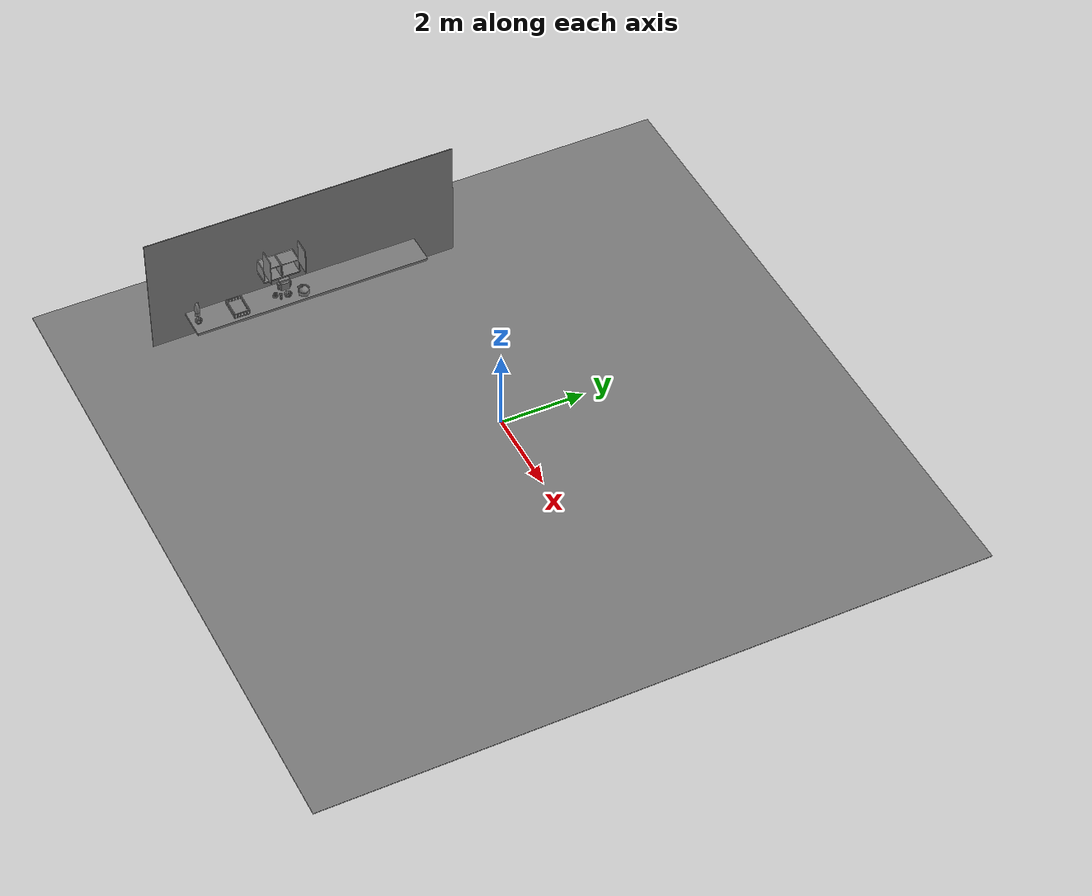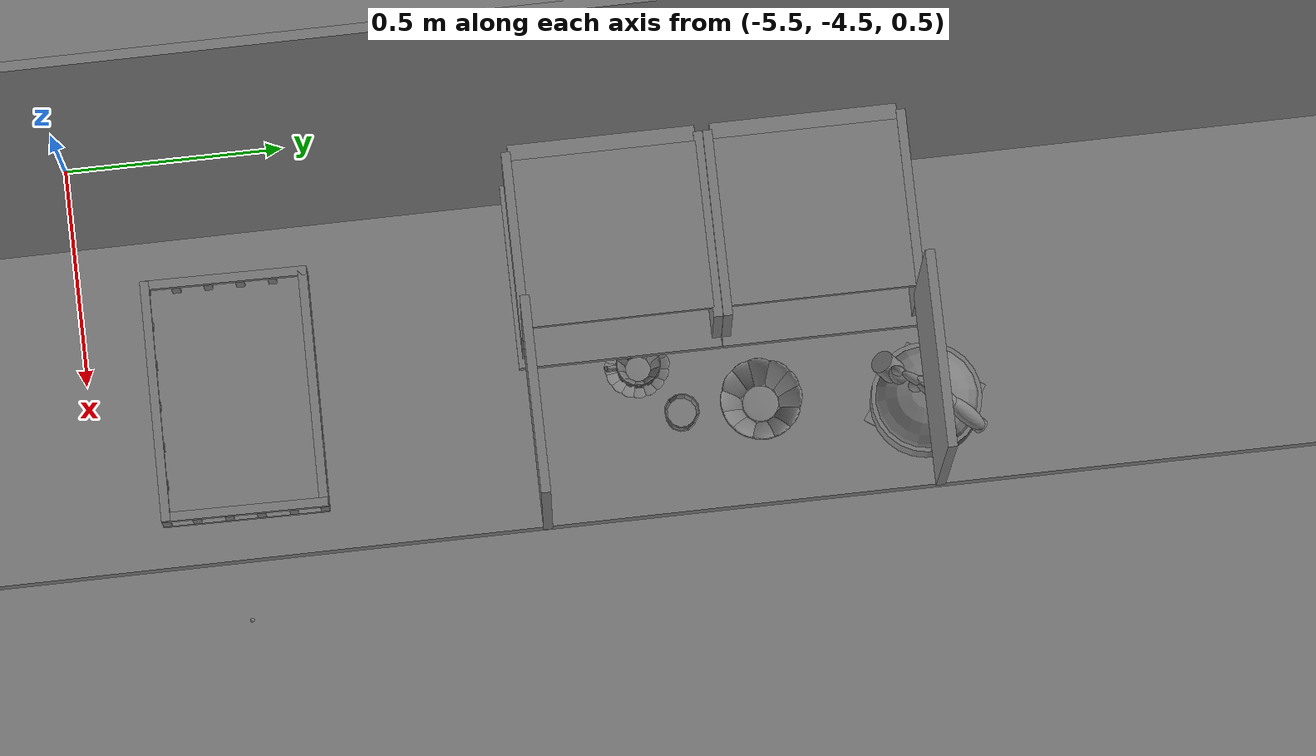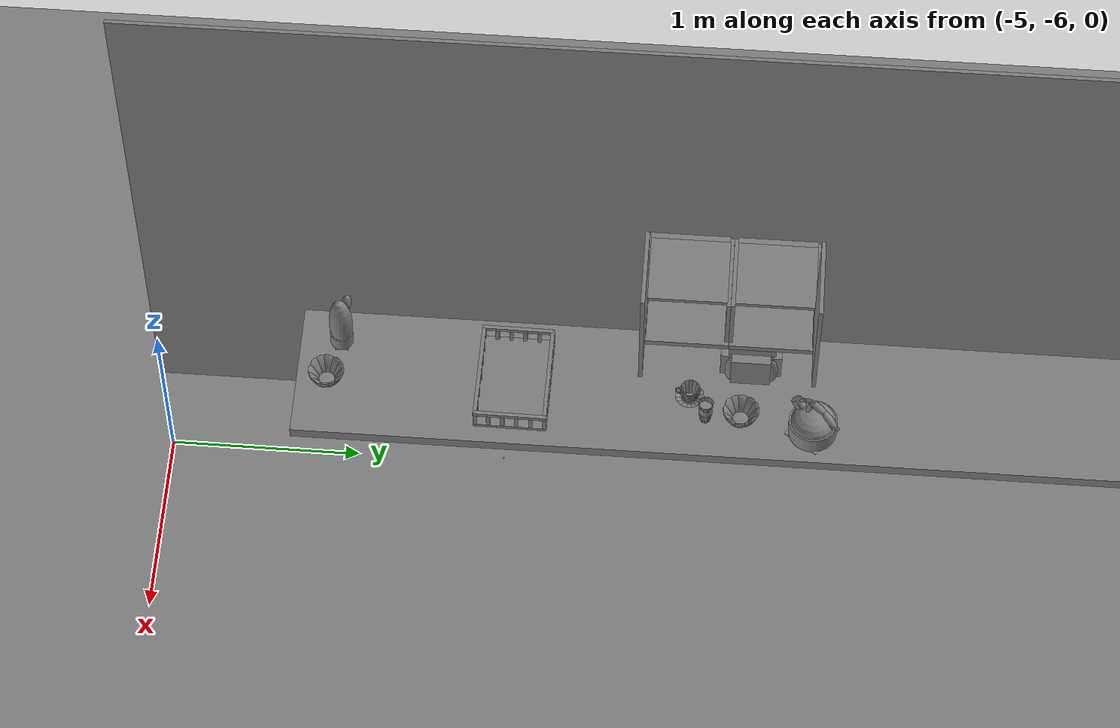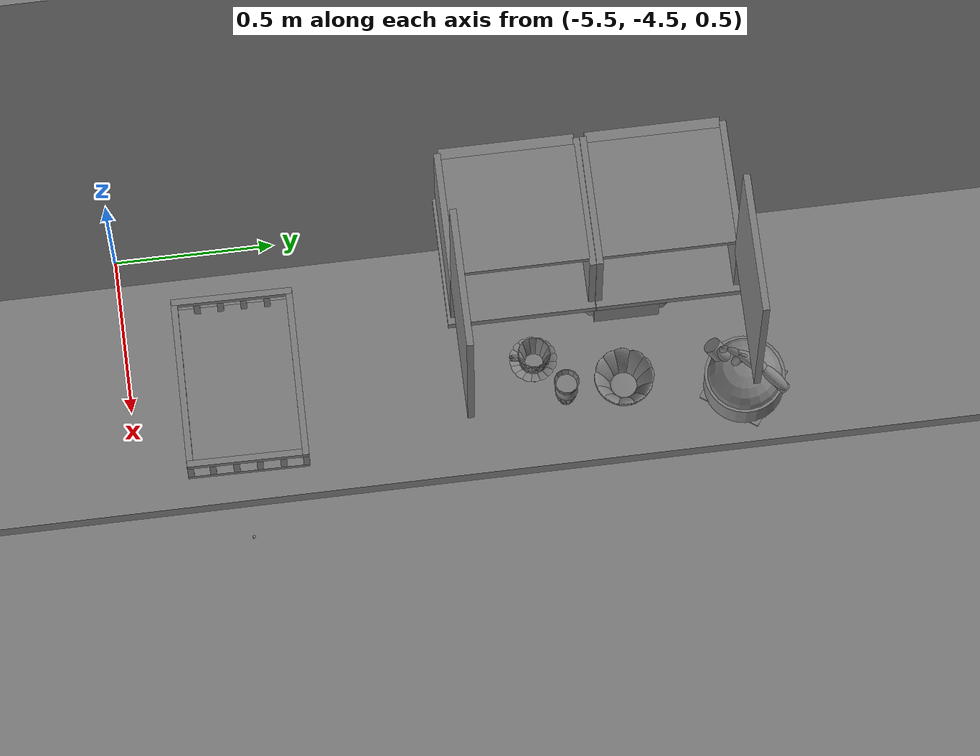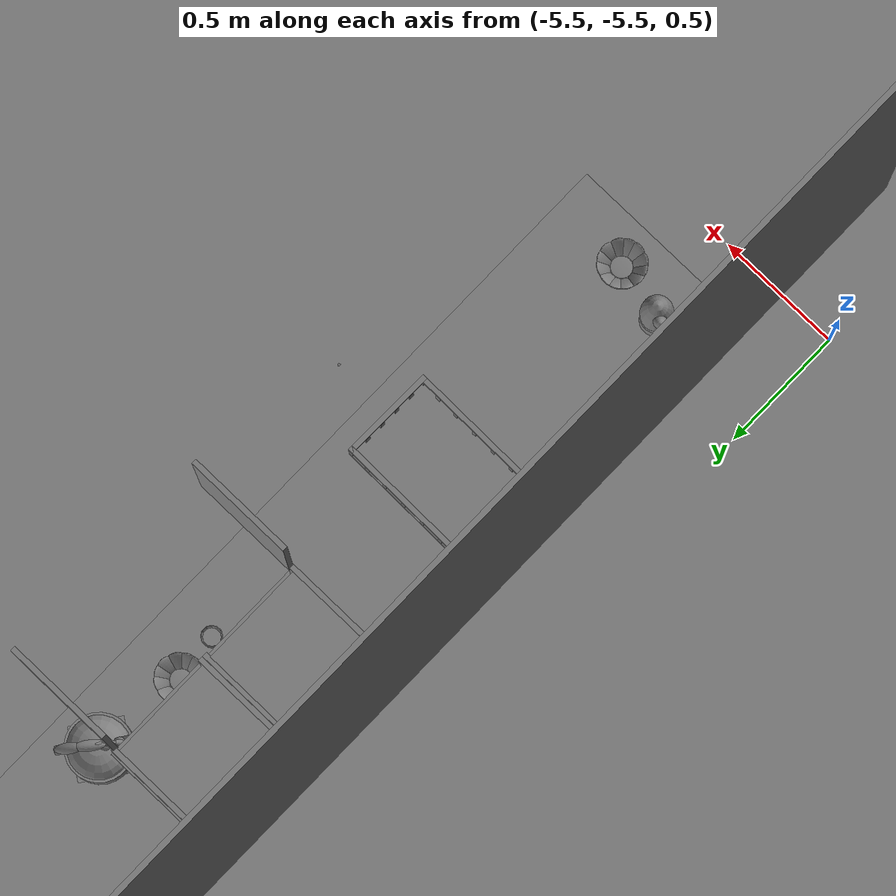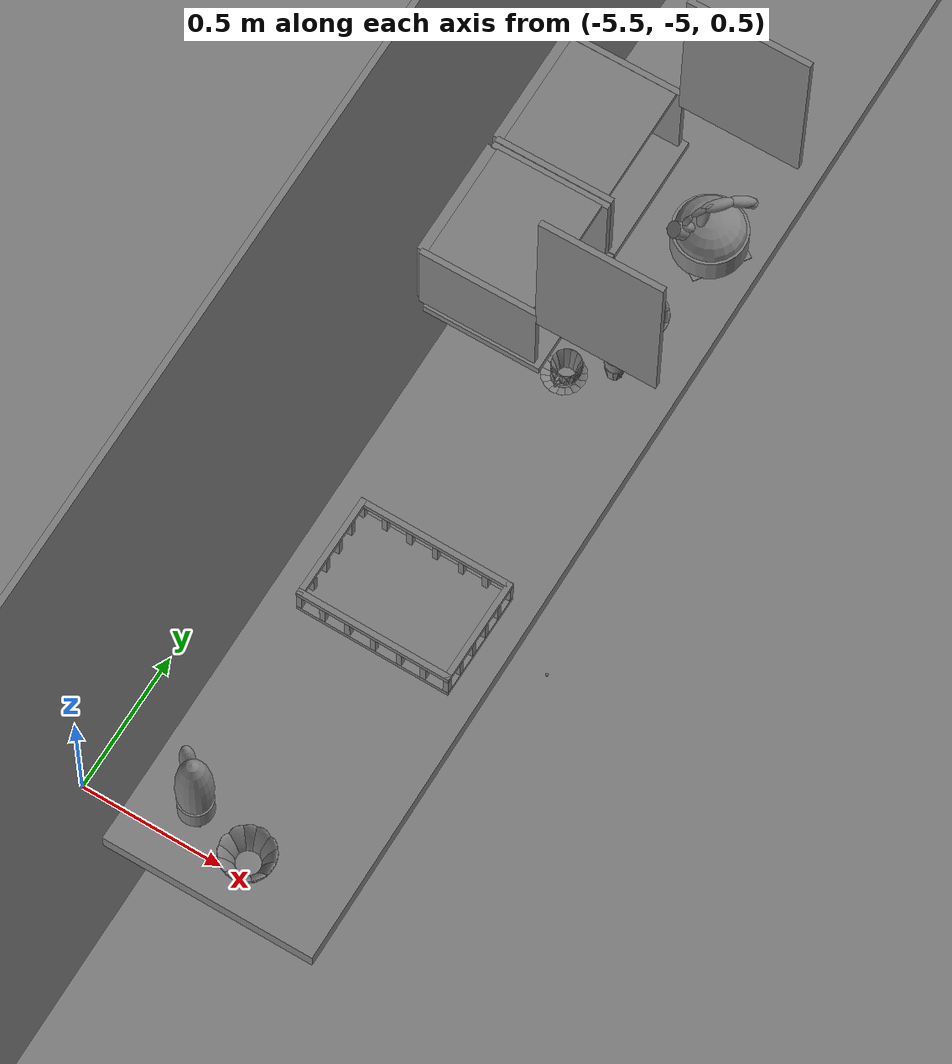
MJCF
<mujoco>
    <option gravity="0.000000000 0.000000000 -9.810000420" timestep="0.0049999999" integrator="implicitfast" density="9.8000002" viscosity="1.8000001e-05" noslip_iterations="10" iterations="100" sdf_iterations="50">
        <flag multiccd="disable"/>
    </option>
    <size memory="1000M"/>
    <compiler coordinate="local"/>
    <worldbody>
        <light cutoff="30" pos="0 1 1" dir="0 -1 -2"/>
        <light cutoff="30" pos="0 -1 1" dir="0 1 -2"/>
        <body pos="-4.860558510 -4.149443150 1.004824519" euler="0.000000000 0.000000000 -90.691108704" name="openloong_gripper_2f85_fix_base_usda_Basket_Kitchen_01">
            <geom contype="1" conaffinity="1" density="1000" type="box" material="" rgba="0.500000000 0.500000000 0.500000000 1.000000000" solimp="0.899999976 0.949999988 0.001000000" friction="1.000000000 0.005000000 0.000100000" solref="0.020000000 1.000000000" margin="0" condim="3" group="0" pos="-0.175679564 -0.000001431 0.109079957" quat="0.707107008 0.000000000 0.000000000 0.707106411" size="0.268999994 0.010000000 0.010500000" name="openloong_gripper_2f85_fix_base_usda_geom_014E0F8D_C4E0_4AFE_9309_6E1060821162"/>
            <geom contype="1" conaffinity="1" density="1000" type="box" material="" rgba="0.500000000 0.500000000 0.500000000 1.000000000" solimp="0.899999976 0.949999988 0.001000000" friction="1.000000000 0.005000000 0.000100000" solref="0.020000000 1.000000000" margin="0" condim="3" group="0" pos="-0.176020086 0.002992153 0.059861541" quat="0.707107008 0.000000000 0.000000000 0.707106411" size="0.009500000 0.009500000 0.039999999" name="openloong_gripper_2f85_fix_base_usda_geom_BB3BC2FB_2F64_480F_848D_96C5B48F2F5E"/>
            <geom contype="1" conaffinity="1" density="1000" type="box" material="" rgba="0.500000000 0.500000000 0.500000000 1.000000000" solimp="0.899999976 0.949999988 0.001000000" friction="1.000000000 0.005000000 0.000100000" solref="0.020000000 1.000000000" margin="0" condim="3" group="0" pos="0.176000595 0.002991199 0.059860706" quat="0.707107008 0.000000000 0.000000000 0.707106411" size="0.009500000 0.009500000 0.039999999" name="openloong_gripper_2f85_fix_base_usda_geom_BE48CE3C_1E06_4EB5_B08F_C8FDFFD34A34"/>
            <geom contype="1" conaffinity="1" density="1000" type="box" material="" rgba="0.500000000 0.500000000 0.500000000 1.000000000" solimp="0.899999976 0.949999988 0.001000000" friction="1.000000000 0.005000000 0.000100000" solref="0.020000000 1.000000000" margin="0" condim="3" group="0" pos="0.176003456 0.259475708 0.059860110" quat="0.707107008 0.000000000 0.000000000 0.707106411" size="0.009500000 0.009500000 0.039999999" name="openloong_gripper_2f85_fix_base_usda_geom_2EFE677C_C9EA_4226_A62B_C949B4E87235"/>
            <geom contype="1" conaffinity="1" density="1000" type="box" material="" rgba="0.500000000 0.500000000 0.500000000 1.000000000" solimp="0.899999976 0.949999988 0.001000000" friction="1.000000000 0.005000000 0.000100000" solref="0.020000000 1.000000000" margin="0" condim="3" group="0" pos="-0.176020026 -0.088695526 0.059861422" quat="0.707107008 0.000000000 0.000000000 0.707106411" size="0.009500000 0.009500000 0.039999999" name="openloong_gripper_2f85_fix_base_usda_geom_3A7B6A20_66A8_4877_B045_544D42CBE7D6"/>
            <geom contype="1" conaffinity="1" density="1000" type="box" material="" rgba="0.500000000 0.500000000 0.500000000 1.000000000" solimp="0.899999976 0.949999988 0.001000000" friction="1.000000000 0.005000000 0.000100000" solref="0.020000000 1.000000000" margin="0" condim="3" group="0" pos="0.000000119 0.259647846 0.109080195" quat="0.707107008 0.000000000 0.000000000 0.707106411" size="0.010000000 0.185000002 0.010500000" name="openloong_gripper_2f85_fix_base_usda_geom_1E08009C_87EE_4D70_9A0A_D834F452B1BA"/>
            <geom contype="1" conaffinity="1" density="1000" type="box" material="" rgba="0.500000000 0.500000000 0.500000000 1.000000000" solimp="0.899999976 0.949999988 0.001000000" friction="1.000000000 0.005000000 0.000100000" solref="0.020000000 1.000000000" margin="0" condim="3" group="0" pos="0.176002026 -0.259545326 0.059860349" quat="0.707107008 0.000000000 0.000000000 0.707106411" size="0.009500000 0.009500000 0.039999999" name="openloong_gripper_2f85_fix_base_usda_geom_72567FA3_B2A9_4ACB_AF6C_44A57C280A0D"/>
            <geom contype="1" conaffinity="1" density="1000" type="box" material="" rgba="0.500000000 0.500000000 0.500000000 1.000000000" solimp="0.899999976 0.949999988 0.001000000" friction="1.000000000 0.005000000 0.000100000" solref="0.020000000 1.000000000" margin="0" condim="3" group="0" pos="0.036305428 -0.259545326 0.059860706" quat="0.707107008 0.000000000 0.000000000 0.707106411" size="0.009500000 0.009500000 0.039999999" name="openloong_gripper_2f85_fix_base_usda_geom_33A5CCBE_16C9_411B_8B77_D556CEF083BE"/>
            <geom contype="1" conaffinity="1" density="1000" type="box" material="" rgba="0.500000000 0.500000000 0.500000000 1.000000000" solimp="0.899999976 0.949999988 0.001000000" friction="1.000000000 0.005000000 0.000100000" solref="0.020000000 1.000000000" margin="0" condim="3" group="0" pos="0.000000000 -0.259647369 0.109080195" quat="0.707107008 0.000000000 0.000000000 0.707106411" size="0.010000000 0.185000002 0.010500000" name="openloong_gripper_2f85_fix_base_usda_geom_7F1594CC_34C4_4C41_A6DF_95CCF9887B9A"/>
            <geom contype="1" conaffinity="1" density="1000" type="box" material="" rgba="0.500000000 0.500000000 0.500000000 1.000000000" solimp="0.899999976 0.949999988 0.001000000" friction="1.000000000 0.005000000 0.000100000" solref="0.020000000 1.000000000" margin="0" condim="3" group="0" pos="-0.034950733 -0.259545803 0.059860826" quat="0.707107008 0.000000000 0.000000000 0.707106411" size="0.009500000 0.009500000 0.039999999" name="openloong_gripper_2f85_fix_base_usda_geom_B65BBA9B_E451_4E61_AB2A_6D396DB55096"/>
            <geom contype="1" conaffinity="1" density="1000" type="box" material="" rgba="0.500000000 0.500000000 0.500000000 1.000000000" solimp="0.899999976 0.949999988 0.001000000" friction="1.000000000 0.005000000 0.000100000" solref="0.020000000 1.000000000" margin="0" condim="3" group="0" pos="0.108178139 0.259475946 0.059860229" quat="0.707107008 0.000000000 0.000000000 0.707106411" size="0.009500000 0.009500000 0.039999999" name="openloong_gripper_2f85_fix_base_usda_geom_B955E37A_35EA_40A9_A4A8_D3F2989C22CC"/>
            <geom contype="1" conaffinity="1" density="1000" type="box" material="" rgba="0.500000000 0.500000000 0.500000000 1.000000000" solimp="0.899999976 0.949999988 0.001000000" friction="1.000000000 0.005000000 0.000100000" solref="0.020000000 1.000000000" margin="0" condim="3" group="0" pos="-0.106845737 0.259475231 0.059860826" quat="0.707107008 0.000000000 0.000000000 0.707106411" size="0.009500000 0.009500000 0.039999999" name="openloong_gripper_2f85_fix_base_usda_geom_A65A3166_4F95_4FDB_B394_04592D40315F"/>
            <geom contype="1" conaffinity="1" density="1000" type="box" material="" rgba="0.500000000 0.500000000 0.500000000 1.000000000" solimp="0.899999976 0.949999988 0.001000000" friction="1.000000000 0.005000000 0.000100000" solref="0.020000000 1.000000000" margin="0" condim="3" group="0" pos="-0.176020563 0.179506302 0.059861779" quat="0.707107008 0.000000000 0.000000000 0.707106411" size="0.009500000 0.009500000 0.039999999" name="openloong_gripper_2f85_fix_base_usda_geom_3C6D64CE_5AD9_4723_A4CF_3AE3652442B2"/>
            <geom contype="1" conaffinity="1" density="1000" type="box" material="" rgba="0.500000000 0.500000000 0.500000000 1.000000000" solimp="0.899999976 0.949999988 0.001000000" friction="1.000000000 0.005000000 0.000100000" solref="0.020000000 1.000000000" margin="0" condim="3" group="0" pos="-0.034949183 0.259475946 0.059860587" quat="0.707107008 0.000000000 0.000000000 0.707106411" size="0.009500000 0.009500000 0.039999999" name="openloong_gripper_2f85_fix_base_usda_geom_91AD9E79_C540_4D6A_B69C_426AD657C64F"/>
            <geom contype="1" conaffinity="1" density="1000" type="box" material="" rgba="0.500000000 0.500000000 0.500000000 1.000000000" solimp="0.899999976 0.949999988 0.001000000" friction="1.000000000 0.005000000 0.000100000" solref="0.020000000 1.000000000" margin="0" condim="3" group="0" pos="0.175792217 -0.000001907 0.109079838" quat="0.707107008 0.000000000 0.000000000 0.707106411" size="0.268999994 0.010000000 0.010500000" name="openloong_gripper_2f85_fix_base_usda_geom_B63D68A4_0B0A_4602_A437_C0E9EC3028A9"/>
            <geom contype="1" conaffinity="1" density="1000" type="box" material="" rgba="0.500000000 0.500000000 0.500000000 1.000000000" solimp="0.899999976 0.949999988 0.001000000" friction="1.000000000 0.005000000 0.000100000" solref="0.020000000 1.000000000" margin="0" condim="3" group="0" pos="-0.000015259 0.000000000 0.010668159" quat="0.707107008 0.000000000 0.000000000 0.707106411" size="0.268999994 0.186000004 0.010500000" name="openloong_gripper_2f85_fix_base_usda_geom_5379CB7B_BB25_4396_BD87_25F59F60A4BA"/>
            <geom contype="1" conaffinity="1" density="1000" type="box" material="" rgba="0.500000000 0.500000000 0.500000000 1.000000000" solimp="0.899999976 0.949999988 0.001000000" friction="1.000000000 0.005000000 0.000100000" solref="0.020000000 1.000000000" margin="0" condim="3" group="0" pos="-0.176020086 0.094225407 0.059861660" quat="0.707107008 0.000000000 0.000000000 0.707106411" size="0.009500000 0.009500000 0.039999999" name="openloong_gripper_2f85_fix_base_usda_geom_CED26A92_9CE5_4665_875A_B27F838C911F"/>
            <geom contype="1" conaffinity="1" density="1000" type="box" material="" rgba="0.500000000 0.500000000 0.500000000 1.000000000" solimp="0.899999976 0.949999988 0.001000000" friction="1.000000000 0.005000000 0.000100000" solref="0.020000000 1.000000000" margin="0" condim="3" group="0" pos="0.108177185 -0.259544849 0.059860468" quat="0.707107008 0.000000000 0.000000000 0.707106411" size="0.009500000 0.009500000 0.039999999" name="openloong_gripper_2f85_fix_base_usda_geom_5CB9DCA1_1BB8_4DD2_A2D6_D13B6A6080F1"/>
            <geom contype="1" conaffinity="1" density="1000" type="box" material="" rgba="0.500000000 0.500000000 0.500000000 1.000000000" solimp="0.899999976 0.949999988 0.001000000" friction="1.000000000 0.005000000 0.000100000" solref="0.020000000 1.000000000" margin="0" condim="3" group="0" pos="-0.176019967 -0.177031994 0.059861302" quat="0.707107008 0.000000000 0.000000000 0.707106411" size="0.009500000 0.009500000 0.039999999" name="openloong_gripper_2f85_fix_base_usda_geom_CCDE4F0F_9414_4365_997F_AF7EEEC3352E"/>
            <geom contype="1" conaffinity="1" density="1000" type="box" material="" rgba="0.500000000 0.500000000 0.500000000 1.000000000" solimp="0.899999976 0.949999988 0.001000000" friction="1.000000000 0.005000000 0.000100000" solref="0.020000000 1.000000000" margin="0" condim="3" group="0" pos="-0.176020026 -0.259545326 0.059861183" quat="0.707107008 0.000000000 0.000000000 0.707106411" size="0.009500000 0.009500000 0.039999999" name="openloong_gripper_2f85_fix_base_usda_geom_25D62AA8_C9FE_442C_AF6D_2462CE0CF6B3"/>
            <geom contype="1" conaffinity="1" density="1000" type="box" material="" rgba="0.500000000 0.500000000 0.500000000 1.000000000" solimp="0.899999976 0.949999988 0.001000000" friction="1.000000000 0.005000000 0.000100000" solref="0.020000000 1.000000000" margin="0" condim="3" group="0" pos="-0.106846333 -0.259546280 0.059861064" quat="0.707107008 0.000000000 0.000000000 0.707106411" size="0.009500000 0.009500000 0.039999999" name="openloong_gripper_2f85_fix_base_usda_geom_8C62256D_BD89_4FFF_829A_708FA98C79A0"/>
            <geom contype="1" conaffinity="1" density="1000" type="box" material="" rgba="0.500000000 0.500000000 0.500000000 1.000000000" solimp="0.899999976 0.949999988 0.001000000" friction="1.000000000 0.005000000 0.000100000" solref="0.020000000 1.000000000" margin="0" condim="3" group="0" pos="0.176000595 0.094224453 0.059860826" quat="0.707107008 0.000000000 0.000000000 0.707106411" size="0.009500000 0.009500000 0.039999999" name="openloong_gripper_2f85_fix_base_usda_geom_3E836FDB_F851_4A3E_AF1B_30FD21EF8A39"/>
            <geom contype="1" conaffinity="1" density="1000" type="box" material="" rgba="0.500000000 0.500000000 0.500000000 1.000000000" solimp="0.899999976 0.949999988 0.001000000" friction="1.000000000 0.005000000 0.000100000" solref="0.020000000 1.000000000" margin="0" condim="3" group="0" pos="0.176001072 -0.088696480 0.059860587" quat="0.707107008 0.000000000 0.000000000 0.707106411" size="0.009500000 0.009500000 0.039999999" name="openloong_gripper_2f85_fix_base_usda_geom_5A479862_BBAF_4BBC_936E_6ED3DE9817D4"/>
            <geom contype="1" conaffinity="1" density="1000" type="box" material="" rgba="0.500000000 0.500000000 0.500000000 1.000000000" solimp="0.899999976 0.949999988 0.001000000" friction="1.000000000 0.005000000 0.000100000" solref="0.020000000 1.000000000" margin="0" condim="3" group="0" pos="0.036307096 0.259476185 0.059860468" quat="0.707107008 0.000000000 0.000000000 0.707106411" size="0.009500000 0.009500000 0.039999999" name="openloong_gripper_2f85_fix_base_usda_geom_EA82A55B_CCAD_453D_9E69_56C952DF4458"/>
            <geom contype="1" conaffinity="1" density="1000" type="box" material="" rgba="0.500000000 0.500000000 0.500000000 1.000000000" solimp="0.899999976 0.949999988 0.001000000" friction="1.000000000 0.005000000 0.000100000" solref="0.020000000 1.000000000" margin="0" condim="3" group="0" pos="0.176001549 -0.177031994 0.059860468" quat="0.707107008 0.000000000 0.000000000 0.707106411" size="0.009500000 0.009500000 0.039999999" name="openloong_gripper_2f85_fix_base_usda_geom_13AFAD0D_056F_446E_ADB9_DC59E4A926AB"/>
            <geom contype="1" conaffinity="1" density="1000" type="box" material="" rgba="0.500000000 0.500000000 0.500000000 1.000000000" solimp="0.899999976 0.949999988 0.001000000" friction="1.000000000 0.005000000 0.000100000" solref="0.020000000 1.000000000" margin="0" condim="3" group="0" pos="0.176000118 0.179505348 0.059860945" quat="0.707107008 0.000000000 0.000000000 0.707106411" size="0.009500000 0.009500000 0.039999999" name="openloong_gripper_2f85_fix_base_usda_geom_6949BCA9_9AC0_42DF_82D8_7B08C382AE8A"/>
            <geom contype="1" conaffinity="1" density="1000" type="box" material="" rgba="0.500000000 0.500000000 0.500000000 1.000000000" solimp="0.899999976 0.949999988 0.001000000" friction="1.000000000 0.005000000 0.000100000" solref="0.020000000 1.000000000" margin="0" condim="3" group="0" pos="-0.176020086 0.259474993 0.059860945" quat="0.707107008 0.000000000 0.000000000 0.707106411" size="0.009500000 0.009500000 0.039999999" name="openloong_gripper_2f85_fix_base_usda_geom_8A03FCD1_CCAE_4063_9557_9C47A4641B26"/>
            <freejoint name="openloong_gripper_2f85_fix_base_usda_Basket_Kitchen_01_joint"/>
        </body>
        <body pos="-4.802892208 -3.488179445 1.876015186" euler="89.999992371 -89.999946594 0.000000000" name="Interactive Objcets_guimen_01">
            <geom contype="1" conaffinity="1" density="1000" type="box" material="" rgba="0.500000000 0.500000000 0.500000000 1.000000000" solimp="0.899999976 0.949999988 0.001000000" friction="1.000000000 0.005000000 0.000100000" solref="0.020000000 1.000000000" margin="0" condim="3" group="0" pos="0.006727934 0.314709902 -0.203009605" quat="1.000000000 0.000000119 -0.000000119 0.000000000" size="0.010000000 0.317999989 0.204999998" name="Interactive Objcets_geom_E2BBE068_5110_4246_A004_4896512AF001"/>
            <joint armature="0" stiffness="0" damping="1" axis="0.000000 1.000000 0.000000" type="hinge" name="Interactive Objcets_guimen_01"/>
        </body>
        <body pos="-4.805274963 -2.665403366 1.876015186" euler="89.999877930 89.999969482 0.000000000" name="Interactive Objcets_guimen_02">
            <geom contype="1" conaffinity="1" density="1000" type="box" material="" rgba="0.500000000 0.500000000 0.500000000 1.000000000" solimp="0.899999976 0.949999988 0.001000000" friction="1.000000000 0.005000000 0.000100000" solref="0.020000000 1.000000000" margin="0" condim="3" group="0" pos="0.006727815 0.314709663 0.203009367" quat="0.999999940 0.000000000 0.000000000 0.000000000" size="0.010000000 0.317999989 0.204999998" name="Interactive Objcets_geom_12BA771A_05D5_4064_984D_00EC2FF85A9E"/>
            <joint armature="0" stiffness="0" damping="1" axis="0.000000 1.000000 0.000000" type="hinge" name="Interactive Objcets_guimen_02"/>
        </body>
        <body pos="-4.827295780 -3.287638187 1.074643731" euler="0.000000000 0.000000000 89.999992371" name="Interactive Objcets_coffeecup_01">
            <geom contype="1" conaffinity="1" density="1000" type="ellipsoid" material="" rgba="0.500000000 0.500000000 0.500000000 1.000000000" solimp="0.899999976 0.949999988 0.001000000" friction="1.000000000 0.005000000 0.000100000" solref="0.020000000 1.000000000" margin="0" condim="3" group="0" pos="0.035336256 0.000558376 -0.043215394" quat="0.999999881 0.000000000 0.000000000 0.000000000" size="0.029999999 0.029999999 0.001000000" name="Interactive Objcets_geom_C8A07F56_02FC_414E_8B11_23BC02458528"/>
            <geom contype="1" conaffinity="1" density="1000" type="ellipsoid" material="" rgba="0.500000000 0.500000000 0.500000000 1.000000000" solimp="0.899999976 0.949999988 0.001000000" friction="1.000000000 0.005000000 0.000100000" solref="0.020000000 1.000000000" margin="0" condim="3" group="0" pos="0.067416430 -0.018191338 0.002976775" quat="0.961934388 0.024418317 0.091648072 -0.256293803" size="0.005000000 0.029999999 0.048999999" name="Interactive Objcets_geom_CE71E10F_08D7_4BB0_8307_29B9DD45C083"/>
            <geom contype="1" conaffinity="1" density="1000" type="ellipsoid" material="" rgba="0.500000000 0.500000000 0.500000000 1.000000000" solimp="0.899999976 0.949999988 0.001000000" friction="1.000000000 0.005000000 0.000100000" solref="0.020000000 1.000000000" margin="0" condim="3" group="0" pos="0.034471050 -0.037125111 0.002976775" quat="0.701517045 0.067293778 0.066836871 -0.706313014" size="0.005000000 0.029999999 0.048999999" name="Interactive Objcets_geom_18E734DF_60B5_489E_9428_CBB4A769AD99"/>
            <geom contype="1" conaffinity="1" density="1000" type="ellipsoid" material="" rgba="0.500000000 0.500000000 0.500000000 1.000000000" solimp="0.899999976 0.949999988 0.001000000" friction="1.000000000 0.005000000 0.000100000" solref="0.020000000 1.000000000" margin="0" condim="3" group="0" pos="0.035336256 0.000558376 -0.045152068" quat="0.999999881 0.000000000 0.000000000 0.000000000" size="0.029999999 0.029999999 0.001000000" name="Interactive Objcets_geom_EAAC1CF9_5678_46EF_8EAE_8503F04DDCEF"/>
            <geom contype="1" conaffinity="1" density="1000" type="ellipsoid" material="" rgba="0.500000000 0.500000000 0.500000000 1.000000000" solimp="0.899999976 0.949999988 0.001000000" friction="1.000000000 0.005000000 0.000100000" solref="0.020000000 1.000000000" margin="0" condim="3" group="0" pos="0.001010895 -0.016271591 0.002976775" quat="0.228377163 0.092315644 0.021758538 -0.968941689" size="0.005000000 0.029999999 0.048999999" name="Interactive Objcets_geom_2AF7F524_89A1_449B_821D_288878A65CDA"/>
            <geom contype="1" conaffinity="1" density="1000" type="capsule" material="" rgba="0.500000000 0.500000000 0.500000000 1.000000000" solimp="0.899999976 0.949999988 0.001000000" friction="1.000000000 0.005000000 0.000100000" solref="0.020000000 1.000000000" margin="0" condim="3" group="0" pos="-0.021276474 0.000000000 0.038509369" quat="0.633189917 0.000000000 0.773996413 0.000000000" size="0.004000000 0.009000000 1.000000000" name="Interactive Objcets_geom_9B32C67E_C41B_4679_A9FB_6EF77627255C"/>
            <geom contype="1" conaffinity="1" density="1000" type="capsule" material="" rgba="0.500000000 0.500000000 0.500000000 1.000000000" solimp="0.899999976 0.949999988 0.001000000" friction="1.000000000 0.005000000 0.000100000" solref="0.020000000 1.000000000" margin="0" condim="3" group="0" pos="-0.018014431 0.000000000 0.001762271" quat="0.707106769 -0.000000004 0.707106709 -0.000000088" size="0.004000000 0.005000000 1.000000000" name="Interactive Objcets_geom_19D25404_4038_46F4_9896_AE203D3C4EEA"/>
            <geom contype="1" conaffinity="1" density="1000" type="ellipsoid" material="" rgba="0.500000000 0.500000000 0.500000000 1.000000000" solimp="0.899999976 0.949999988 0.001000000" friction="1.000000000 0.005000000 0.000100000" solref="0.020000000 1.000000000" margin="0" condim="3" group="0" pos="0.068445444 0.017385960 0.002976775" quat="0.228377223 -0.092319682 -0.021759447 -0.968941331" size="0.005000000 0.029999999 0.048999999" name="Interactive Objcets_geom_A28E36F9_0110_455A_A7E7_CB0F13655F62"/>
            <geom contype="1" conaffinity="1" density="1000" type="ellipsoid" material="" rgba="0.500000000 0.500000000 0.500000000 1.000000000" solimp="0.899999976 0.949999988 0.001000000" friction="1.000000000 0.005000000 0.000100000" solref="0.020000000 1.000000000" margin="0" condim="3" group="0" pos="0.002039194 0.019308567 0.002976775" quat="0.961933970 -0.024419386 -0.091652036 -0.256293654" size="0.005000000 0.029999999 0.048999999" name="Interactive Objcets_geom_689E4128_5653_467C_A458_E4424F8D0D4D"/>
            <geom contype="1" conaffinity="1" density="1000" type="ellipsoid" material="" rgba="0.500000000 0.500000000 0.500000000 1.000000000" solimp="0.899999976 0.949999988 0.001000000" friction="1.000000000 0.005000000 0.000100000" solref="0.020000000 1.000000000" margin="0" condim="3" group="0" pos="0.034984604 0.038240910 0.002976775" quat="0.701516926 -0.067296736 -0.066839755 -0.706312656" size="0.005000000 0.029999999 0.048999999" name="Interactive Objcets_geom_99874DC7_EBE8_4B29_9BED_FF612BF113BD"/>
            <geom contype="1" conaffinity="1" density="1000" type="ellipsoid" material="" rgba="0.500000000 0.500000000 0.500000000 1.000000000" solimp="0.899999976 0.949999988 0.001000000" friction="1.000000000 0.005000000 0.000100000" solref="0.020000000 1.000000000" margin="0" condim="3" group="0" pos="0.017669693 0.034160614 0.002976775" quat="0.848410904 -0.049618516 -0.080835648 -0.520770907" size="0.005000000 0.029999999 0.048999999" name="Interactive Objcets_geom_60E1ECE2_2BFA_43AA_842E_F407BF84A81B"/>
            <geom contype="1" conaffinity="1" density="1000" type="ellipsoid" material="" rgba="0.500000000 0.500000000 0.500000000 1.000000000" solimp="0.899999976 0.949999988 0.001000000" friction="1.000000000 0.005000000 0.000100000" solref="0.020000000 1.000000000" margin="0" condim="3" group="0" pos="-0.002956629 0.000558376 0.002976775" quat="0.995491505 0.000000004 -0.094849378 -0.000000089" size="0.005000000 0.029999999 0.048999999" name="Interactive Objcets_geom_3FA5C86B_3E74_44BC_BA17_A20F4474E7BF"/>
            <geom contype="1" conaffinity="1" density="1000" type="ellipsoid" material="" rgba="0.500000000 0.500000000 0.500000000 1.000000000" solimp="0.899999976 0.949999988 0.001000000" friction="1.000000000 0.005000000 0.000100000" solref="0.020000000 1.000000000" margin="0" condim="3" group="0" pos="0.051787138 -0.033043861 0.002976775" quat="0.848411202 0.049616337 0.080832161 -0.520771146" size="0.005000000 0.029999999 0.048999999" name="Interactive Objcets_geom_EC4605EF_A64C_4625_97F9_8E2D698AE499"/>
            <geom contype="1" conaffinity="1" density="1000" type="capsule" material="" rgba="0.500000000 0.500000000 0.500000000 1.000000000" solimp="0.899999976 0.949999988 0.001000000" friction="1.000000000 0.005000000 0.000100000" solref="0.020000000 1.000000000" margin="0" condim="3" group="0" pos="-0.030251026 0.000000000 0.004966617" quat="0.480583906 -0.000000000 0.876948774 -0.000000126" size="0.004000000 0.005000000 1.000000000" name="Interactive Objcets_geom_DD1F7577_7807_4A30_9FB0_E3930851E1C2"/>
            <geom contype="1" conaffinity="1" density="1000" type="capsule" material="" rgba="0.500000000 0.500000000 0.500000000 1.000000000" solimp="0.899999976 0.949999988 0.001000000" friction="1.000000000 0.005000000 0.000100000" solref="0.020000000 1.000000000" margin="0" condim="3" group="0" pos="-0.036300898 0.000000000 0.021037936" quat="0.044551343 -0.000000000 0.999007046 -0.000000126" size="0.004000000 0.012000000 1.000000000" name="Interactive Objcets_geom_A47C26DA_32B5_4572_9A32_17A0CAE336FB"/>
            <geom contype="1" conaffinity="1" density="1000" type="capsule" material="" rgba="0.500000000 0.500000000 0.500000000 1.000000000" solimp="0.899999976 0.949999988 0.001000000" friction="1.000000000 0.005000000 0.000100000" solref="0.020000000 1.000000000" margin="0" condim="3" group="0" pos="-0.008219719 0.000000000 -0.000944734" quat="0.364379913 0.000000063 0.931250274 -0.000000063" size="0.004000000 0.003000000 1.000000000" name="Interactive Objcets_geom_A18019BD_0D87_451C_B996_1C7360D28D2B"/>
            <geom contype="1" conaffinity="1" density="1000" type="capsule" material="" rgba="0.500000000 0.500000000 0.500000000 1.000000000" solimp="0.899999976 0.949999988 0.001000000" friction="1.000000000 0.005000000 0.000100000" solref="0.020000000 1.000000000" margin="0" condim="3" group="0" pos="-0.033022881 0.000000000 0.037873149" quat="0.874267220 0.000000042 0.485444903 -0.000000084" size="0.004000000 0.004000000 1.000000000" name="Interactive Objcets_geom_B1F3B5A1_BBC6_4381_97ED_4EEE6993101A"/>
            <geom contype="1" conaffinity="1" density="1000" type="ellipsoid" material="" rgba="0.500000000 0.500000000 0.500000000 1.000000000" solimp="0.899999976 0.949999988 0.001000000" friction="1.000000000 0.005000000 0.000100000" solref="0.020000000 1.000000000" margin="0" condim="3" group="0" pos="0.015755907 -0.032001972 0.002976775" quat="0.496025920 0.082232773 0.047258731 -0.863112032" size="0.005000000 0.029999999 0.048999999" name="Interactive Objcets_geom_43C52364_CD75_48FF_8CE6_0ACA4B122500"/>
            <geom contype="1" conaffinity="1" density="1000" type="ellipsoid" material="" rgba="0.500000000 0.500000000 0.500000000 1.000000000" solimp="0.899999976 0.949999988 0.001000000" friction="1.000000000 0.005000000 0.000100000" solref="0.020000000 1.000000000" margin="0" condim="3" group="0" pos="0.072411790 0.000558376 0.002976775" quat="0.995491922 -0.000000019 0.094845265 -0.000000089" size="0.005000000 0.029999999 0.048999999" name="Interactive Objcets_geom_B6A1DA4C_681D_4595_BBE5_776359CA0340"/>
            <geom contype="1" conaffinity="1" density="1000" type="ellipsoid" material="" rgba="0.500000000 0.500000000 0.500000000 1.000000000" solimp="0.899999976 0.949999988 0.001000000" friction="1.000000000 0.005000000 0.000100000" solref="0.020000000 1.000000000" margin="0" condim="3" group="0" pos="0.053700209 0.033117294 0.002976775" quat="0.496025741 -0.082236379 -0.047260769 -0.863111615" size="0.005000000 0.029999999 0.048999999" name="Interactive Objcets_geom_6D0D64DB_8D7A_437D_B1A2_59D367640E88"/>
            <freejoint name="Interactive Objcets_coffeecup_01"/>
        </body>
        <body pos="-5.020127296 -2.953741550 1.135127425" euler="89.999946594 0.000000000 0.000000000" name="Interactive Objcets_Bread">
            <geom contype="1" conaffinity="1" density="1000" type="box" material="" rgba="0.500000000 0.500000000 0.500000000 1.000000000" solimp="0.899999976 0.949999988 0.001000000" friction="1.000000000 0.005000000 0.000100000" solref="0.020000000 1.000000000" margin="0" condim="3" group="0" pos="-0.008702755 -0.017670274 -0.135069147" quat="0.707107067 -0.707106471 0.000000021 -0.000000021" size="0.045000002 0.020000000 0.079999998" name="Interactive Objcets_geom_D1FACA23_B473_42AF_A709_BEA7E295E93B"/>
            <geom contype="1" conaffinity="1" density="1000" type="box" material="" rgba="0.500000000 0.500000000 0.500000000 1.000000000" solimp="0.899999976 0.949999988 0.001000000" friction="1.000000000 0.005000000 0.000100000" solref="0.020000000 1.000000000" margin="0" condim="3" group="0" pos="0.033925056 -0.123201847 0.086778767" quat="0.707107067 -0.707106471 0.000000021 -0.000000021" size="0.020000000 0.020000000 0.005000000" name="Interactive Objcets_geom_6CB3DDCC_5FAB_474F_B4C5_A9B97E2AAD96"/>
            <geom contype="1" conaffinity="1" density="1000" type="box" material="" rgba="0.500000000 0.500000000 0.500000000 1.000000000" solimp="0.899999976 0.949999988 0.001000000" friction="1.000000000 0.005000000 0.000100000" solref="0.020000000 1.000000000" margin="0" condim="3" group="0" pos="-0.008702755 -0.016588926 0.000174277" quat="0.707107067 -0.707106471 0.000000021 -0.000000021" size="0.090000004 0.100000001 0.094999999" name="Interactive Objcets_geom_D4009FB9_2177_4FA6_AD99_C89021484292"/>
            <geom contype="1" conaffinity="1" density="1000" type="ellipsoid" material="" rgba="0.500000000 0.500000000 0.500000000 1.000000000" solimp="0.899999976 0.949999988 0.001000000" friction="1.000000000 0.005000000 0.000100000" solref="0.020000000 1.000000000" margin="0" condim="3" group="0" pos="-0.067312241 -0.026057482 -0.101716787" quat="0.707107067 -0.707106471 0.000000021 -0.000000021" size="0.020000000 0.029999999 0.094999999" name="Interactive Objcets_geom_EC5B528B_9035_4FD4_80E8_729F4F258C99"/>
            <geom contype="1" conaffinity="1" density="1000" type="ellipsoid" material="" rgba="0.500000000 0.500000000 0.500000000 1.000000000" solimp="0.899999976 0.949999988 0.001000000" friction="1.000000000 0.005000000 0.000100000" solref="0.020000000 1.000000000" margin="0" condim="3" group="0" pos="0.052222252 -0.026057363 0.101459242" quat="0.707107067 -0.707106471 0.000000021 -0.000000021" size="0.020000000 0.029999999 0.094999999" name="Interactive Objcets_geom_99C02F50_C7E4_426F_8E45_502D91F603B8"/>
            <geom contype="1" conaffinity="1" density="1000" type="box" material="" rgba="0.500000000 0.500000000 0.500000000 1.000000000" solimp="0.899999976 0.949999988 0.001000000" friction="1.000000000 0.005000000 0.000100000" solref="0.020000000 1.000000000" margin="0" condim="3" group="0" pos="-0.050020695 -0.123201847 0.086778767" quat="0.707107067 -0.707106471 0.000000021 -0.000000021" size="0.020000000 0.020000000 0.005000000" name="Interactive Objcets_geom_EED4DBDB_326D_4BBB_BB61_A8FF522AF4F1"/>
            <geom contype="1" conaffinity="1" density="1000" type="box" material="" rgba="0.500000000 0.500000000 0.500000000 1.000000000" solimp="0.899999976 0.949999988 0.001000000" friction="1.000000000 0.005000000 0.000100000" solref="0.020000000 1.000000000" margin="0" condim="3" group="0" pos="0.033925056 -0.123201728 -0.092369899" quat="0.707107067 -0.707106471 0.000000021 -0.000000021" size="0.020000000 0.020000000 0.005000000" name="Interactive Objcets_geom_8885AAB0_8BF7_41E4_BF5A_A672932A6F3A"/>
            <geom contype="1" conaffinity="1" density="1000" type="ellipsoid" material="" rgba="0.500000000 0.500000000 0.500000000 1.000000000" solimp="0.899999976 0.949999988 0.001000000" friction="1.000000000 0.005000000 0.000100000" solref="0.020000000 1.000000000" margin="0" condim="3" group="0" pos="-0.069190502 -0.026057363 0.101458766" quat="0.707107067 -0.707106471 0.000000021 -0.000000021" size="0.020000000 0.029999999 0.094999999" name="Interactive Objcets_geom_1EBBA8C3_5D22_47F9_852C_73A8AB5A8B90"/>
            <geom contype="1" conaffinity="1" density="1000" type="box" material="" rgba="0.500000000 0.500000000 0.500000000 1.000000000" solimp="0.899999976 0.949999988 0.001000000" friction="1.000000000 0.005000000 0.000100000" solref="0.020000000 1.000000000" margin="0" condim="3" group="0" pos="-0.008702755 -0.017670155 0.134585604" quat="0.707107067 -0.707106471 0.000000021 -0.000000021" size="0.045000002 0.020000000 0.079999998" name="Interactive Objcets_geom_6A389EF5_5757_48A8_9C1B_04AD1E8B9F0A"/>
            <geom contype="1" conaffinity="1" density="1000" type="box" material="" rgba="0.500000000 0.500000000 0.500000000 1.000000000" solimp="0.899999976 0.949999988 0.001000000" friction="1.000000000 0.005000000 0.000100000" solref="0.020000000 1.000000000" margin="0" condim="3" group="0" pos="-0.050020695 -0.123201728 -0.092370376" quat="0.707107067 -0.707106471 0.000000021 -0.000000021" size="0.020000000 0.020000000 0.005000000" name="Interactive Objcets_geom_F04CDAFC_C39A_48B5_A096_4C113AF8028B"/>
            <geom contype="1" conaffinity="1" density="1000" type="box" material="" rgba="0.500000000 0.500000000 0.500000000 1.000000000" solimp="0.899999976 0.949999988 0.001000000" friction="1.000000000 0.005000000 0.000100000" solref="0.020000000 1.000000000" margin="0" condim="3" group="0" pos="-0.008702755 0.104617000 -0.003706597" quat="0.707107067 -0.707106471 0.000000021 -0.000000021" size="0.039999999 0.119999997 0.030999999" name="Interactive Objcets_geom_05712C21_EF7E_4CD1_A805_13C766607526"/>
            <geom contype="1" conaffinity="1" density="1000" type="ellipsoid" material="" rgba="0.500000000 0.500000000 0.500000000 1.000000000" solimp="0.899999976 0.949999988 0.001000000" friction="1.000000000 0.005000000 0.000100000" solref="0.020000000 1.000000000" margin="0" condim="3" group="0" pos="0.052222252 -0.026057243 -0.106481344" quat="0.707107067 -0.707106471 0.000000021 -0.000000021" size="0.020000000 0.029999999 0.094999999" name="Interactive Objcets_geom_7140C8A2_E423_44FC_9538_351844AA1998"/>
            <freejoint name="Interactive Objcets_Bread"/>
        </body>
        <body pos="-4.821335316 -5.105734825 1.007418752" euler="0.000000000 0.000000000 89.999946594" name="Interactive Objcets_bow_04">
            <geom contype="1" conaffinity="1" density="1000" type="ellipsoid" material="" rgba="0.500000000 0.500000000 0.500000000 1.000000000" solimp="0.899999976 0.949999988 0.001000000" friction="1.000000000 0.005000000 0.000100000" solref="0.020000000 1.000000000" margin="0" condim="3" group="0" pos="0.052321672 -0.040297985 0.044118762" quat="0.919264674 0.076882720 0.225593746 -0.313287675" size="0.010000000 0.039999999 0.052000001" name="Interactive Objcets_geom_DC35B4A9_1447_44A3_8F27_76861CE03C7D"/>
            <geom contype="1" conaffinity="1" density="1000" type="ellipsoid" material="" rgba="0.500000000 0.500000000 0.500000000 1.000000000" solimp="0.899999976 0.949999988 0.001000000" friction="1.000000000 0.005000000 0.000100000" solref="0.020000000 1.000000000" margin="0" condim="3" group="0" pos="0.059080124 0.029511929 0.044118762" quat="0.223252952 -0.231952190 -0.054787360 -0.945174456" size="0.010000000 0.039999999 0.052000001" name="Interactive Objcets_geom_ED1D90BF_15E1_4300_B6DF_CE63F7589960"/>
            <geom contype="1" conaffinity="1" density="1000" type="ellipsoid" material="" rgba="0.500000000 0.500000000 0.500000000 1.000000000" solimp="0.899999976 0.949999988 0.001000000" friction="1.000000000 0.005000000 0.000100000" solref="0.020000000 1.000000000" margin="0" condim="3" group="0" pos="0.000082970 0.000000000 0.003118873" quat="1.000000000 0.000000000 0.000000000 0.000000000" size="0.039999999 0.039999999 0.002000000" name="Interactive Objcets_geom_968B91FE_435E_4897_8035_F6C11C294D86"/>
            <geom contype="1" conaffinity="1" density="1000" type="ellipsoid" material="" rgba="0.500000000 0.500000000 0.500000000 1.000000000" solimp="0.899999976 0.949999988 0.001000000" friction="1.000000000 0.005000000 0.000100000" solref="0.020000000 1.000000000" margin="0" condim="3" group="0" pos="-0.040080309 -0.052354813 0.044118762" quat="0.429593146 0.213749856 0.105425127 -0.871003032" size="0.010000000 0.039999999 0.052000001" name="Interactive Objcets_geom_6F5C750B_E5E5_4596_89AF_15473239A3AA"/>
            <geom contype="1" conaffinity="1" density="1000" type="ellipsoid" material="" rgba="0.500000000 0.500000000 0.500000000 1.000000000" solimp="0.899999976 0.949999988 0.001000000" friction="1.000000000 0.005000000 0.000100000" solref="0.020000000 1.000000000" margin="0" condim="3" group="0" pos="0.000243664 -0.065983295 0.044118762" quat="0.687598884 0.168314576 0.168741226 -0.685860336" size="0.010000000 0.039999999 0.052000001" name="Interactive Objcets_geom_AB5AA3C6_DC5D_429B_859D_5C0B15549F54"/>
            <geom contype="1" conaffinity="1" density="1000" type="ellipsoid" material="" rgba="0.500000000 0.500000000 0.500000000 1.000000000" solimp="0.899999976 0.949999988 0.001000000" friction="1.000000000 0.005000000 0.000100000" solref="0.020000000 1.000000000" margin="0" condim="3" group="0" pos="-0.065898657 -0.000007629 0.044118762" quat="0.971183062 -0.000000142 -0.238334835 0.000000030" size="0.010000000 0.039999999 0.052000001" name="Interactive Objcets_geom_32691F73_7AFD_440F_BA97_7D53A653F706"/>
            <geom contype="1" conaffinity="1" density="1000" type="ellipsoid" material="" rgba="0.500000000 0.500000000 0.500000000 1.000000000" solimp="0.899999976 0.949999988 0.001000000" friction="1.000000000 0.005000000 0.000100000" solref="0.020000000 1.000000000" margin="0" condim="3" group="0" pos="-0.052167892 0.040281773 0.044118762" quat="0.919264615 -0.076883025 -0.225593626 -0.313287735" size="0.010000000 0.039999999 0.052000001" name="Interactive Objcets_geom_331EA494_5ADC_43BE_9208_2E27AA9E2B12"/>
            <geom contype="1" conaffinity="1" density="1000" type="ellipsoid" material="" rgba="0.500000000 0.500000000 0.500000000 1.000000000" solimp="0.899999976 0.949999988 0.001000000" friction="1.000000000 0.005000000 0.000100000" solref="0.020000000 1.000000000" margin="0" condim="3" group="0" pos="-0.029293537 0.059069157 0.044118762" quat="0.825556040 -0.125530839 -0.202596709 -0.511521041" size="0.010000000 0.039999999 0.052000001" name="Interactive Objcets_geom_5F74BEAF_7213_44DC_8F94_B577C1574215"/>
            <geom contype="1" conaffinity="1" density="1000" type="ellipsoid" material="" rgba="0.500000000 0.500000000 0.500000000 1.000000000" solimp="0.899999976 0.949999988 0.001000000" friction="1.000000000 0.005000000 0.000100000" solref="0.020000000 1.000000000" margin="0" condim="3" group="0" pos="0.000082970 0.000000000 0.000446677" quat="1.000000000 0.000000000 0.000000000 0.000000000" size="0.039999999 0.039999999 0.002000000" name="Interactive Objcets_geom_46553678_22E3_4CF1_91AF_CCCE63DE9317"/>
            <geom contype="1" conaffinity="1" density="1000" type="ellipsoid" material="" rgba="0.500000000 0.500000000 0.500000000 1.000000000" solimp="0.899999976 0.949999988 0.001000000" friction="1.000000000 0.005000000 0.000100000" solref="0.020000000 1.000000000" margin="0" condim="3" group="0" pos="0.029448032 -0.059085369 0.044118762" quat="0.825555801 0.125530601 0.202597082 -0.511521280" size="0.010000000 0.039999999 0.052000001" name="Interactive Objcets_geom_E93E76AA_1C33_415E_8EAE_35C05D46FF04"/>
            <geom contype="1" conaffinity="1" density="1000" type="ellipsoid" material="" rgba="0.500000000 0.500000000 0.500000000 1.000000000" solimp="0.899999976 0.949999988 0.001000000" friction="1.000000000 0.005000000 0.000100000" solref="0.020000000 1.000000000" margin="0" condim="3" group="0" pos="0.066051960 -0.000007629 0.044118762" quat="0.971183062 -0.000000156 0.238334835 0.000000030" size="0.010000000 0.039999999 0.052000001" name="Interactive Objcets_geom_C0FB72D4_B0B5_45DB_99DB_5FF8B5257DBF"/>
            <geom contype="1" conaffinity="1" density="1000" type="ellipsoid" material="" rgba="0.500000000 0.500000000 0.500000000 1.000000000" solimp="0.899999976 0.949999988 0.001000000" friction="1.000000000 0.005000000 0.000100000" solref="0.020000000 1.000000000" margin="0" condim="3" group="0" pos="-0.058925867 -0.029528618 0.044118762" quat="0.223252863 0.231952116 0.054787725 -0.945174456" size="0.010000000 0.039999999 0.052000001" name="Interactive Objcets_geom_170AA7BB_65E0_42F4_957A_4D90A73B0EBF"/>
            <geom contype="1" conaffinity="1" density="1000" type="ellipsoid" material="" rgba="0.500000000 0.500000000 0.500000000 1.000000000" solimp="0.899999976 0.949999988 0.001000000" friction="1.000000000 0.005000000 0.000100000" solref="0.020000000 1.000000000" margin="0" condim="3" group="0" pos="0.040234327 0.052339077 0.044118762" quat="0.429593533 -0.213750005 -0.105424747 -0.871002972" size="0.010000000 0.039999999 0.052000001" name="Interactive Objcets_geom_DE12431D_73AE_467A_AF68_245227509F3D"/>
            <geom contype="1" conaffinity="1" density="1000" type="ellipsoid" material="" rgba="0.500000000 0.500000000 0.500000000 1.000000000" solimp="0.899999976 0.949999988 0.001000000" friction="1.000000000 0.005000000 0.000100000" solref="0.020000000 1.000000000" margin="0" condim="3" group="0" pos="-0.000090122 0.065967083 0.044118762" quat="0.687598825 -0.168314755 -0.168741047 -0.685860395" size="0.010000000 0.039999999 0.052000001" name="Interactive Objcets_geom_03E50793_DCA3_4956_927E_0F3BD4F831CE"/>
            <freejoint name="Interactive Objcets_bow_04"/>
        </body>
        <body pos="-4.685121059 -2.618872881 1.139834642" euler="-89.999885559 -75.046211243 -179.999633789" name="Interactive Objcets_shuihu">
            <geom contype="1" conaffinity="1" density="1000" type="ellipsoid" material="" rgba="0.500000000 0.500000000 0.500000000 1.000000000" solimp="0.899999976 0.949999988 0.001000000" friction="1.000000000 0.005000000 0.000100000" solref="0.020000000 1.000000000" margin="0" condim="3" group="0" pos="0.076839805 0.041928887 0.028444767" quat="0.777403057 0.260122687 0.543099582 -0.181723833" size="0.020000000 0.029999999 0.015000000" name="Interactive Objcets_geom_44DF510D_9B14_42BF_B968_0DCFED051E6A"/>
            <geom contype="1" conaffinity="1" density="1000" type="cylinder" material="" rgba="0.500000000 0.500000000 0.500000000 1.000000000" solimp="0.899999976 0.949999988 0.001000000" friction="1.000000000 0.005000000 0.000100000" solref="0.020000000 1.000000000" margin="0" condim="3" group="0" pos="0.006719470 -0.083229184 -0.000185013" quat="0.579664290 -0.579662681 0.404957741 0.404956520" size="0.123000003 0.050000001 1.000000000" name="Interactive Objcets_geom_F1813844_F07E_4D70_868E_86992B4C3ACB"/>
            <geom contype="1" conaffinity="1" density="1000" type="cylinder" material="" rgba="0.500000000 0.500000000 0.500000000 1.000000000" solimp="0.899999976 0.949999988 0.001000000" friction="1.000000000 0.005000000 0.000100000" solref="0.020000000 1.000000000" margin="0" condim="3" group="0" pos="0.097564876 0.019223809 0.042538166" quat="0.757945418 -0.330064029 0.507527351 0.242883876" size="0.027000001 0.032499999 1.000000000" name="Interactive Objcets_geom_21771BDC_5D91_44B0_83FE_F7FCDFE17133"/>
            <geom contype="1" conaffinity="1" density="1000" type="ellipsoid" material="" rgba="0.500000000 0.500000000 0.500000000 1.000000000" solimp="0.899999976 0.949999988 0.001000000" friction="1.000000000 0.005000000 0.000100000" solref="0.020000000 1.000000000" margin="0" condim="3" group="0" pos="0.006307602 -0.038442492 -0.000561237" quat="0.579664290 -0.579662681 0.404957741 0.404956520" size="0.115000002 0.115000002 0.079999998" name="Interactive Objcets_geom_D984176D_B219_489F_A7A6_8BE184DAE5E8"/>
            <geom contype="1" conaffinity="1" density="1000" type="ellipsoid" material="" rgba="0.500000000 0.500000000 0.500000000 1.000000000" solimp="0.899999976 0.949999988 0.001000000" friction="1.000000000 0.005000000 0.000100000" solref="0.020000000 1.000000000" margin="0" condim="3" group="0" pos="0.079775751 0.074323297 0.032407284" quat="0.807211578 -0.212389767 0.536951303 0.122406662" size="0.011000000 0.029999999 0.010000000" name="Interactive Objcets_geom_2F7492D8_1ED1_4AD5_9775_FCC857B8E260"/>
            <geom contype="1" conaffinity="1" density="1000" type="cylinder" material="" rgba="0.500000000 0.500000000 0.500000000 1.000000000" solimp="0.899999976 0.949999988 0.001000000" friction="1.000000000 0.005000000 0.000100000" solref="0.020000000 1.000000000" margin="0" condim="3" group="0" pos="-0.109747589 0.061178923 -0.054180622" quat="0.791120291 -0.252390862 0.522301614 0.193980843" size="0.017000001 0.015000000 1.000000000" name="Interactive Objcets_geom_37BD8069_C2FE_4FD3_939F_5012D5565C35"/>
            <geom contype="1" conaffinity="1" density="1000" type="box" material="" rgba="0.500000000 0.500000000 0.500000000 1.000000000" solimp="0.899999976 0.949999988 0.001000000" friction="1.000000000 0.005000000 0.000100000" solref="0.020000000 1.000000000" margin="0" condim="3" group="0" pos="0.006720424 -0.132364750 -0.000183582" quat="0.579664230 -0.579662681 0.404957652 0.404956520" size="0.100000001 0.100000001 0.005000000" name="Interactive Objcets_geom_9E897C17_EDE1_4AE0_A701_61ADABF2F262"/>
            <geom contype="1" conaffinity="1" density="1000" type="ellipsoid" material="" rgba="0.500000000 0.500000000 0.500000000 1.000000000" solimp="0.899999976 0.949999988 0.001000000" friction="1.000000000 0.005000000 0.000100000" solref="0.020000000 1.000000000" margin="0" condim="3" group="0" pos="-0.012925148 0.115441918 -0.008463383" quat="0.573223114 -0.617213011 0.363985062 0.397464871" size="0.020000000 0.059999999 0.017999999" name="Interactive Objcets_geom_D21A0E36_9444_4BD2_BE95_F7D4D592A7EA"/>
            <geom contype="1" conaffinity="1" density="1000" type="ellipsoid" material="" rgba="0.500000000 0.500000000 0.500000000 1.000000000" solimp="0.899999976 0.949999988 0.001000000" friction="1.000000000 0.005000000 0.000100000" solref="0.020000000 1.000000000" margin="0" condim="3" group="0" pos="0.036164403 0.116219044 0.012343884" quat="0.691036344 -0.468154669 0.465933800 0.293608427" size="0.011000000 0.039999999 0.010000000" name="Interactive Objcets_geom_1691AABA_F1E1_4787_BA9C_688AF6142A5C"/>
            <geom contype="1" conaffinity="1" density="1000" type="ellipsoid" material="" rgba="0.500000000 0.500000000 0.500000000 1.000000000" solimp="0.899999976 0.949999988 0.001000000" friction="1.000000000 0.005000000 0.000100000" solref="0.020000000 1.000000000" margin="0" condim="3" group="0" pos="-0.081469536 0.090929627 -0.040654182" quat="0.423473954 -0.728255510 0.250199795 0.477193654" size="0.020000000 0.059999999 0.017999999" name="Interactive Objcets_geom_4FCFF92A_AD48_47B9_9AFE_777FFBA72056"/>
            <geom contype="1" conaffinity="1" density="1000" type="ellipsoid" material="" rgba="0.500000000 0.500000000 0.500000000 1.000000000" solimp="0.899999976 0.949999988 0.001000000" friction="1.000000000 0.005000000 0.000100000" solref="0.020000000 1.000000000" margin="0" condim="3" group="0" pos="0.031587839 0.066336274 0.011863232" quat="0.813834965 -0.098448642 0.568551302 0.068776846" size="0.020000000 0.059999999 0.015000000" name="Interactive Objcets_geom_A9B085C4_6A23_4F8A_B382_7EA99E06BCC0"/>
            <freejoint name="Interactive Objcets_shuihu"/>
        </body>
        <body pos="-4.835184574 -3.254794121 1.033557892" euler="0.000000000 0.000000000 0.000000000" name="Interactive Objcets_cupplate_01">
            <geom contype="1" conaffinity="1" density="1000" type="ellipsoid" material="" rgba="0.500000000 0.500000000 0.500000000 1.000000000" solimp="0.899999976 0.949999988 0.001000000" friction="1.000000000 0.005000000 0.000100000" solref="0.020000000 1.000000000" margin="0" condim="3" group="0" pos="0.022432804 0.052464008 0.000154614" quat="0.455865860 -0.467545629 -0.308059722 -0.691871881" size="0.002000000 0.020000000 0.017000001" name="Interactive Objcets_geom_F8FD5A9B_6BE6_474C_978C_799D96FE46AB"/>
            <geom contype="1" conaffinity="1" density="1000" type="ellipsoid" material="" rgba="0.500000000 0.500000000 0.500000000 1.000000000" solimp="0.899999976 0.949999988 0.001000000" friction="1.000000000 0.005000000 0.000100000" solref="0.020000000 1.000000000" margin="0" condim="3" group="0" pos="-0.052522659 0.022613287 0.000154614" quat="0.811438143 -0.113215551 -0.548344791 -0.167535841" size="0.002000000 0.020000000 0.017000001" name="Interactive Objcets_geom_3F2D7DED_9626_4560_9C33_441909E09C50"/>
            <geom contype="1" conaffinity="1" density="1000" type="ellipsoid" material="" rgba="0.500000000 0.500000000 0.500000000 1.000000000" solimp="0.899999976 0.949999988 0.001000000" friction="1.000000000 0.005000000 0.000100000" solref="0.020000000 1.000000000" margin="0" condim="3" group="0" pos="0.052457333 0.022318602 0.000154614" quat="0.165263638 -0.548659503 -0.111679509 -0.811904132" size="0.002000000 0.020000000 0.017000001" name="Interactive Objcets_geom_92E163DC_55B2_48A3_876C_3346944EA3CD"/>
            <geom contype="1" conaffinity="1" density="1000" type="ellipsoid" material="" rgba="0.500000000 0.500000000 0.500000000 1.000000000" solimp="0.899999976 0.949999988 0.001000000" friction="1.000000000 0.005000000 0.000100000" solref="0.020000000 1.000000000" margin="0" condim="3" group="0" pos="0.057000160 0.000000477 0.000000000" quat="0.828553081 0.000000000 0.559910476 0.000000000" size="0.002000000 0.020000000 0.017000001" name="Interactive Objcets_geom_3DA4D321_E020_4EB5_99D3_634109F579F2"/>
            <geom contype="1" conaffinity="1" density="1000" type="ellipsoid" material="" rgba="0.500000000 0.500000000 0.500000000 1.000000000" solimp="0.899999976 0.949999988 0.001000000" friction="1.000000000 0.005000000 0.000100000" solref="0.020000000 1.000000000" margin="0" condim="3" group="0" pos="-0.000003815 -0.057095528 0.000000000" quat="0.586347640 0.395597160 0.396235406 -0.585402966" size="0.002000000 0.020000000 0.017000001" name="Interactive Objcets_geom_FA6067EE_32CE_418D_B0B0_7C943066B83F"/>
            <geom contype="1" conaffinity="1" density="1000" type="ellipsoid" material="" rgba="0.500000000 0.500000000 0.500000000 1.000000000" solimp="0.899999976 0.949999988 0.001000000" friction="1.000000000 0.005000000 0.000100000" solref="0.020000000 1.000000000" margin="0" condim="3" group="0" pos="-0.041719437 -0.039082766 0.000000000" quat="0.304989874 0.520597219 0.206102297 -0.770377457" size="0.002000000 0.020000000 0.017000001" name="Interactive Objcets_geom_107FAA0A_90A4_4ACC_8F91_98C94CB8A98D"/>
            <geom contype="1" conaffinity="1" density="1000" type="ellipsoid" material="" rgba="0.500000000 0.500000000 0.500000000 1.000000000" solimp="0.899999976 0.949999988 0.001000000" friction="1.000000000 0.005000000 0.000100000" solref="0.020000000 1.000000000" margin="0" condim="3" group="0" pos="0.041527748 0.039082766 0.000154614" quat="0.304989874 -0.520597219 -0.206102297 -0.770377457" size="0.002000000 0.020000000 0.017000001" name="Interactive Objcets_geom_A6FEA708_E764_4DDF_94F8_C389FE2C283C"/>
            <geom contype="1" conaffinity="1" density="1000" type="ellipsoid" material="" rgba="0.500000000 0.500000000 0.500000000 1.000000000" solimp="0.899999976 0.949999988 0.001000000" friction="1.000000000 0.005000000 0.000100000" solref="0.020000000 1.000000000" margin="0" condim="3" group="0" pos="-0.057191849 0.000000477 0.000154614" quat="0.828553081 0.000000000 -0.559910476 0.000000000" size="0.002000000 0.020000000 0.017000001" name="Interactive Objcets_geom_28A01FAE_5C61_4778_9E81_34E1F74BA1BB"/>
            <geom contype="1" conaffinity="1" density="1000" type="ellipsoid" material="" rgba="0.500000000 0.500000000 0.500000000 1.000000000" solimp="0.899999976 0.949999988 0.001000000" friction="1.000000000 0.005000000 0.000100000" solref="0.020000000 1.000000000" margin="0" condim="3" group="0" pos="0.000000000 0.000000000 -0.007192612" quat="1.000000000 0.000000000 0.000000000 0.000000000" size="0.039999999 0.039999999 0.001000000" name="Interactive Objcets_geom_0D8EAC8B_6FF5_4A89_8D62_32CF3DB7EB2C"/>
            <geom contype="1" conaffinity="1" density="1000" type="ellipsoid" material="" rgba="0.500000000 0.500000000 0.500000000 1.000000000" solimp="0.899999976 0.949999988 0.001000000" friction="1.000000000 0.005000000 0.000100000" solref="0.020000000 1.000000000" margin="0" condim="3" group="0" pos="0.022139072 -0.052588940 0.000000119" quat="0.690592766 0.309367865 0.466681093 -0.457801163" size="0.002000000 0.020000000 0.017000001" name="Interactive Objcets_geom_EADA0C04_6374_4A64_8C87_E2573A1FEAE5"/>
            <geom contype="1" conaffinity="1" density="1000" type="ellipsoid" material="" rgba="0.500000000 0.500000000 0.500000000 1.000000000" solimp="0.899999976 0.949999988 0.001000000" friction="1.000000000 0.005000000 0.000100000" solref="0.020000000 1.000000000" margin="0" condim="3" group="0" pos="-0.052649021 -0.022319317 0.000000119" quat="0.165263638 0.548659503 0.111679509 -0.811904132" size="0.002000000 0.020000000 0.017000001" name="Interactive Objcets_geom_E9BC8DF7_7AE5_4670_B72B_CD90B1114F3E"/>
            <geom contype="1" conaffinity="1" density="1000" type="ellipsoid" material="" rgba="0.500000000 0.500000000 0.500000000 1.000000000" solimp="0.899999976 0.949999988 0.001000000" friction="1.000000000 0.005000000 0.000100000" solref="0.020000000 1.000000000" margin="0" condim="3" group="0" pos="0.052331448 -0.022612572 0.000000000" quat="0.811438143 0.113215551 0.548344791 -0.167535841" size="0.002000000 0.020000000 0.017000001" name="Interactive Objcets_geom_C3389A7A_5D4E_428C_9B84_E847FF94DE10"/>
            <geom contype="1" conaffinity="1" density="1000" type="ellipsoid" material="" rgba="0.500000000 0.500000000 0.500000000 1.000000000" solimp="0.899999976 0.949999988 0.001000000" friction="1.000000000 0.005000000 0.000100000" solref="0.020000000 1.000000000" margin="0" condim="3" group="0" pos="-0.000187874 0.057096481 0.000154614" quat="0.586347640 -0.395597160 -0.396235406 -0.585402966" size="0.002000000 0.020000000 0.017000001" name="Interactive Objcets_geom_42150CDF_5A05_4415_9FD4_8B43BF67E28F"/>
            <geom contype="1" conaffinity="1" density="1000" type="ellipsoid" material="" rgba="0.500000000 0.500000000 0.500000000 1.000000000" solimp="0.899999976 0.949999988 0.001000000" friction="1.000000000 0.005000000 0.000100000" solref="0.020000000 1.000000000" margin="0" condim="3" group="0" pos="-0.039110661 0.041686535 0.000154614" quat="0.760133922 -0.222795680 -0.513674736 -0.329691947" size="0.002000000 0.020000000 0.017000001" name="Interactive Objcets_geom_AFEFCEAB_5EB6_4AC6_B349_6B6681AE765F"/>
            <geom contype="1" conaffinity="1" density="1000" type="ellipsoid" material="" rgba="0.500000000 0.500000000 0.500000000 1.000000000" solimp="0.899999976 0.949999988 0.001000000" friction="1.000000000 0.005000000 0.000100000" solref="0.020000000 1.000000000" margin="0" condim="3" group="0" pos="-0.022624493 -0.052463770 0.000000000" quat="0.455865860 0.467545629 0.308059722 -0.691871881" size="0.002000000 0.020000000 0.017000001" name="Interactive Objcets_geom_4567F299_F1FF_47AA_B222_891B5A78D1CA"/>
            <geom contype="1" conaffinity="1" density="1000" type="ellipsoid" material="" rgba="0.500000000 0.500000000 0.500000000 1.000000000" solimp="0.899999976 0.949999988 0.001000000" friction="1.000000000 0.005000000 0.000100000" solref="0.020000000 1.000000000" margin="0" condim="3" group="0" pos="0.000000000 0.000000000 -0.006308794" quat="1.000000000 0.000000000 0.000000000 0.000000000" size="0.035000000 0.035000000 0.001000000" name="Interactive Objcets_geom_9FA788EA_B2DC_4C9E_9D03_804202012B1B"/>
            <geom contype="1" conaffinity="1" density="1000" type="ellipsoid" material="" rgba="0.500000000 0.500000000 0.500000000 1.000000000" solimp="0.899999976 0.949999988 0.001000000" friction="1.000000000 0.005000000 0.000100000" solref="0.020000000 1.000000000" margin="0" condim="3" group="0" pos="-0.022329807 0.052588463 0.000154614" quat="0.690592766 -0.309367865 -0.466681093 -0.457801163" size="0.002000000 0.020000000 0.017000001" name="Interactive Objcets_geom_85D58C57_2696_4180_9BD8_014A35345712"/>
            <geom contype="1" conaffinity="1" density="1000" type="ellipsoid" material="" rgba="0.500000000 0.500000000 0.500000000 1.000000000" solimp="0.899999976 0.949999988 0.001000000" friction="1.000000000 0.005000000 0.000100000" solref="0.020000000 1.000000000" margin="0" condim="3" group="0" pos="0.038919926 -0.041685820 0.000000000" quat="0.760133922 0.222795680 0.513674736 -0.329691947" size="0.002000000 0.020000000 0.017000001" name="Interactive Objcets_geom_64A7EFCD_B378_4D42_9855_43A75C7102FF"/>
            <freejoint name="Interactive Objcets_cupplate_01"/>
        </body>
        <body pos="-4.721817970 -2.990536690 1.027358174" euler="0.000000000 0.000000000 89.999946594" name="Interactive Objcets_bow_02">
            <geom contype="1" conaffinity="1" density="1000" type="ellipsoid" material="" rgba="0.500000000 0.500000000 0.500000000 1.000000000" solimp="0.899999976 0.949999988 0.001000000" friction="1.000000000 0.005000000 0.000100000" solref="0.020000000 1.000000000" margin="0" condim="3" group="0" pos="0.052321676 -0.040297508 0.044118762" quat="0.919264674 0.076882742 0.225593731 -0.313287675" size="0.010000000 0.039999999 0.052000001" name="Interactive Objcets_geom_2BC60F07_6CD1_42F5_8688_DDD831596A6A"/>
            <geom contype="1" conaffinity="1" density="1000" type="ellipsoid" material="" rgba="0.500000000 0.500000000 0.500000000 1.000000000" solimp="0.899999976 0.949999988 0.001000000" friction="1.000000000 0.005000000 0.000100000" solref="0.020000000 1.000000000" margin="0" condim="3" group="0" pos="0.040234569 0.052338600 0.044118762" quat="0.429593176 -0.213750035 -0.105424814 -0.871002913" size="0.010000000 0.039999999 0.052000001" name="Interactive Objcets_geom_895322FC_A416_4B3B_BA02_305F4918CC41"/>
            <geom contype="1" conaffinity="1" density="1000" type="ellipsoid" material="" rgba="0.500000000 0.500000000 0.500000000 1.000000000" solimp="0.899999976 0.949999988 0.001000000" friction="1.000000000 0.005000000 0.000100000" solref="0.020000000 1.000000000" margin="0" condim="3" group="0" pos="0.029448029 -0.059084892 0.044118762" quat="0.825555801 0.125530601 0.202597082 -0.511521280" size="0.010000000 0.039999999 0.052000001" name="Interactive Objcets_geom_8DBB0D7F_3C1F_4443_ACB2_32597F79C42E"/>
            <geom contype="1" conaffinity="1" density="1000" type="ellipsoid" material="" rgba="0.500000000 0.500000000 0.500000000 1.000000000" solimp="0.899999976 0.949999988 0.001000000" friction="1.000000000 0.005000000 0.000100000" solref="0.020000000 1.000000000" margin="0" condim="3" group="0" pos="-0.058925860 -0.029528141 0.044118762" quat="0.223252773 0.231952101 0.054787740 -0.945174515" size="0.010000000 0.039999999 0.052000001" name="Interactive Objcets_geom_6834564E_1B6A_45DC_9029_F8E915E53F4A"/>
            <geom contype="1" conaffinity="1" density="1000" type="ellipsoid" material="" rgba="0.500000000 0.500000000 0.500000000 1.000000000" solimp="0.899999976 0.949999988 0.001000000" friction="1.000000000 0.005000000 0.000100000" solref="0.020000000 1.000000000" margin="0" condim="3" group="0" pos="-0.040080305 -0.052354336 0.044118762" quat="0.429593205 0.213749886 0.105425082 -0.871003032" size="0.010000000 0.039999999 0.052000001" name="Interactive Objcets_geom_5343D058_1B88_47A3_8B57_166720BB28F4"/>
            <geom contype="1" conaffinity="1" density="1000" type="ellipsoid" material="" rgba="0.500000000 0.500000000 0.500000000 1.000000000" solimp="0.899999976 0.949999988 0.001000000" friction="1.000000000 0.005000000 0.000100000" solref="0.020000000 1.000000000" margin="0" condim="3" group="0" pos="0.000082973 0.000000000 0.005656481" quat="1.000000000 0.000000000 0.000000000 0.000000000" size="0.039999999 0.039999999 0.002000000" name="Interactive Objcets_geom_A8912196_7BB2_43B4_8209_2ABDBC39E2CE"/>
            <geom contype="1" conaffinity="1" density="1000" type="ellipsoid" material="" rgba="0.500000000 0.500000000 0.500000000 1.000000000" solimp="0.899999976 0.949999988 0.001000000" friction="1.000000000 0.005000000 0.000100000" solref="0.020000000 1.000000000" margin="0" condim="3" group="0" pos="-0.065898418 -0.000007629 0.044118762" quat="0.971183062 -0.000000142 -0.238334835 0.000000030" size="0.010000000 0.039999999 0.052000001" name="Interactive Objcets_geom_ABE10B1E_C753_4AE4_BBF9_B2F3F3A998AA"/>
            <geom contype="1" conaffinity="1" density="1000" type="ellipsoid" material="" rgba="0.500000000 0.500000000 0.500000000 1.000000000" solimp="0.899999976 0.949999988 0.001000000" friction="1.000000000 0.005000000 0.000100000" solref="0.020000000 1.000000000" margin="0" condim="3" group="0" pos="-0.000090118 0.065967560 0.044118762" quat="0.687598705 -0.168314859 -0.168741152 -0.685860336" size="0.010000000 0.039999999 0.052000001" name="Interactive Objcets_geom_40ED743F_03D8_4739_81E4_601BEC7EADB7"/>
            <geom contype="1" conaffinity="1" density="1000" type="ellipsoid" material="" rgba="0.500000000 0.500000000 0.500000000 1.000000000" solimp="0.899999976 0.949999988 0.001000000" friction="1.000000000 0.005000000 0.000100000" solref="0.020000000 1.000000000" margin="0" condim="3" group="0" pos="-0.052167647 0.040282249 0.044118762" quat="0.919264615 -0.076883025 -0.225593641 -0.313287735" size="0.010000000 0.039999999 0.052000001" name="Interactive Objcets_geom_B23E0686_04FE_40D2_81D0_614DDBB73300"/>
            <geom contype="1" conaffinity="1" density="1000" type="ellipsoid" material="" rgba="0.500000000 0.500000000 0.500000000 1.000000000" solimp="0.899999976 0.949999988 0.001000000" friction="1.000000000 0.005000000 0.000100000" solref="0.020000000 1.000000000" margin="0" condim="3" group="0" pos="0.059080135 0.029512405 0.044118762" quat="0.223252743 -0.231952220 -0.054787420 -0.945174456" size="0.010000000 0.039999999 0.052000001" name="Interactive Objcets_geom_6B9C600A_A26E_4C11_930F_46E940F64C79"/>
            <geom contype="1" conaffinity="1" density="1000" type="ellipsoid" material="" rgba="0.500000000 0.500000000 0.500000000 1.000000000" solimp="0.899999976 0.949999988 0.001000000" friction="1.000000000 0.005000000 0.000100000" solref="0.020000000 1.000000000" margin="0" condim="3" group="0" pos="0.000243668 -0.065982819 0.044118762" quat="0.687598705 0.168314636 0.168741375 -0.685860336" size="0.010000000 0.039999999 0.052000001" name="Interactive Objcets_geom_43F83BA9_5344_4C68_862A_880F8668A72F"/>
            <geom contype="1" conaffinity="1" density="1000" type="ellipsoid" material="" rgba="0.500000000 0.500000000 0.500000000 1.000000000" solimp="0.899999976 0.949999988 0.001000000" friction="1.000000000 0.005000000 0.000100000" solref="0.020000000 1.000000000" margin="0" condim="3" group="0" pos="0.066052437 -0.000007629 0.044118762" quat="0.971183062 -0.000000156 0.238334835 0.000000030" size="0.010000000 0.039999999 0.052000001" name="Interactive Objcets_geom_A15B1D86_DF1D_4D8B_AA77_D4477BC259FC"/>
            <geom contype="1" conaffinity="1" density="1000" type="ellipsoid" material="" rgba="0.500000000 0.500000000 0.500000000 1.000000000" solimp="0.899999976 0.949999988 0.001000000" friction="1.000000000 0.005000000 0.000100000" solref="0.020000000 1.000000000" margin="0" condim="3" group="0" pos="0.000082973 0.000000000 0.000446677" quat="1.000000000 0.000000000 0.000000000 0.000000000" size="0.039999999 0.039999999 0.002000000" name="Interactive Objcets_geom_AAE88F68_78B2_4B06_AD60_B4873F8F4C3F"/>
            <geom contype="1" conaffinity="1" density="1000" type="ellipsoid" material="" rgba="0.500000000 0.500000000 0.500000000 1.000000000" solimp="0.899999976 0.949999988 0.001000000" friction="1.000000000 0.005000000 0.000100000" solref="0.020000000 1.000000000" margin="0" condim="3" group="0" pos="-0.029293532 0.059069633 0.044118762" quat="0.825555801 -0.125530809 -0.202596903 -0.511521280" size="0.010000000 0.039999999 0.052000001" name="Interactive Objcets_geom_4A44E6E2_FA48_4A3A_8A20_69A1992D2B0F"/>
            <freejoint name="Interactive Objcets_bow_02"/>
        </body>
        <body pos="-5.046103477 -5.051773071 1.001502514" euler="0.000000000 0.000000000 0.000000000" name="Interactive Objcets_huapen">
            <geom contype="1" conaffinity="1" density="1000" type="ellipsoid" material="" rgba="0.500000000 0.500000000 0.500000000 1.000000000" solimp="0.899999976 0.949999988 0.001000000" friction="1.000000000 0.005000000 0.000100000" solref="0.020000000 1.000000000" margin="0" condim="3" group="0" pos="0.008062840 0.004346371 0.205056787" quat="1.000000000 0.000000000 0.000000000 0.000000000" size="0.059999999 0.059999999 0.180000007" name="Interactive Objcets_huapen_hua_AD60CCA2_F87E_41DE_B5F4_1CA031F0B448"/>
            <geom contype="1" conaffinity="1" density="1000" type="ellipsoid" material="" rgba="0.500000000 0.500000000 0.500000000 1.000000000" solimp="0.899999976 0.949999988 0.001000000" friction="1.000000000 0.005000000 0.000100000" solref="0.020000000 1.000000000" margin="0" condim="3" group="0" pos="-0.029900074 0.033599377 0.321917295" quat="0.992658079 -0.083605267 -0.087364964 0.002748166" size="0.025000000 0.025000000 0.059999999" name="Interactive Objcets_huapen_hua_E1E6C69F_C749_4ED1_8165_51CD9623D2E3"/>
            <geom contype="1" conaffinity="1" density="1000" type="box" material="" rgba="0.500000000 0.500000000 0.500000000 1.000000000" solimp="0.899999976 0.949999988 0.001000000" friction="1.000000000 0.005000000 0.000100000" solref="0.020000000 1.000000000" margin="0" condim="3" group="0" pos="0.008062840 0.003952503 0.020566106" quat="1.000000000 0.000000000 0.000000000 0.000000000" size="0.035000000 0.035000000 0.020000000" name="Interactive Objcets_huapen_hua_2D5D95FC_D22A_4C43_9F1D_04F360B430FA"/>
            <geom contype="1" conaffinity="1" density="1000" type="cylinder" material="" rgba="0.500000000 0.500000000 0.500000000 1.000000000" solimp="0.899999976 0.949999988 0.001000000" friction="1.000000000 0.005000000 0.000100000" solref="0.020000000 1.000000000" margin="0" condim="3" group="0" pos="0.008062840 0.003952026 0.080107450" quat="1.000000000 0.000000000 0.000000000 0.000000000" size="0.057999998 0.039999999 1.000000000" name="Interactive Objcets_huapen_hua_B4FBBB3D_0358_43DF_8F19_E063BE33D5AA"/>
            <freejoint name="Interactive Objcets_huapen"/>
        </body>
        <body pos="-4.705342293 -3.169416904 1.103703976" euler="0.000000000 0.000000000 0.000000000" name="Interactive Objcets_cup_02">
            <geom contype="1" conaffinity="1" density="1000" type="box" material="" rgba="0.500000000 0.500000000 0.500000000 1.000000000" solimp="0.899999976 0.949999988 0.001000000" friction="1.000000000 0.005000000 0.000100000" solref="0.020000000 1.000000000" margin="0" condim="3" group="0" pos="0.022285938 0.016949892 -0.037281752" quat="0.893179297 -0.070051625 0.034732576 -0.442851186" size="0.010000000 0.001000000 0.035000000" name="Interactive Objcets_geom_13CE9121_987F_4119_A147_FEAF8BAB3A83"/>
            <geom contype="1" conaffinity="1" density="1000" type="box" material="" rgba="0.500000000 0.500000000 0.500000000 1.000000000" solimp="0.899999976 0.949999988 0.001000000" friction="1.000000000 0.005000000 0.000100000" solref="0.020000000 1.000000000" margin="0" condim="3" group="0" pos="0.034549713 0.000000000 0.062637210" quat="0.704941988 -0.055288255 0.055288251 -0.704942048" size="0.010000000 0.001000000 0.015000000" name="Interactive Objcets_geom_BEC5B0FE_5DC8_47A1_9DA8_8DB73FFE95B7"/>
            <geom contype="1" conaffinity="1" density="1000" type="box" material="" rgba="0.500000000 0.500000000 0.500000000 1.000000000" solimp="0.899999976 0.949999988 0.001000000" friction="1.000000000 0.005000000 0.000100000" solref="0.020000000 1.000000000" margin="0" condim="3" group="0" pos="0.029378891 -0.018181801 0.062637210" quat="0.870895982 0.068302706 0.038053915 0.485208035" size="0.010000000 0.001000000 0.015000000" name="Interactive Objcets_geom_9A714284_5CA3_43AF_92FE_9BAE9CD17ADD"/>
            <geom contype="1" conaffinity="1" density="1000" type="box" material="" rgba="0.500000000 0.500000000 0.500000000 1.000000000" solimp="0.899999976 0.949999988 0.001000000" friction="1.000000000 0.005000000 0.000100000" solref="0.020000000 1.000000000" margin="0" condim="3" group="0" pos="0.000000000 -0.034549713 0.062637210" quat="0.996938646 0.078187965 0.000000000 0.000000000" size="0.010000000 0.001000000 0.015000000" name="Interactive Objcets_geom_AB5B8103_8BB2_4797_8B46_5A67FC1E1285"/>
            <geom contype="1" conaffinity="1" density="1000" type="cylinder" material="" rgba="0.500000000 0.500000000 0.500000000 1.000000000" solimp="0.899999976 0.949999988 0.001000000" friction="1.000000000 0.005000000 0.000100000" solref="0.020000000 1.000000000" margin="0" condim="3" group="0" pos="0.000000000 0.000000000 0.022491097" quat="1.000000000 0.000000030 0.000000000 0.000000000" size="0.033000000 0.025000000 1.000000000" name="Interactive Objcets_geom_01EF42AF_B8BC_4035_AE39_FA3A949E8CEE"/>
            <geom contype="1" conaffinity="1" density="1000" type="box" material="" rgba="0.500000000 0.500000000 0.500000000 1.000000000" solimp="0.899999976 0.949999988 0.001000000" friction="1.000000000 0.005000000 0.000100000" solref="0.020000000 1.000000000" margin="0" condim="3" group="0" pos="0.000000000 0.034549713 0.062637210" quat="0.996938646 -0.078187965 0.000000000 0.000000000" size="0.010000000 0.001000000 0.015000000" name="Interactive Objcets_geom_02F9DA20_96F1_4A1E_B038_F9A7AC0DABEB"/>
            <geom contype="1" conaffinity="1" density="1000" type="box" material="" rgba="0.500000000 0.500000000 0.500000000 1.000000000" solimp="0.899999976 0.949999988 0.001000000" friction="1.000000000 0.005000000 0.000100000" solref="0.020000000 1.000000000" margin="0" condim="3" group="0" pos="0.011943817 0.025323629 -0.037281752" quat="0.972834349 -0.076298930 0.017089661 -0.217898533" size="0.010000000 0.001000000 0.035000000" name="Interactive Objcets_geom_57850339_B540_475D_8C3B_C7C714C07606"/>
            <geom contype="1" conaffinity="1" density="1000" type="box" material="" rgba="0.500000000 0.500000000 0.500000000 1.000000000" solimp="0.899999976 0.949999988 0.001000000" friction="1.000000000 0.005000000 0.000100000" solref="0.020000000 1.000000000" margin="0" condim="3" group="0" pos="0.025214195 -0.011892319 -0.037281752" quat="0.841975451 0.066034243 0.041866414 0.533820212" size="0.010000000 0.001000000 0.035000000" name="Interactive Objcets_geom_0628656E_6FE7_47E9_85BE_A4D2310A251E"/>
            <geom contype="1" conaffinity="1" density="1000" type="box" material="" rgba="0.500000000 0.500000000 0.500000000 1.000000000" solimp="0.899999976 0.949999988 0.001000000" friction="1.000000000 0.005000000 0.000100000" solref="0.020000000 1.000000000" margin="0" condim="3" group="0" pos="-0.027999878 0.000000000 -0.037281752" quat="0.704941988 0.055288255 -0.055288251 -0.704942048" size="0.010000000 0.001000000 0.035000000" name="Interactive Objcets_geom_B5D87992_C8B1_41BD_A968_128ECBA8DF36"/>
            <geom contype="1" conaffinity="1" density="1000" type="box" material="" rgba="0.500000000 0.500000000 0.500000000 1.000000000" solimp="0.899999976 0.949999988 0.001000000" friction="1.000000000 0.005000000 0.000100000" solref="0.020000000 1.000000000" margin="0" condim="3" group="0" pos="0.017436981 -0.029826880 0.062637210" quat="0.962265730 0.075468659 0.020441191 0.260636479" size="0.010000000 0.001000000 0.015000000" name="Interactive Objcets_geom_13904F25_9484_4C9B_B4B0_AC03119FB0F0"/>
            <geom contype="1" conaffinity="1" density="1000" type="box" material="" rgba="0.500000000 0.500000000 0.500000000 1.000000000" solimp="0.899999976 0.949999988 0.001000000" friction="1.000000000 0.005000000 0.000100000" solref="0.020000000 1.000000000" margin="0" condim="3" group="0" pos="0.029827118 0.017437220 0.062637210" quat="0.864722252 -0.067819774 0.038910985 -0.496126890" size="0.010000000 0.001000000 0.015000000" name="Interactive Objcets_geom_8075303E_85C4_43CA_B19F_2A8079FAA0FD"/>
            <geom contype="1" conaffinity="1" density="1000" type="box" material="" rgba="0.500000000 0.500000000 0.500000000 1.000000000" solimp="0.899999976 0.949999988 0.001000000" friction="1.000000000 0.005000000 0.000100000" solref="0.020000000 1.000000000" margin="0" condim="3" group="0" pos="0.000000000 0.027877331 -0.037281752" quat="0.996938646 -0.078187965 0.000000000 0.000000000" size="0.010000000 0.001000000 0.035000000" name="Interactive Objcets_geom_49985755_9C67_4F01_8653_33C7B2A1A1CD"/>
            <geom contype="1" conaffinity="1" density="1000" type="box" material="" rgba="0.500000000 0.500000000 0.500000000 1.000000000" solimp="0.899999976 0.949999988 0.001000000" friction="1.000000000 0.005000000 0.000100000" solref="0.020000000 1.000000000" margin="0" condim="3" group="0" pos="-0.025214195 0.011891127 -0.037281752" quat="0.841975451 -0.066034243 -0.041866414 0.533820212" size="0.010000000 0.001000000 0.035000000" name="Interactive Objcets_geom_819166DB_7487_44AE_9150_625CED2C0157"/>
            <geom contype="1" conaffinity="1" density="1000" type="box" material="" rgba="0.500000000 0.500000000 0.500000000 1.000000000" solimp="0.899999976 0.949999988 0.001000000" friction="1.000000000 0.005000000 0.000100000" solref="0.020000000 1.000000000" margin="0" condim="3" group="0" pos="-0.022286415 -0.016949654 -0.037281752" quat="0.893179297 0.070051625 -0.034732576 -0.442851186" size="0.010000000 0.001000000 0.035000000" name="Interactive Objcets_geom_7FEF108F_CECD_4384_9B03_7EECBCEFE0D9"/>
            <geom contype="1" conaffinity="1" density="1000" type="box" material="" rgba="0.500000000 0.500000000 0.500000000 1.000000000" solimp="0.899999976 0.949999988 0.001000000" friction="1.000000000 0.005000000 0.000100000" solref="0.020000000 1.000000000" margin="0" condim="3" group="0" pos="-0.016875744 0.022189617 -0.037281752" quat="0.944716334 -0.074092269 -0.024973858 0.318430305" size="0.010000000 0.001000000 0.035000000" name="Interactive Objcets_geom_261B7610_9705_4605_BAB4_3FD66BB414E7"/>
            <geom contype="1" conaffinity="1" density="1000" type="box" material="" rgba="0.500000000 0.500000000 0.500000000 1.000000000" solimp="0.899999976 0.949999988 0.001000000" friction="1.000000000 0.005000000 0.000100000" solref="0.020000000 1.000000000" margin="0" condim="3" group="0" pos="0.018182278 0.029379368 0.062637210" quat="0.958910167 -0.075206861 0.021389510 -0.272722572" size="0.010000000 0.001000000 0.015000000" name="Interactive Objcets_geom_D775DEB0_08BE_43FF_B327_BEBAD40A572A"/>
            <geom contype="1" conaffinity="1" density="1000" type="box" material="" rgba="0.500000000 0.500000000 0.500000000 1.000000000" solimp="0.899999976 0.949999988 0.001000000" friction="1.000000000 0.005000000 0.000100000" solref="0.020000000 1.000000000" margin="0" condim="3" group="0" pos="0.000000000 0.000000000 -0.075536966" quat="1.000000000 0.000000000 0.000000000 0.000000000" size="0.015000000 0.015000000 0.002000000" name="Interactive Objcets_geom_B49DE7F1_CFD6_49C3_88C9_4E4FCECC8904"/>
            <geom contype="1" conaffinity="1" density="1000" type="box" material="" rgba="0.500000000 0.500000000 0.500000000 1.000000000" solimp="0.899999976 0.949999988 0.001000000" friction="1.000000000 0.005000000 0.000100000" solref="0.020000000 1.000000000" margin="0" condim="3" group="0" pos="-0.018181324 -0.029377937 0.062637210" quat="0.958910167 0.075206861 -0.021389510 -0.272722572" size="0.010000000 0.001000000 0.015000000" name="Interactive Objcets_geom_6B0164A5_2727_4AC6_BC95_B3AB6B9964A2"/>
            <geom contype="1" conaffinity="1" density="1000" type="box" material="" rgba="0.500000000 0.500000000 0.500000000 1.000000000" solimp="0.899999976 0.949999988 0.001000000" friction="1.000000000 0.005000000 0.000100000" solref="0.020000000 1.000000000" margin="0" condim="3" group="0" pos="0.027999878 0.000000000 -0.037281752" quat="0.704941988 -0.055288255 0.055288251 -0.704942048" size="0.010000000 0.001000000 0.035000000" name="Interactive Objcets_geom_1A4B4AB1_39EE_41A3_AF3F_6753B33CD3AF"/>
            <geom contype="1" conaffinity="1" density="1000" type="box" material="" rgba="0.500000000 0.500000000 0.500000000 1.000000000" solimp="0.899999976 0.949999988 0.001000000" friction="1.000000000 0.005000000 0.000100000" solref="0.020000000 1.000000000" margin="0" condim="3" group="0" pos="0.016875744 -0.022189379 -0.037281752" quat="0.944716334 0.074092269 0.024973858 0.318430305" size="0.010000000 0.001000000 0.035000000" name="Interactive Objcets_geom_DCC1F3FF_E762_4723_A7E3_54A66A13D098"/>
            <geom contype="1" conaffinity="1" density="1000" type="box" material="" rgba="0.500000000 0.500000000 0.500000000 1.000000000" solimp="0.899999976 0.949999988 0.001000000" friction="1.000000000 0.005000000 0.000100000" solref="0.020000000 1.000000000" margin="0" condim="3" group="0" pos="-0.029377937 0.018182278 0.062637210" quat="0.870895982 -0.068302706 -0.038053915 0.485208035" size="0.010000000 0.001000000 0.015000000" name="Interactive Objcets_geom_B2F3924A_6E9B_44A1_9D71_F7F3D9CE3147"/>
            <geom contype="1" conaffinity="1" density="1000" type="box" material="" rgba="0.500000000 0.500000000 0.500000000 1.000000000" solimp="0.899999976 0.949999988 0.001000000" friction="1.000000000 0.005000000 0.000100000" solref="0.020000000 1.000000000" margin="0" condim="3" group="0" pos="-0.017436504 0.029826880 0.062637210" quat="0.962265730 -0.075468659 -0.020441191 0.260636479" size="0.010000000 0.001000000 0.015000000" name="Interactive Objcets_geom_D481C418_E443_4783_A9B5_7DAE1AC870CC"/>
            <geom contype="1" conaffinity="1" density="1000" type="box" material="" rgba="0.500000000 0.500000000 0.500000000 1.000000000" solimp="0.899999976 0.949999988 0.001000000" friction="1.000000000 0.005000000 0.000100000" solref="0.020000000 1.000000000" margin="0" condim="3" group="0" pos="-0.034549713 0.000000000 0.062637210" quat="0.704941988 0.055288255 -0.055288251 -0.704942048" size="0.010000000 0.001000000 0.015000000" name="Interactive Objcets_geom_57BBF63F_E842_45DC_B3B8_32C07FFF8634"/>
            <geom contype="1" conaffinity="1" density="1000" type="box" material="" rgba="0.500000000 0.500000000 0.500000000 1.000000000" solimp="0.899999976 0.949999988 0.001000000" friction="1.000000000 0.005000000 0.000100000" solref="0.020000000 1.000000000" margin="0" condim="3" group="0" pos="-0.029826641 -0.017436504 0.062637210" quat="0.864722252 0.067819774 -0.038910985 -0.496126890" size="0.010000000 0.001000000 0.015000000" name="Interactive Objcets_geom_91E96D9A_27CC_4193_9FC8_ECDB0077FBD4"/>
            <geom contype="1" conaffinity="1" density="1000" type="box" material="" rgba="0.500000000 0.500000000 0.500000000 1.000000000" solimp="0.899999976 0.949999988 0.001000000" friction="1.000000000 0.005000000 0.000100000" solref="0.020000000 1.000000000" margin="0" condim="3" group="0" pos="0.000000000 -0.027877331 -0.037281752" quat="0.996938646 0.078187965 0.000000000 0.000000000" size="0.010000000 0.001000000 0.035000000" name="Interactive Objcets_geom_005BA689_DE46_4E48_AA3E_9EFB28CEE088"/>
            <freejoint name="Interactive Objcets_cup_02"/>
        </body>
        <body pos="0.000000000 0.000000000 0.000000000" euler="0.000000000 0.000000000 0.000000000" name="Static Objcets_Static Objcets">
            <geom contype="1" conaffinity="1" density="1000" type="box" material="" rgba="0.500000000 0.500000000 0.500000000 1.000000000" solimp="0.899999976 0.949999988 0.001000000" friction="1.000000000 0.005000000 0.000100000" solref="0.020000000 1.000000000" margin="0" condim="3" group="0" pos="-5.189302921 -3.293644905 1.760152459" quat="0.707107067 0.707106471 0.000000000 0.000000000" size="0.025000000 0.159999996 0.200000003" name="Static Objcets_geom_3170F442_E21F_4828_9D94_F532CB4C272E"/>
            <geom contype="1" conaffinity="1" density="1000" type="box" material="" rgba="0.500000000 0.500000000 0.500000000 1.000000000" solimp="0.899999976 0.949999988 0.001000000" friction="1.000000000 0.005000000 0.000100000" solref="0.020000000 1.000000000" margin="0" condim="3" group="0" pos="-4.999745846 -3.497932911 1.764780521" quat="0.707107067 0.707106471 0.000000000 0.000000000" size="0.200000003 0.159999996 0.010000000" name="Static Objcets_geom_8C7F4040_1B8E_41D4_9C32_AE846849DC1A"/>
            <geom contype="1" conaffinity="1" density="1000" type="box" material="" rgba="0.500000000 0.500000000 0.500000000 1.000000000" solimp="0.899999976 0.949999988 0.001000000" friction="1.000000000 0.005000000 0.000100000" solref="0.020000000 1.000000000" margin="0" condim="3" group="0" pos="-4.979488373 -3.297635794 1.591412544" quat="0.707106829 0.707106709 0.000000000 0.000000000" size="0.200000003 0.015000000 0.219999999" name="Static Objcets_geom_5E353225_2F9C_48C1_911A_A9BD97D12F8C"/>
            <geom contype="1" conaffinity="1" density="1000" type="box" material="" rgba="0.500000000 0.500000000 0.500000000 1.000000000" solimp="0.899999976 0.949999988 0.001000000" friction="1.000000000 0.005000000 0.000100000" solref="0.020000000 1.000000000" margin="0" condim="3" group="0" pos="-4.999745846 -3.087441683 1.763863802" quat="0.707107067 0.707106471 0.000000000 0.000000000" size="0.200000003 0.159999996 0.010000000" name="Static Objcets_geom_9D00A617_7010_42AC_8487_5D6171B72469"/>
            <geom contype="1" conaffinity="1" density="1000" type="box" material="" rgba="0.500000000 0.500000000 0.500000000 1.000000000" solimp="0.899999976 0.949999988 0.001000000" friction="1.000000000 0.005000000 0.000100000" solref="0.020000000 1.000000000" margin="0" condim="3" group="0" pos="-5.000125408 -3.294431210 1.913951039" quat="0.707107067 0.707106471 0.000000000 0.000000000" size="0.180000007 0.010000000 0.200000003" name="Static Objcets_geom_24F267BD_1F31_4141_AD40_0CA51DCEE1E1"/>
            <geom contype="1" conaffinity="1" density="1000" type="box" material="" rgba="0.500000000 0.500000000 0.500000000 1.000000000" solimp="0.899999976 0.949999988 0.001000000" friction="1.000000000 0.005000000 0.000100000" solref="0.020000000 1.000000000" margin="0" condim="3" group="0" pos="-4.873187065 -2.461376429 0.977675021" quat="0.707107067 0.707106471 0.000000000 0.000000000" size="0.370000005 0.029999999 2.799999952" name="Static Objcets_geom_CB0661E6_2B9D_4F7D_A6E8_8C019CCCA4AC"/>
            <geom contype="1" conaffinity="1" density="1000" type="box" material="" rgba="0.500000000 0.500000000 0.500000000 1.000000000" solimp="0.899999976 0.949999988 0.001000000" friction="1.000000000 0.005000000 0.000100000" solref="0.020000000 1.000000000" margin="0" condim="3" group="0" pos="-5.244853973 -2.375543594 1.820221663" quat="0.707107008 0.707106531 0.000000000 0.000000000" size="0.010000000 1.500000000 3.700000048" name="Static Objcets_geom_16F2B2BC_0229_461B_B719_B690B55FF4B0"/>
            <geom contype="1" conaffinity="1" density="1000" type="box" material="" rgba="0.500000000 0.500000000 0.500000000 1.000000000" solimp="0.899999976 0.949999988 0.001000000" friction="1.000000000 0.005000000 0.000100000" solref="0.020000000 1.000000000" margin="0" condim="3" group="0" pos="-0.720102787 0.222944975 -1.102830648" quat="0.000000954 1.000000000 0.000000000 0.000000000" size="8.000000000 8.000000000 0.010000000" name="Static Objcets_geom_1B7A5045_E8E2_4CDA_BD23_8312DC85AEDF"/>
            <geom contype="1" conaffinity="1" density="1000" type="box" material="" rgba="0.500000000 0.500000000 0.500000000 1.000000000" solimp="0.899999976 0.949999988 0.001000000" friction="1.000000000 0.005000000 0.000100000" solref="0.020000000 1.000000000" margin="0" condim="3" group="0" pos="-4.999745846 -2.653569937 1.764779806" quat="0.707107067 0.707106471 0.000000000 0.000000000" size="0.200000003 0.159999996 0.010000000" name="Static Objcets_geom_4CBC7A72_284D_4DED_9206_5FFA11DE51BF"/>
            <geom contype="1" conaffinity="1" density="1000" type="box" material="" rgba="0.500000000 0.500000000 0.500000000 1.000000000" solimp="0.899999976 0.949999988 0.001000000" friction="1.000000000 0.005000000 0.000100000" solref="0.020000000 1.000000000" margin="0" condim="3" group="0" pos="-5.000125408 -2.861802340 1.913950682" quat="0.707107067 0.707106471 0.000000000 0.000000000" size="0.180000007 0.010000000 0.200000003" name="Static Objcets_geom_4B2D309B_845E_420D_8612_29B9B02B180B"/>
            <geom contype="1" conaffinity="1" density="1000" type="box" material="" rgba="0.500000000 0.500000000 0.500000000 1.000000000" solimp="0.899999976 0.949999988 0.001000000" friction="1.000000000 0.005000000 0.000100000" solref="0.020000000 1.000000000" margin="0" condim="3" group="0" pos="-5.189302921 -2.861564636 1.760152102" quat="0.707107067 0.707106471 0.000000000 0.000000000" size="0.025000000 0.159999996 0.200000003" name="Static Objcets_geom_172CB8A4_6020_411F_B8D7_EF090098C9DF"/>
            <geom contype="1" conaffinity="1" density="1000" type="box" material="" rgba="0.500000000 0.500000000 0.500000000 1.000000000" solimp="0.899999976 0.949999988 0.001000000" friction="1.000000000 0.005000000 0.000100000" solref="0.020000000 1.000000000" margin="0" condim="3" group="0" pos="-4.979488373 -2.855390549 1.591412187" quat="0.707106709 0.707106769 0.000000000 0.000000000" size="0.200000003 0.015000000 0.219999999" name="Static Objcets_geom_D54E51C6_081C_458C_A855_0ADA639B891E"/>
            <geom contype="1" conaffinity="1" density="1000" type="box" material="" rgba="0.500000000 0.500000000 0.500000000 1.000000000" solimp="0.899999976 0.949999988 0.001000000" friction="1.000000000 0.005000000 0.000100000" solref="0.020000000 1.000000000" margin="0" condim="3" group="0" pos="-4.999745846 -3.066934109 1.765979409" quat="0.707107067 0.707106471 0.000000000 0.000000000" size="0.200000003 0.159999996 0.010000000" name="Static Objcets_geom_20186940_63EE_45CC_9FA9_47D72637D92A"/>
        </body>
        <body pos="-4.356668472 -4.161190033 -0.097664952" euler="0.000000000 0.000000000 180.000000000" mocap="true" name="openloong_gripper_2f85_fix_base_usda_leftHandMocap"/>
        <body pos="-4.356668472 -4.161190033 -0.097664952" euler="0.000000000 0.000000000 180.000000000" mocap="true" name="openloong_gripper_2f85_fix_base_usda_rightHandMocap"/>
        <body pos="-4.356668472 -4.161190033 1.102335095" euler="0.000000000 0.000000000 180.000000000" name="openloong_gripper_2f85_fix_base_usda_base_link">
            <geom contype="1" conaffinity="1" density="1000" type="mesh" material="" rgba="0.783999979 0.783999979 0.783999979 1.000000000" solimp="0.899999976 0.949999988 0.001000000" friction="1.000000000 0.005000000 0.000100000" solref="0.020000000 1.000000000" margin="0" condim="3" group="3" mesh="base_link" pos="0.000000000 0.000000000 0.000000000" quat="1.000000000 0.000000000 0.000000000 0.000000000" size="1.000000000 1.000000000 1.000000000" name="openloong_gripper_2f85_fix_base_usda__geom_7_835DF961_5807_41DC_BE1D_9782A15C39FF"/>
            <site size="0.005000000 0.005000000 0.005000000" rgba="0.500000000 0.500000000 0.500000000 1.000000000" pos="0.000000000 0.000000000 0.000000000" quat="1.000000000 0.000000000 0.000000000 0.000000000" group="0" type="sphere" name="openloong_gripper_2f85_fix_base_usda_imu"/>
            <inertial mass="22.447001" pos="-0.005664100 -0.001336700 0.238289997" diaginertia="0.374352545 0.277180195 0.220617250" quat="0.999247074 0.035235517 -0.015086859 0.006023135"/>
            <body pos="0.000000000 0.000000000 0.300000072" euler="0.000000000 0.000000000 0.000000000" name="openloong_gripper_2f85_fix_base_usda_dummy_body">
                <geom contype="1" conaffinity="1" density="1000" type="sphere" material="" rgba="0.783999979 0.783999979 0.783999979 1.000000000" solimp="0.899999976 0.949999988 0.001000000" friction="1.000000000 0.005000000 0.000100000" solref="0.020000000 1.000000000" margin="0" condim="3" group="3" pos="0.000000000 0.000000000 0.000000000" quat="1.000000000 0.000000000 0.000000000 0.000000000" size="0.010000000 0.000000000 0.000000000" name="openloong_gripper_2f85_fix_base_usda__geom_8_9BA3359A_F304_4002_B3E0_2AF707BDC282"/>
                <joint armature="0.0099999998" stiffness="0" damping="0.1" axis="0.000000 0.000000 1.000000" type="hinge" name="openloong_gripper_2f85_fix_base_usda_dummy_joint"/>
                <site size="0.010000000 0.005000000 0.005000000" rgba="0.500000000 0.500000000 0.500000000 1.000000000" pos="0.000000000 0.000000000 0.000000000" quat="1.000000000 0.000000000 0.000000000 0.000000000" group="3" type="sphere" name="openloong_gripper_2f85_fix_base_usda_dummy_site"/>
            </body>
            <body pos="0.009000063 0.000000000 0.406399965" euler="0.000000000 0.000000000 0.000000000" name="openloong_gripper_2f85_fix_base_usda_Link_head_yaw">
                <geom contype="1" conaffinity="1" density="1000" type="mesh" material="" rgba="0.783999979 0.783999979 0.783999979 1.000000000" solimp="0.899999976 0.949999988 0.001000000" friction="1.000000000 0.005000000 0.000100000" solref="0.020000000 1.000000000" margin="0" condim="3" group="3" mesh="Link_head_yaw" pos="0.000000000 0.000000000 0.000000000" quat="1.000000000 0.000000000 0.000000000 0.000000000" size="1.000000000 1.000000000 1.000000000" name="openloong_gripper_2f85_fix_base_usda__geom_10_D8272F31_C25C_4DBA_8136_8C0BED84697D"/>
                <inertial mass="0.84249002" pos="0.000000000 -0.002081400 0.044801001" diaginertia="0.000700588 0.000629000 0.000553812" quat="0.706933022 -0.015675601 0.015677100 0.706933022"/>
                <body pos="0.000000000 -0.034600019 0.048499942" euler="0.000000000 0.000000000 0.000000000" name="openloong_gripper_2f85_fix_base_usda_Link_head_pitch">
                    <geom contype="1" conaffinity="1" density="1000" type="mesh" material="" rgba="0.783999979 0.783999979 0.783999979 1.000000000" solimp="0.899999976 0.949999988 0.001000000" friction="1.000000000 0.005000000 0.000100000" solref="0.020000000 1.000000000" margin="0" condim="3" group="3" mesh="Link_head_pitch" pos="0.000000000 0.000000000 0.000000000" quat="1.000000000 0.000000000 0.000000000 0.000000000" size="1.000000000 1.000000000 1.000000000" name="openloong_gripper_2f85_fix_base_usda__geom_12_B21EC9B1_EB49_4AE1_9935_7FD40FDC44EE"/>
                    <inertial mass="1.3943" pos="0.020569000 0.033004001 0.125000000" diaginertia="0.006381400 0.006289940 0.004481460" quat="0.973390222 0.008406822 0.228157058 0.019624906"/>
                    <body pos="0.000000000 0.029999971 0.000000000" euler="0.000000000 0.000000000 0.000000000" name="openloong_gripper_2f85_fix_base_usda_neck_center_body">
                        <site size="0.010000000 0.005000000 0.005000000" rgba="0.500000000 0.500000000 0.500000000 1.000000000" pos="0.000000000 0.000000000 0.000000000" quat="1.000000000 0.000000000 0.000000000 0.000000000" group="3" type="sphere" name="openloong_gripper_2f85_fix_base_usda_neck_center_site"/>
                        <body pos="0.019999981 0.000000000 0.149999976" euler="-0.000002229 39.998176575 -90.000205994" name="openloong_gripper_2f85_fix_base_usda_camera_head">
                            <site size="0.010000000 0.005000000 0.005000000" rgba="0.500000000 0.500000000 0.500000000 1.000000000" pos="0.000000000 0.000000000 0.000000000" quat="1.000000000 0.000000000 0.000000000 0.000000000" group="3" type="sphere" name="openloong_gripper_2f85_fix_base_usda_camera_head_site"/>
                        </body>
                    </body>
                </body>
            </body>
            <body pos="0.003999949 -0.161599994 0.392199993" euler="0.000000000 0.000000000 0.000000000" name="openloong_gripper_2f85_fix_base_usda_Link_arm_r_01">
                <geom contype="1" conaffinity="1" density="1000" type="mesh" material="" rgba="0.783999979 0.783999979 0.783999979 1.000000000" solimp="0.899999976 0.949999988 0.001000000" friction="1.000000000 0.005000000 0.000100000" solref="0.020000000 1.000000000" margin="0" condim="3" group="3" mesh="Link_arm_r_01" pos="0.000000000 0.000000000 0.000000000" quat="1.000000000 0.000000000 0.000000000 0.000000000" size="1.000000000 1.000000000 1.000000000" name="openloong_gripper_2f85_fix_base_usda__geom_14_C280F0A0_B794_48DE_B709_C3CD0E02BEC1"/>
                <joint armature="0.0099999998" stiffness="0" damping="1" axis="0.000000 -1.000000 0.000000" limited="true" range="-170.000015259 170.000015259" type="hinge" name="openloong_gripper_2f85_fix_base_usda_J_arm_r_01"/>
                <inertial mass="0.75641" pos="0.004494600 -0.038293999 -0.000001874" diaginertia="0.000842990 0.000803050 0.000587120" quat="-0.000163502 0.707098067 0.000812463 0.707115054"/>
                <body pos="-0.042000055 -0.041000009 0.000000000" euler="0.000000000 0.000000000 0.000000000" name="openloong_gripper_2f85_fix_base_usda_Link_arm_r_02">
                    <geom contype="1" conaffinity="1" density="1000" type="mesh" material="" rgba="0.783999979 0.783999979 0.783999979 1.000000000" solimp="0.899999976 0.949999988 0.001000000" friction="1.000000000 0.005000000 0.000100000" solref="0.020000000 1.000000000" margin="0" condim="3" group="3" mesh="Link_arm_r_02" pos="0.000000000 0.000000000 0.000000000" quat="1.000000000 0.000000000 0.000000000 0.000000000" size="1.000000000 1.000000000 1.000000000" name="openloong_gripper_2f85_fix_base_usda__geom_16_D5FD47E1_1967_4491_968B_D433AC6644D4"/>
                    <joint armature="0.0099999998" stiffness="0" damping="1" axis="-1.000000 0.000000 0.000000" limited="true" range="-105.000244141 105.000244141" type="hinge" name="openloong_gripper_2f85_fix_base_usda_J_arm_r_02"/>
                    <inertial mass="0.98500001" pos="0.041999999 -0.067430697 0.000000000" diaginertia="0.002262690 0.001730990 0.001154020" quat="0.500000000 0.500000000 -0.500000000 0.500000000"/>
                    <body pos="0.042000055 -0.122600019 0.000000000" euler="0.000000000 0.000000000 0.000000000" name="openloong_gripper_2f85_fix_base_usda_Link_arm_r_03">
                        <geom contype="1" conaffinity="1" density="1000" type="mesh" material="" rgba="0.783999979 0.783999979 0.783999979 1.000000000" solimp="0.899999976 0.949999988 0.001000000" friction="1.000000000 0.005000000 0.000100000" solref="0.020000000 1.000000000" margin="0" condim="3" group="3" mesh="Link_arm_r_03" pos="0.000000000 0.000000000 0.000000000" quat="1.000000000 0.000000000 0.000000000 0.000000000" size="1.000000000 1.000000000 1.000000000" name="openloong_gripper_2f85_fix_base_usda__geom_18_53E2B2C5_ACDF_4A0F_AC6B_38A4B304042A"/>
                        <joint armature="0.0099999998" stiffness="0" damping="1" axis="0.000000 -1.000000 0.000000" limited="true" range="-170.000015259 170.000015259" type="hinge" name="openloong_gripper_2f85_fix_base_usda_J_arm_r_03"/>
                        <inertial mass="0.95899999" pos="-0.001413580 -0.164663002 0.020757901" diaginertia="0.002101340 0.002064590 0.000754802" quat="0.560480952 0.454391927 -0.443732947 0.531497955"/>
                        <body pos="0.035300016 -0.177399993 0.024000049" euler="0.000000000 0.000000000 0.000000000" name="openloong_gripper_2f85_fix_base_usda_Link_arm_r_04">
                            <geom contype="1" conaffinity="1" density="1000" type="mesh" material="" rgba="0.783999979 0.783999979 0.783999979 1.000000000" solimp="0.899999976 0.949999988 0.001000000" friction="1.000000000 0.005000000 0.000100000" solref="0.020000000 1.000000000" margin="0" condim="3" group="3" mesh="Link_arm_r_04" pos="0.000000000 0.000000000 0.000000000" quat="1.000000000 0.000000000 0.000000000 0.000000000" size="1.000000000 1.000000000 1.000000000" name="openloong_gripper_2f85_fix_base_usda__geom_20_5603C844_9FF4_4346_8AB4_46BA3C578BD6"/>
                            <joint armature="0.0099999998" stiffness="0" damping="1" axis="-1.000000 0.000000 0.000000" limited="true" range="0.000000000 170.000015259" type="hinge" name="openloong_gripper_2f85_fix_base_usda_J_arm_r_04"/>
                            <inertial mass="0.60000002" pos="-0.038727000 -0.060766999 -0.021003000" diaginertia="0.001092610 0.000712422 0.000645102" quat="0.327701002 0.632602990 -0.467366993 0.523443997"/>
                            <body pos="-0.035300016 -0.103500009 -0.024000049" euler="0.000000000 0.000000000 0.000000000" name="openloong_gripper_2f85_fix_base_usda_Link_arm_r_05">
                                <geom contype="1" conaffinity="1" density="1000" type="mesh" material="" rgba="0.783999979 0.783999979 0.783999979 1.000000000" solimp="0.899999976 0.949999988 0.001000000" friction="1.000000000 0.005000000 0.000100000" solref="0.020000000 1.000000000" margin="0" condim="3" group="3" mesh="Link_arm_r_05" pos="0.000000000 0.000000000 0.000000000" quat="1.000000000 0.000000000 0.000000000 0.000000000" size="1.000000000 1.000000000 1.000000000" name="openloong_gripper_2f85_fix_base_usda__geom_22_8F4953EF_D88D_4610_8405_C5323D107AC5"/>
                                <joint armature="0.0099999998" stiffness="0" damping="1" axis="0.000000 -1.000000 0.000000" limited="true" range="-170.000015259 170.000015259" type="hinge" name="openloong_gripper_2f85_fix_base_usda_J_arm_r_05"/>
                                <inertial mass="0.68976003" pos="0.000032712 -0.068658002 -0.000111780" diaginertia="0.002522510 0.002411100 0.000448695" quat="0.707660973 0.706543028 -0.002603360 0.002470550"/>
                                <body pos="-0.026499987 -0.196500003 0.000000000" euler="0.000000000 0.000000000 0.000000000" name="openloong_gripper_2f85_fix_base_usda_Link_arm_r_06">
                                    <geom contype="1" conaffinity="1" density="1000" type="mesh" material="" rgba="0.783999979 0.783999979 0.783999979 1.000000000" solimp="0.899999976 0.949999988 0.001000000" friction="1.000000000 0.005000000 0.000100000" solref="0.020000000 1.000000000" margin="0" condim="3" group="3" mesh="Link_arm_r_06" pos="0.000000000 0.000000000 0.000000000" quat="1.000000000 0.000000000 0.000000000 0.000000000" size="1.000000000 1.000000000 1.000000000" name="openloong_gripper_2f85_fix_base_usda__geom_24_9B0FECE0_D06A_45E9_895B_B32E558926AA"/>
                                    <joint armature="0.0099999998" stiffness="0" damping="1" axis="1.000000 0.000000 0.000000" limited="true" range="-105.000244141 105.000244141" type="hinge" name="openloong_gripper_2f85_fix_base_usda_J_arm_r_06"/>
                                    <inertial mass="0.28" pos="0.026078001 -0.000000896 0.001663700" diaginertia="0.000156930 0.000145601 0.000104979" quat="0.707080841 0.001851080 0.001883810 0.707127810"/>
                                    <body pos="0.026499987 0.000000000 0.031800032" euler="0.000000000 0.000000000 0.000000000" name="openloong_gripper_2f85_fix_base_usda_Link_arm_r_07">
                                        <geom contype="1" conaffinity="1" density="1000" type="mesh" material="" rgba="0.783999979 0.783999979 0.783999979 1.000000000" solimp="0.899999976 0.949999988 0.001000000" friction="1.000000000 0.005000000 0.000100000" solref="0.020000000 1.000000000" margin="0" condim="3" group="3" mesh="Link_arm_r_07" pos="0.000000000 0.000000000 0.000000000" quat="1.000000000 0.000000000 0.000000000 0.000000000" size="1.000000000 1.000000000 1.000000000" name="openloong_gripper_2f85_fix_base_usda__geom_26_2BCE4B47_9050_4F84_B242_FC628C3C3988"/>
                                        <joint armature="0.0099999998" stiffness="0" damping="1" axis="0.000000 0.000000 1.000000" limited="true" range="-60.000133514 60.000133514" type="hinge" name="openloong_gripper_2f85_fix_base_usda_J_arm_r_07"/>
                                        <inertial mass="0.61353999" pos="-0.007859000 -0.158170000 -0.027736001" diaginertia="0.003037610 0.002570910 0.000729379" quat="0.427542925 0.443532884 -0.553093910 0.560867906"/>
                                        <body pos="0.000000000 0.000000000 -0.149999976" euler="150.000350952 0.000000000 0.000000000" name="openloong_gripper_2f85_fix_base_usda_camera_wrist_r">
                                            <site size="0.010000000 0.005000000 0.005000000" rgba="0.500000000 0.500000000 0.500000000 1.000000000" pos="0.000000000 0.000000000 0.000000000" quat="1.000000000 0.000000000 0.000000000 0.000000000" group="3" type="sphere" name="openloong_gripper_2f85_fix_base_usda_camera_wrist_r_site"/>
                                        </body>
                                        <body pos="0.000000000 -0.219999999 -0.032999992" euler="0.000000000 0.000000000 179.999969482" name="openloong_gripper_2f85_fix_base_usda_ee_center_body_r">
                                            <site size="0.010000000 0.005000000 0.005000000" rgba="0.500000000 0.500000000 0.500000000 1.000000000" pos="0.000000000 0.000000000 0.000000000" quat="1.000000000 0.000000000 0.000000000 0.000000000" group="3" type="sphere" name="openloong_gripper_2f85_fix_base_usda_ee_center_site_r"/>
                                        </body>
                                        <body pos="0.000000000 -0.065999985 -0.031000018" euler="89.999984741 0.000000000 180.000000000" name="openloong_gripper_2f85_fix_base_usda_zbr_base_link">
                                            <geom contype="1" conaffinity="1" density="1000" type="mesh" material="" rgba="0.783999979 0.783999979 0.783999979 1.000000000" solimp="0.899999976 0.949999988 0.001000000" friction="1.000000000 0.005000000 0.000100000" solref="0.020000000 1.000000000" margin="0" condim="3" group="3" mesh="base" pos="0.000000238 0.000000000 0.000000000" quat="1.000000000 0.000000000 0.000000000 0.000000000" size="1.000000238 1.000000238 1.000000238" name="openloong_gripper_2f85_fix_base_usda__geom_30_B3716E35_696F_4115_9A1B_85CFC6995E81"/>
                                            <inertial mass="0.77744102" pos="0.000000000 -0.000027039 0.035467502" diaginertia="0.000260285 0.000225381 0.000152708" quat="0.999998808 -0.001528488 0.000000000 0.000000000"/>
                                            <body pos="-0.030600794 0.004750014 0.065704525" euler="-89.999977112 0.000000000 0.000000000" name="openloong_gripper_2f85_fix_base_usda_r_left_driver">
                                                <geom contype="1" conaffinity="1" density="1000" type="mesh" material="" rgba="0.783999979 0.783999979 0.783999979 1.000000000" solimp="0.899999976 0.949999988 0.001000000" friction="1.000000000 0.005000000 0.000100000" solref="0.020000000 1.000000000" margin="0" condim="3" group="3" mesh="driver" pos="0.030601032 0.054904506 -0.004699946" quat="0.707106709 0.707106590 0.000000000 0.000000000" size="1.000000238 1.000000238 1.000000238" name="openloong_gripper_2f85_fix_base_usda__geom_32_F388B5C4_34BC_48A1_AC84_ED23A6F9B88E"/>
                                                <joint armature="0.0049999999" stiffness="0" damping="0.1" axis="0.000000 0.000000 1.000000" limited="true" range="0.000000000 51.566200256" type="hinge" name="openloong_gripper_2f85_fix_base_usda_r_left_driver_joint"/>
                                                <inertial mass="0.0089956298" pos="0.000000000 0.017754700 0.001073140" diaginertia="0.000001724 0.000001609 0.000000322" quat="0.681301236 0.732003212 0.000000000 0.000000000"/>
                                                <body pos="-0.031425007 0.004532234 -0.010199907" euler="0.000000000 0.000000000 180.000000000" name="openloong_gripper_2f85_fix_base_usda_r_left_coupler">
                                                    <geom contype="1" conaffinity="1" density="1000" type="mesh" material="" rgba="0.783999979 0.783999979 0.783999979 1.000000000" solimp="0.899999976 0.949999988 0.001000000" friction="1.000000000 0.005000000 0.000100000" solref="0.020000000 1.000000000" margin="0" condim="3" group="3" mesh="coupler" pos="-0.062026039 -0.050372269 0.005499841" quat="0.707106709 -0.707106590 0.000000000 0.000000000" size="1.000000238 1.000000238 1.000000238" name="openloong_gripper_2f85_fix_base_usda__geom_34_47E34201_C38B_4A27_8819_BF3159D46D35"/>
                                                    <inertial mass="0.0140974" pos="0.000000000 0.003012090 0.023217499" diaginertia="0.000004162 0.000003522 0.000000888" quat="0.705635548 -0.045590367 0.045590367 0.705635548"/>
                                                </body>
                                            </body>
                                            <body pos="-0.012699845 -0.011999848 0.072220027" euler="-89.999977112 0.000000000 0.000000000" name="openloong_gripper_2f85_fix_base_usda_r_left_spring_link">
                                                <geom contype="1" conaffinity="1" density="1000" type="mesh" material="" rgba="0.783999979 0.783999979 0.783999979 1.000000000" solimp="0.899999976 0.949999988 0.001000000" friction="1.000000000 0.005000000 0.000100000" solref="0.020000000 1.000000000" margin="0" condim="3" group="3" mesh="spring_link" pos="0.012700084 0.061420009 0.012049797" quat="0.707106709 0.707106590 0.000000000 0.000000000" size="1.000000238 1.000000238 1.000000238" name="openloong_gripper_2f85_fix_base_usda__geom_36_5CD14094_BA75_4184_80D9_E8687AEFDF0B"/>
                                                <joint armature="0.001" stiffness="0.050000001" damping="0.00125" axis="0.000000 0.000000 1.000000" limited="true" range="-17.000000000 51.566200256" type="hinge" name="openloong_gripper_2f85_fix_base_usda_r_left_spring_link_joint"/>
                                                <inertial mass="0.0221642" pos="-0.000000009 0.018162400 0.021265799" diaginertia="0.000008969 0.000006717 0.000002639" quat="0.663403213 -0.244737089 0.244737089 0.663403213"/>
                                                <body pos="-0.038208015 -0.042500284 0.002949954" euler="180.000000000 0.000000000 -0.002179886" name="openloong_gripper_2f85_fix_base_usda_r_left_follower">
                                                    <geom contype="1" conaffinity="1" density="1000" type="mesh" material="" rgba="0.783999979 0.783999979 0.783999979 1.000000000" solimp="0.899999976 0.949999988 0.001000000" friction="1.000000000 0.005000000 0.000100000" solref="0.020000000 1.000000000" margin="0" condim="3" group="3" mesh="tongue" pos="0.050908100 -0.103919990 -0.009099843" quat="0.707106709 -0.707106590 0.000000000 -0.000000000" size="1.000000238 1.000000238 1.000000238" name="openloong_gripper_2f85_fix_base_usda__geom_40_643B4816_BB19_400A_96DB_2B1F876CDF5E"/>
                                                    <geom contype="1" conaffinity="1" density="1000" type="mesh" material="" rgba="0.783999979 0.783999979 0.783999979 1.000000000" solimp="0.899999976 0.949999988 0.001000000" friction="1.000000000 0.005000000 0.000100000" solref="0.020000000 1.000000000" margin="0" condim="3" group="3" mesh="follower" pos="0.050908100 -0.103919990 -0.009099843" quat="0.707106709 -0.707106590 0.000000000 -0.000000000" size="1.000000238 1.000000238 1.000000238" name="openloong_gripper_2f85_fix_base_usda__geom_39_0E2C7CBD_BD45_45B9_9F52_79F233B76B14"/>
                                                    <joint armature="0.001" stiffness="0" damping="0.1" axis="0.000000 0.000000 1.000000" limited="true" range="-49.999961853 51.566200256" type="hinge" name="openloong_gripper_2f85_fix_base_usda_r_left_follower"/>
                                                    <inertial mass="0.0125222" pos="0.000000000 -0.011046000 0.012478600" diaginertia="0.000002674 0.000002456 0.000000602" quat="0.986436546 0.164143041 0.000000000 0.000000000"/>
                                                    <body pos="-0.037789591 -0.103915967 -0.009099843" euler="-89.999961853 0.000000000 -0.000000000" name="openloong_gripper_2f85_fix_base_usda_r_left_pad">
                                                        <geom contype="1" conaffinity="1" density="1000" type="box" material="" rgba="0.550000012 0.550000012 0.550000012 1.000000000" solimp="0.949999988 0.990000010 0.001000000" friction="0.699999988 0.005000000 0.000100000" solref="0.020000000 1.000000000" margin="0" condim="3" group="3" mass="1e-06" pos="0.043258440 0.000000000 0.120000005" quat="0.999999821 0.000000000 0.000000000 0.000000000" size="0.002000001 0.011000003 0.009375002" name="openloong_gripper_2f85_fix_base_usda_r_left_pad1_A835641F_2315_4102_AE53_D06CC0C20ED6"/>
                                                        <geom contype="1" conaffinity="1" density="1000" type="box" material="" rgba="0.449999988 0.449999988 0.449999988 1.000000000" solimp="0.949999988 0.990000010 0.001000000" friction="0.600000024 0.005000000 0.000100000" solref="0.020000000 1.000000000" margin="0" condim="3" group="3" mass="1e-06" pos="0.043258201 0.000000000 0.138750002" quat="0.999999821 0.000000000 0.000000000 0.000000000" size="0.002000001 0.011000003 0.009375002" name="openloong_gripper_2f85_fix_base_usda_r_left_pad2_DBBCE82C_EC59_48CC_BDD2_B8BC716A332E"/>
                                                    </body>
                                                </body>
                                            </body>
                                            <body pos="0.030601032 -0.004749895 0.065704525" euler="89.999984741 0.000000000 180.000000000" name="openloong_gripper_2f85_fix_base_usda_r_right_driver">
                                                <geom contype="1" conaffinity="1" density="1000" type="mesh" material="" rgba="0.783999979 0.783999979 0.783999979 1.000000000" solimp="0.899999976 0.949999988 0.001000000" friction="1.000000000 0.005000000 0.000100000" solref="0.020000000 1.000000000" margin="0" condim="3" group="3" mesh="driver" pos="0.030601032 0.054904506 -0.004699946" quat="0.707106829 0.707106709 0.000000000 0.000000000" size="1.000000238 1.000000238 1.000000238" name="openloong_gripper_2f85_fix_base_usda__geom_42_679DCD0A_CE8D_479D_9928_B5C591763645"/>
                                                <joint armature="0.0049999999" stiffness="0" damping="0.1" axis="0.000000 0.000000 1.000000" limited="true" range="0.000000000 51.566200256" type="hinge" name="openloong_gripper_2f85_fix_base_usda_r_right_driver_joint"/>
                                                <inertial mass="0.0089956298" pos="0.000000000 0.017754700 0.001073140" diaginertia="0.000001724 0.000001609 0.000000322" quat="0.681301236 0.732003212 0.000000000 0.000000000"/>
                                                <body pos="-0.031425007 0.004532234 -0.010200026" euler="0.000000000 0.000000000 180.000000000" name="openloong_gripper_2f85_fix_base_usda_r_right_coupler">
                                                    <geom contype="1" conaffinity="1" density="1000" type="mesh" material="" rgba="0.783999979 0.783999979 0.783999979 1.000000000" solimp="0.899999976 0.949999988 0.001000000" friction="1.000000000 0.005000000 0.000100000" solref="0.020000000 1.000000000" margin="0" condim="3" group="3" mesh="coupler" pos="-0.062026039 -0.050372299 0.005499960" quat="0.707106829 -0.707106709 0.000000000 0.000000000" size="1.000000238 1.000000238 1.000000238" name="openloong_gripper_2f85_fix_base_usda__geom_44_212BEDAD_7E7F_4FD2_82CE_293FD4B42594"/>
                                                    <inertial mass="0.0140974" pos="0.000000000 0.003012090 0.023217499" diaginertia="0.000004162 0.000003522 0.000000888" quat="0.705635548 -0.045590367 0.045590367 0.705635548"/>
                                                </body>
                                            </body>
                                            <body pos="0.012700084 0.012000087 0.072220027" euler="89.999984741 0.000000000 180.000000000" name="openloong_gripper_2f85_fix_base_usda_r_right_spring_link">
                                                <geom contype="1" conaffinity="1" density="1000" type="mesh" material="" rgba="0.783999979 0.783999979 0.783999979 1.000000000" solimp="0.899999976 0.949999988 0.001000000" friction="1.000000000 0.005000000 0.000100000" solref="0.020000000 1.000000000" margin="0" condim="3" group="3" mesh="spring_link" pos="0.012700084 0.061420009 0.012050035" quat="0.707106829 0.707106709 0.000000000 0.000000000" size="1.000000238 1.000000238 1.000000238" name="openloong_gripper_2f85_fix_base_usda__geom_46_D8360947_BA09_4BA5_85E8_219F1A914A03"/>
                                                <joint armature="0.001" stiffness="0.050000001" damping="0.00125" axis="0.000000 0.000000 1.000000" limited="true" range="-17.000000000 51.566200256" type="hinge" name="openloong_gripper_2f85_fix_base_usda_r_right_spring_link_joint"/>
                                                <inertial mass="0.0221642" pos="-0.000000009 0.018162400 0.021265799" diaginertia="0.000008969 0.000006717 0.000002639" quat="0.663403213 -0.244737089 0.244737089 0.663403213"/>
                                                <body pos="-0.038208015 -0.042500298 0.002949954" euler="180.000000000 0.000000000 0.000000000" name="openloong_gripper_2f85_fix_base_usda_r_right_follower">
                                                    <geom contype="1" conaffinity="1" density="1000" type="mesh" material="" rgba="0.783999979 0.783999979 0.783999979 1.000000000" solimp="0.899999976 0.949999988 0.001000000" friction="1.000000000 0.005000000 0.000100000" solref="0.020000000 1.000000000" margin="0" condim="3" group="3" mesh="follower" pos="0.050907861 -0.103920005 -0.009099962" quat="0.707106829 -0.707106709 0.000000000 0.000000000" size="1.000000238 1.000000238 1.000000238" name="openloong_gripper_2f85_fix_base_usda__geom_50_5978F09D_1248_4D66_98A0_6863A1A5CC14"/>
                                                    <geom contype="1" conaffinity="1" density="1000" type="mesh" material="" rgba="0.783999979 0.783999979 0.783999979 1.000000000" solimp="0.899999976 0.949999988 0.001000000" friction="1.000000000 0.005000000 0.000100000" solref="0.020000000 1.000000000" margin="0" condim="3" group="3" mesh="tongue" pos="0.050907861 -0.103920005 -0.009099962" quat="0.707106829 -0.707106709 0.000000000 0.000000000" size="1.000000238 1.000000238 1.000000238" name="openloong_gripper_2f85_fix_base_usda__geom_49_EA1D1466_037F_49E9_A7BB_221F4A440393"/>
                                                    <joint armature="0.001" stiffness="0" damping="0.1" axis="0.000000 0.000000 1.000000" limited="true" range="-49.999961853 51.566200256" type="hinge" name="openloong_gripper_2f85_fix_base_usda_r_right_follower_joint"/>
                                                    <inertial mass="0.0125222" pos="0.000000000 -0.011046000 0.012478600" diaginertia="0.000002674 0.000002456 0.000000602" quat="0.986436546 0.164143041 0.000000000 0.000000000"/>
                                                    <body pos="-0.037789829 -0.103916012 -0.009099962" euler="-89.999984741 0.000000000 0.000000000" name="openloong_gripper_2f85_fix_base_usda_r_right_pad">
                                                        <geom contype="1" conaffinity="1" density="1000" type="box" material="" rgba="0.550000012 0.550000012 0.550000012 1.000000000" solimp="0.949999988 0.990000010 0.001000000" friction="0.699999988 0.005000000 0.000100000" solref="0.020000000 1.000000000" margin="0" condim="3" group="3" mass="1e-06" pos="0.043257963 0.000000000 0.119999975" quat="1.000000000 0.000000000 0.000000000 0.000000000" size="0.002000001 0.011000003 0.009375002" name="openloong_gripper_2f85_fix_base_usda_r_right_pad1_13A51C42_12BB_4E44_8A10_1E43E46E4FDF"/>
                                                        <geom contype="1" conaffinity="1" density="1000" type="box" material="" rgba="0.449999988 0.449999988 0.449999988 1.000000000" solimp="0.949999988 0.990000010 0.001000000" friction="0.600000024 0.005000000 0.000100000" solref="0.020000000 1.000000000" margin="0" condim="3" group="3" mass="1e-06" pos="0.043257963 0.000000000 0.138750046" quat="1.000000000 0.000000000 0.000000000 0.000000000" size="0.002000001 0.011000003 0.009375002" name="openloong_gripper_2f85_fix_base_usda_r_right_pad2_30C59438_F5C1_43E7_88A8_4D99935BBC32"/>
                                                    </body>
                                                </body>
                                            </body>
                                        </body>
                                    </body>
                                </body>
                            </body>
                        </body>
                    </body>
                </body>
            </body>
            <body pos="0.003999949 0.161599994 0.392199993" euler="0.000000000 0.000000000 0.000000000" name="openloong_gripper_2f85_fix_base_usda_Link_arm_l_01">
                <geom contype="1" conaffinity="1" density="1000" type="mesh" material="" rgba="0.783999979 0.783999979 0.783999979 1.000000000" solimp="0.899999976 0.949999988 0.001000000" friction="1.000000000 0.005000000 0.000100000" solref="0.020000000 1.000000000" margin="0" condim="3" group="3" mesh="Link_arm_l_01" pos="0.000000000 0.000000000 0.000000000" quat="1.000000000 0.000000000 0.000000000 0.000000000" size="1.000000000 1.000000000 1.000000000" name="openloong_gripper_2f85_fix_base_usda__geom_52_D44F65C8_5600_4A17_A168_2E7E45FD39D4"/>
                <joint armature="0.0099999998" stiffness="0" damping="1" axis="0.000000 1.000000 0.000000" limited="true" range="-170.000015259 170.000015259" type="hinge" name="openloong_gripper_2f85_fix_base_usda_J_arm_l_01"/>
                <inertial mass="0.75640601" pos="-0.004494650 0.038294200 -0.000001874" diaginertia="0.000842986 0.000803053 0.000587115" quat="-0.000812496 0.707115054 0.000163424 0.707098067"/>
                <body pos="0.042000055 0.041000009 0.000000000" euler="0.000000000 0.000000000 0.000000000" name="openloong_gripper_2f85_fix_base_usda_Link_arm_l_02">
                    <geom contype="1" conaffinity="1" density="1000" type="mesh" material="" rgba="0.783999979 0.783999979 0.783999979 1.000000000" solimp="0.899999976 0.949999988 0.001000000" friction="1.000000000 0.005000000 0.000100000" solref="0.020000000 1.000000000" margin="0" condim="3" group="3" mesh="Link_arm_l_02" pos="0.000000000 0.000000000 0.000000000" quat="1.000000000 0.000000000 0.000000000 0.000000000" size="1.000000000 1.000000000 1.000000000" name="openloong_gripper_2f85_fix_base_usda__geom_54_22887512_07BC_4DC7_B545_C7B8A8D2B08D"/>
                    <joint armature="0.0099999998" stiffness="0" damping="1" axis="-1.000000 0.000000 0.000000" limited="true" range="-105.000244141 105.000244141" type="hinge" name="openloong_gripper_2f85_fix_base_usda_J_arm_l_02"/>
                    <inertial mass="0.98500001" pos="-0.041999999 0.067430697 0.000000000" diaginertia="0.002262690 0.001730990 0.001154020" quat="0.500000000 0.500000000 -0.500000000 0.500000000"/>
                    <body pos="-0.042000055 0.122599959 0.000000000" euler="0.000000000 0.000000000 0.000000000" name="openloong_gripper_2f85_fix_base_usda_Link_arm_l_03">
                        <geom contype="1" conaffinity="1" density="1000" type="mesh" material="" rgba="0.783999979 0.783999979 0.783999979 1.000000000" solimp="0.899999976 0.949999988 0.001000000" friction="1.000000000 0.005000000 0.000100000" solref="0.020000000 1.000000000" margin="0" condim="3" group="3" mesh="Link_arm_l_03" pos="0.000000000 0.000000000 0.000000000" quat="1.000000000 0.000000000 0.000000000 0.000000000" size="1.000000000 1.000000000 1.000000000" name="openloong_gripper_2f85_fix_base_usda__geom_56_3C334223_A683_4314_8BA7_230EA7D16181"/>
                        <joint armature="0.0099999998" stiffness="0" damping="1" axis="0.000000 1.000000 0.000000" limited="true" range="-170.000015259 170.000015259" type="hinge" name="openloong_gripper_2f85_fix_base_usda_J_arm_l_03"/>
                        <inertial mass="0.95899999" pos="0.001413580 0.164663002 0.020757901" diaginertia="0.002101340 0.002064590 0.000754802" quat="0.443732947 0.531497955 -0.560480952 0.454391927"/>
                        <body pos="-0.035300016 0.177399993 0.024000049" euler="0.000000000 0.000000000 0.000000000" name="openloong_gripper_2f85_fix_base_usda_Link_arm_l_04">
                            <geom contype="1" conaffinity="1" density="1000" type="mesh" material="" rgba="0.783999979 0.783999979 0.783999979 1.000000000" solimp="0.899999976 0.949999988 0.001000000" friction="1.000000000 0.005000000 0.000100000" solref="0.020000000 1.000000000" margin="0" condim="3" group="3" mesh="Link_arm_l_04" pos="0.000000000 0.000000000 0.000000000" quat="1.000000000 0.000000000 0.000000000 0.000000000" size="1.000000000 1.000000000 1.000000000" name="openloong_gripper_2f85_fix_base_usda__geom_58_7C330EB8_F01C_4568_91F3_FB508299D1A0"/>
                            <joint armature="0.0099999998" stiffness="0" damping="1" axis="1.000000 0.000000 0.000000" limited="true" range="0.000000000 170.000015259" type="hinge" name="openloong_gripper_2f85_fix_base_usda_J_arm_l_04"/>
                            <inertial mass="0.60000002" pos="0.038727000 0.060767200 -0.021003200" diaginertia="0.001092570 0.000712419 0.000645098" quat="0.467370987 0.523440003 -0.327692002 0.632607996"/>
                            <body pos="0.035300016 0.103500009 -0.024000049" euler="0.000000000 0.000000000 0.000000000" name="openloong_gripper_2f85_fix_base_usda_Link_arm_l_05">
                                <geom contype="1" conaffinity="1" density="1000" type="mesh" material="" rgba="0.783999979 0.783999979 0.783999979 1.000000000" solimp="0.899999976 0.949999988 0.001000000" friction="1.000000000 0.005000000 0.000100000" solref="0.020000000 1.000000000" margin="0" condim="3" group="3" mesh="Link_arm_l_05" pos="0.000000000 0.000000000 0.000000000" quat="1.000000000 0.000000000 0.000000000 0.000000000" size="1.000000000 1.000000000 1.000000000" name="openloong_gripper_2f85_fix_base_usda__geom_60_927BAB5D_3C31_4793_B5A8_42C39B27184D"/>
                                <joint armature="0.0099999998" stiffness="0" damping="1" axis="0.000000 1.000000 0.000000" limited="true" range="-170.000015259 170.000015259" type="hinge" name="openloong_gripper_2f85_fix_base_usda_J_arm_l_05"/>
                                <inertial mass="0.68976003" pos="-0.000032712 0.068658002 -0.000111780" diaginertia="0.002522510 0.002411100 0.000448695" quat="0.706543028 0.707660973 0.002470550 -0.002603360"/>
                                <body pos="0.026499987 0.196499944 0.000000000" euler="0.000000000 0.000000000 0.000000000" name="openloong_gripper_2f85_fix_base_usda_Link_arm_l_06">
                                    <geom contype="1" conaffinity="1" density="1000" type="mesh" material="" rgba="0.783999979 0.783999979 0.783999979 1.000000000" solimp="0.899999976 0.949999988 0.001000000" friction="1.000000000 0.005000000 0.000100000" solref="0.020000000 1.000000000" margin="0" condim="3" group="3" mesh="Link_arm_l_06" pos="0.000000000 0.000000000 0.000000000" quat="1.000000000 0.000000000 0.000000000 0.000000000" size="1.000000000 1.000000000 1.000000000" name="openloong_gripper_2f85_fix_base_usda__geom_62_F2CBEB65_85F5_4E4B_ACC4_BC84DE32FD92"/>
                                    <joint armature="0.0099999998" stiffness="0" damping="1" axis="-1.000000 0.000000 0.000000" limited="true" range="-105.000244141 105.000244141" type="hinge" name="openloong_gripper_2f85_fix_base_usda_J_arm_l_06"/>
                                    <inertial mass="0.28" pos="-0.026077701 0.000000896 0.001663730" diaginertia="0.000156927 0.000145598 0.000104981" quat="0.707080841 -0.001851280 -0.001884020 0.707127810"/>
                                    <body pos="-0.026499987 0.000000000 0.031800032" euler="0.000000000 0.000000000 0.000000000" name="openloong_gripper_2f85_fix_base_usda_Link_arm_l_07">
                                        <geom contype="1" conaffinity="1" density="1000" type="mesh" material="" rgba="0.783999979 0.783999979 0.783999979 1.000000000" solimp="0.899999976 0.949999988 0.001000000" friction="1.000000000 0.005000000 0.000100000" solref="0.020000000 1.000000000" margin="0" condim="3" group="3" mesh="Link_arm_l_07" pos="0.000000000 0.000000000 0.000000000" quat="1.000000000 0.000000000 0.000000000 0.000000000" size="1.000000000 1.000000000 1.000000000" name="openloong_gripper_2f85_fix_base_usda__geom_64_0EFE9413_E056_4519_8C38_93D05BF38209"/>
                                        <joint armature="0.0099999998" stiffness="0" damping="1" axis="0.000000 0.000000 1.000000" limited="true" range="-60.000133514 60.000133514" type="hinge" name="openloong_gripper_2f85_fix_base_usda_J_arm_l_07"/>
                                        <inertial mass="0.61353999" pos="-0.007787200 0.157049999 -0.027733000" diaginertia="0.003037200 0.002570420 0.000729374" quat="0.443562120 0.427539080 -0.560871124 0.553070128"/>
                                        <body pos="0.000000000 0.000000000 -0.149999976" euler="-150.000350952 -0.000000000 -179.999572754" name="openloong_gripper_2f85_fix_base_usda_camera_wrist_l">
                                            <site size="0.010000000 0.005000000 0.005000000" rgba="0.500000000 0.500000000 0.500000000 1.000000000" pos="0.000000000 0.000000000 0.000000000" quat="1.000000000 0.000000000 0.000000000 0.000000000" group="3" type="sphere" name="openloong_gripper_2f85_fix_base_usda_camera_wrist_l_site"/>
                                        </body>
                                        <body pos="0.000000000 0.220000029 -0.032999992" euler="0.000000000 0.000000000 0.000000000" name="openloong_gripper_2f85_fix_base_usda_ee_center_body">
                                            <site size="0.010000000 0.005000000 0.005000000" rgba="0.500000000 0.500000000 0.500000000 1.000000000" pos="0.000000000 0.000000000 0.000000000" quat="1.000000000 0.000000000 0.000000000 0.000000000" group="3" type="sphere" name="openloong_gripper_2f85_fix_base_usda_ee_center_site"/>
                                        </body>
                                        <body pos="0.000000000 0.065999985 -0.031000018" euler="-90.000007629 0.000000000 0.000000000" name="openloong_gripper_2f85_fix_base_usda_zbll_base_link">
                                            <geom contype="1" conaffinity="1" density="1000" type="mesh" material="" rgba="0.783999979 0.783999979 0.783999979 1.000000000" solimp="0.899999976 0.949999988 0.001000000" friction="1.000000000 0.005000000 0.000100000" solref="0.020000000 1.000000000" margin="0" condim="3" group="3" mesh="base" pos="0.000000000 0.000000000 0.000000000" quat="1.000000000 0.000000000 0.000000000 0.000000000" size="1.000000000 1.000000000 1.000000000" name="openloong_gripper_2f85_fix_base_usda__geom_68_AB361058_D085_4369_AE30_A9A1ECEBA5F1"/>
                                            <inertial mass="0.77744102" pos="0.000000000 -0.000027039 0.035467502" diaginertia="0.000260285 0.000225381 0.000152708" quat="0.999998808 -0.001528488 0.000000000 0.000000000"/>
                                            <body pos="-0.030601025 0.004750252 0.065704346" euler="-89.999992371 0.000000000 0.000000000" name="openloong_gripper_2f85_fix_base_usda_l_left_driver">
                                                <geom contype="1" conaffinity="1" density="1000" type="mesh" material="" rgba="0.783999979 0.783999979 0.783999979 1.000000000" solimp="0.899999976 0.949999988 0.001000000" friction="1.000000000 0.005000000 0.000100000" solref="0.020000000 1.000000000" margin="0" condim="3" group="3" mesh="driver" pos="0.030601025 0.054904461 -0.004699945" quat="0.707106829 0.707106709 0.000000000 0.000000000" size="1.000000000 1.000000000 1.000000000" name="openloong_gripper_2f85_fix_base_usda__geom_70_6BE2B058_F23E_4A2E_A223_C2A0E876F434"/>
                                                <joint armature="0.0049999999" stiffness="0" damping="0.1" axis="0.000000 0.000000 1.000000" limited="true" range="0.000000000 51.566200256" type="hinge" name="openloong_gripper_2f85_fix_base_usda_l_left_driver_joint"/>
                                                <inertial mass="0.0089956298" pos="0.000000000 0.017754700 0.001073140" diaginertia="0.000001724 0.000001609 0.000000322" quat="0.681301236 0.732003212 0.000000000 0.000000000"/>
                                                <body pos="-0.031424999 0.004532337 -0.010200024" euler="0.000000000 0.000000000 180.000000000" name="openloong_gripper_2f85_fix_base_usda_l_left_coupler">
                                                    <geom contype="1" conaffinity="1" density="1000" type="mesh" material="" rgba="0.783999979 0.783999979 0.783999979 1.000000000" solimp="0.899999976 0.949999988 0.001000000" friction="1.000000000 0.005000000 0.000100000" solref="0.020000000 1.000000000" margin="0" condim="3" group="3" mesh="coupler" pos="-0.062026024 -0.050372362 0.005499959" quat="0.707106829 -0.707106709 0.000000000 0.000000000" size="1.000000000 1.000000000 1.000000000" name="openloong_gripper_2f85_fix_base_usda__geom_72_5536BA23_BD31_4E80_817F_E5F5191A0D59"/>
                                                    <inertial mass="0.0140974" pos="0.000000000 0.003012090 0.023217499" diaginertia="0.000004162 0.000003522 0.000000888" quat="0.705635548 -0.045590367 0.045590367 0.705635548"/>
                                                </body>
                                            </body>
                                            <body pos="-0.012700081 -0.011999846 0.072219849" euler="-89.999992371 0.000000000 0.000000000" name="openloong_gripper_2f85_fix_base_usda_l_left_spring_link">
                                                <geom contype="1" conaffinity="1" density="1000" type="mesh" material="" rgba="0.783999979 0.783999979 0.783999979 1.000000000" solimp="0.899999976 0.949999988 0.001000000" friction="1.000000000 0.005000000 0.000100000" solref="0.020000000 1.000000000" margin="0" condim="3" group="3" mesh="spring_link" pos="0.012700081 0.061419964 0.012050033" quat="0.707106829 0.707106709 0.000000000 0.000000000" size="1.000000000 1.000000000 1.000000000" name="openloong_gripper_2f85_fix_base_usda__geom_74_C7A57F17_EAD1_412F_8454_CBF47EBE5477"/>
                                                <joint armature="0.001" stiffness="0.050000001" damping="0.00125" axis="0.000000 0.000000 1.000000" limited="true" range="-17.000000000 51.566200256" type="hinge" name="openloong_gripper_2f85_fix_base_usda_l_left_spring_link_joint"/>
                                                <inertial mass="0.0221642" pos="-0.000000009 0.018162400 0.021265799" diaginertia="0.000008969 0.000006717 0.000002639" quat="0.663403213 -0.244737089 0.244737089 0.663403213"/>
                                                <body pos="-0.038208008 -0.042500257 0.002949953" euler="180.000000000 0.000000000 -0.002179887" name="openloong_gripper_2f85_fix_base_usda_l_left_follower">
                                                    <geom contype="1" conaffinity="1" density="1000" type="mesh" material="" rgba="0.783999979 0.783999979 0.783999979 1.000000000" solimp="0.899999976 0.949999988 0.001000000" friction="1.000000000 0.005000000 0.000100000" solref="0.020000000 1.000000000" margin="0" condim="3" group="3" mesh="follower" pos="0.050907850 -0.103919983 -0.009099960" quat="0.707106829 -0.707106709 0.000000000 -0.000000000" size="1.000000000 1.000000000 1.000000000" name="openloong_gripper_2f85_fix_base_usda__geom_77_F88A6E4E_56A8_438E_A28F_082A9FCF908F"/>
                                                    <geom contype="1" conaffinity="1" density="1000" type="mesh" material="" rgba="0.783999979 0.783999979 0.783999979 1.000000000" solimp="0.899999976 0.949999988 0.001000000" friction="1.000000000 0.005000000 0.000100000" solref="0.020000000 1.000000000" margin="0" condim="3" group="3" mesh="tongue" pos="0.050907850 -0.103919983 -0.009099960" quat="0.707106829 -0.707106709 0.000000000 -0.000000000" size="1.000000000 1.000000000 1.000000000" name="openloong_gripper_2f85_fix_base_usda__geom_78_4E42D412_B955_426B_8E2E_F3489C8C9E48"/>
                                                    <joint armature="0.001" stiffness="0" damping="0.1" axis="0.000000 0.000000 1.000000" limited="true" range="-49.999961853 51.566200256" type="hinge" name="openloong_gripper_2f85_fix_base_usda_l_left_follower"/>
                                                    <inertial mass="0.0125222" pos="0.000000000 -0.011046000 0.012478600" diaginertia="0.000002674 0.000002456 0.000000602" quat="0.986436546 0.164143041 0.000000000 0.000000000"/>
                                                    <body pos="-0.037789822 -0.103915930 -0.009099960" euler="-89.999984741 0.000000000 -0.000000000" name="openloong_gripper_2f85_fix_base_usda_l_left_pad">
                                                        <geom contype="1" conaffinity="1" density="1000" type="box" material="" rgba="0.449999988 0.449999988 0.449999988 1.000000000" solimp="0.949999988 0.990000010 0.001000000" friction="0.600000024 0.005000000 0.000100000" solref="0.020000000 1.000000000" margin="0" condim="3" group="3" mass="1e-06" pos="0.043257713 0.000000000 0.138749838" quat="1.000000000 0.000000000 0.000000000 0.000000000" size="0.002000000 0.011000000 0.009375000" name="openloong_gripper_2f85_fix_base_usda_l_left_pad2_AFE77DD4_8107_466D_919A_DF40F535B8BD"/>
                                                        <geom contype="1" conaffinity="1" density="1000" type="box" material="" rgba="0.550000012 0.550000012 0.550000012 1.000000000" solimp="0.949999988 0.990000010 0.001000000" friction="0.699999988 0.005000000 0.000100000" solref="0.020000000 1.000000000" margin="0" condim="3" group="3" mass="1e-06" pos="0.043257713 0.000000000 0.119999647" quat="1.000000000 0.000000000 0.000000000 0.000000000" size="0.002000000 0.011000000 0.009375000" name="openloong_gripper_2f85_fix_base_usda_l_left_pad1_581F12C6_0A5A_4ED0_9AE8_867C66A840B9"/>
                                                    </body>
                                                </body>
                                            </body>
                                            <body pos="0.030601025 -0.004749775 0.065704346" euler="89.999992371 0.000000000 180.000000000" name="openloong_gripper_2f85_fix_base_usda_l_right_driver">
                                                <geom contype="1" conaffinity="1" density="1000" type="mesh" material="" rgba="0.783999979 0.783999979 0.783999979 1.000000000" solimp="0.899999976 0.949999988 0.001000000" friction="1.000000000 0.005000000 0.000100000" solref="0.020000000 1.000000000" margin="0" condim="3" group="3" mesh="driver" pos="0.030601025 0.054904222 -0.004699945" quat="0.707106829 0.707106709 0.000000000 0.000000000" size="1.000000000 1.000000000 1.000000000" name="openloong_gripper_2f85_fix_base_usda__geom_80_F554A191_5048_4BC3_84C4_98D0069F92A8"/>
                                                <joint armature="0.0049999999" stiffness="0" damping="0.1" axis="0.000000 0.000000 1.000000" limited="true" range="0.000000000 51.566200256" type="hinge" name="openloong_gripper_2f85_fix_base_usda_l_right_driver_joint"/>
                                                <inertial mass="0.0089956298" pos="0.000000000 0.017754700 0.001073140" diaginertia="0.000001724 0.000001609 0.000000322" quat="0.681301236 0.732003212 0.000000000 0.000000000"/>
                                                <body pos="-0.031424999 0.004532099 -0.010200024" euler="0.000000000 0.000000000 180.000000000" name="openloong_gripper_2f85_fix_base_usda_l_right_coupler">
                                                    <geom contype="1" conaffinity="1" density="1000" type="mesh" material="" rgba="0.783999979 0.783999979 0.783999979 1.000000000" solimp="0.899999976 0.949999988 0.001000000" friction="1.000000000 0.005000000 0.000100000" solref="0.020000000 1.000000000" margin="0" condim="3" group="3" mesh="coupler" pos="-0.062026024 -0.050372362 0.005499959" quat="0.707106829 -0.707106709 0.000000000 0.000000000" size="1.000000000 1.000000000 1.000000000" name="openloong_gripper_2f85_fix_base_usda__geom_82_80E007B6_3466_44C8_9617_65B9A3BC3858"/>
                                                    <inertial mass="0.0140974" pos="0.000000000 0.003012090 0.023217499" diaginertia="0.000004162 0.000003522 0.000000888" quat="0.705635548 -0.045590367 0.045590367 0.705635548"/>
                                                </body>
                                            </body>
                                            <body pos="0.012700081 0.012000322 0.072219849" euler="89.999992371 0.000000000 180.000000000" name="openloong_gripper_2f85_fix_base_usda_l_right_spring_link">
                                                <geom contype="1" conaffinity="1" density="1000" type="mesh" material="" rgba="0.783999979 0.783999979 0.783999979 1.000000000" solimp="0.899999976 0.949999988 0.001000000" friction="1.000000000 0.005000000 0.000100000" solref="0.020000000 1.000000000" margin="0" condim="3" group="3" mesh="spring_link" pos="0.012700081 0.061419964 0.012050033" quat="0.707106829 0.707106709 0.000000000 0.000000000" size="1.000000000 1.000000000 1.000000000" name="openloong_gripper_2f85_fix_base_usda__geom_84_8AF58028_9DD7_4A9A_8F31_F68380353947"/>
                                                <joint armature="0.001" stiffness="0.050000001" damping="0.00125" axis="0.000000 0.000000 1.000000" limited="true" range="-17.000000000 51.566200256" type="hinge" name="openloong_gripper_2f85_fix_base_usda_l_right_spring_link_joint"/>
                                                <inertial mass="0.0221642" pos="-0.000000009 0.018162400 0.021265799" diaginertia="0.000008969 0.000006717 0.000002639" quat="0.663403213 -0.244737089 0.244737089 0.663403213"/>
                                                <body pos="-0.038208008 -0.042500257 0.002949953" euler="180.000000000 0.000000000 0.000000000" name="openloong_gripper_2f85_fix_base_usda_l_right_follower">
                                                    <geom contype="1" conaffinity="1" density="1000" type="mesh" material="" rgba="0.783999979 0.783999979 0.783999979 1.000000000" solimp="0.899999976 0.949999988 0.001000000" friction="1.000000000 0.005000000 0.000100000" solref="0.020000000 1.000000000" margin="0" condim="3" group="3" mesh="follower" pos="0.050907850 -0.103919983 -0.009100080" quat="0.707106829 -0.707106709 0.000000000 0.000000000" size="1.000000000 1.000000000 1.000000000" name="openloong_gripper_2f85_fix_base_usda__geom_88_EDA8FD94_8E5D_4CAF_A3B6_300A33808CA0"/>
                                                    <geom contype="1" conaffinity="1" density="1000" type="mesh" material="" rgba="0.783999979 0.783999979 0.783999979 1.000000000" solimp="0.899999976 0.949999988 0.001000000" friction="1.000000000 0.005000000 0.000100000" solref="0.020000000 1.000000000" margin="0" condim="3" group="3" mesh="tongue" pos="0.050907850 -0.103919983 -0.009100080" quat="0.707106829 -0.707106709 0.000000000 0.000000000" size="1.000000000 1.000000000 1.000000000" name="openloong_gripper_2f85_fix_base_usda__geom_87_1975A97D_7D27_4464_A067_244D00B69271"/>
                                                    <joint armature="0.001" stiffness="0" damping="0.1" axis="0.000000 0.000000 1.000000" limited="true" range="-49.999961853 51.566200256" type="hinge" name="openloong_gripper_2f85_fix_base_usda_l_right_follower_joint"/>
                                                    <inertial mass="0.0125222" pos="0.000000000 -0.011046000 0.012478600" diaginertia="0.000002674 0.000002456 0.000000602" quat="0.986436546 0.164143041 0.000000000 0.000000000"/>
                                                    <body pos="-0.037789583 -0.103915930 -0.009100080" euler="-89.999984741 0.000000000 0.000000000" name="openloong_gripper_2f85_fix_base_usda_l_right_pad">
                                                        <geom contype="1" conaffinity="1" density="1000" type="box" material="" rgba="0.449999988 0.449999988 0.449999988 1.000000000" solimp="0.949999988 0.990000010 0.001000000" friction="0.600000024 0.005000000 0.000100000" solref="0.020000000 1.000000000" margin="0" condim="3" group="3" mass="1e-06" pos="0.043258190 0.000000000 0.138750076" quat="1.000000000 0.000000000 0.000000000 0.000000000" size="0.002000000 0.011000000 0.009375000" name="openloong_gripper_2f85_fix_base_usda_l_right_pad2_07179872_E1B7_4CB5_A497_88A90FCF7ECE"/>
                                                        <geom contype="1" conaffinity="1" density="1000" type="box" material="" rgba="0.550000012 0.550000012 0.550000012 1.000000000" solimp="0.949999988 0.990000010 0.001000000" friction="0.699999988 0.005000000 0.000100000" solref="0.020000000 1.000000000" margin="0" condim="3" group="3" mass="1e-06" pos="0.043258190 0.000000000 0.119999886" quat="1.000000000 0.000000000 0.000000000 0.000000000" size="0.002000000 0.011000000 0.009375000" name="openloong_gripper_2f85_fix_base_usda_l_right_pad1_B6219E39_A3F7_49CA_8FD0_4D27D369C627"/>
                                                    </body>
                                                </body>
                                            </body>
                                        </body>
                                    </body>
                                </body>
                            </body>
                        </body>
                    </body>
                </body>
            </body>
            <body pos="0.000000000 -0.065250039 0.000000000" euler="0.000000000 0.000000000 0.000000000" name="openloong_gripper_2f85_fix_base_usda_Link_waist_pitch">
                <geom contype="1" conaffinity="1" density="1000" type="mesh" material="" rgba="0.783999979 0.783999979 0.783999979 1.000000000" solimp="0.899999976 0.949999988 0.001000000" friction="1.000000000 0.005000000 0.000100000" solref="0.020000000 1.000000000" margin="0" condim="3" group="3" mesh="Link_waist_pitch" pos="0.000000000 0.000000000 0.000000000" quat="1.000000000 0.000000000 0.000000000 0.000000000" size="1.000000000 1.000000000 1.000000000" name="openloong_gripper_2f85_fix_base_usda__geom_90_F03FD82F_A297_419E_BA47_F6E3DFF8713F"/>
                <inertial mass="2.6963999" pos="-0.000734960 0.049924999 -0.000029695" diaginertia="0.006190620 0.005201250 0.004737120" quat="0.524125040 0.474713057 -0.522095084 0.476820052"/>
                <body pos="-0.063999891 0.065500021 0.000000000" euler="0.000000000 0.000000000 0.000000000" name="openloong_gripper_2f85_fix_base_usda_Link_waist_roll">
                    <geom contype="1" conaffinity="1" density="1000" type="mesh" material="" rgba="0.783999979 0.783999979 0.783999979 1.000000000" solimp="0.899999976 0.949999988 0.001000000" friction="1.000000000 0.005000000 0.000100000" solref="0.020000000 1.000000000" margin="0" condim="3" group="3" mesh="Link_waist_roll" pos="0.000000000 0.000000000 0.000000000" quat="1.000000000 0.000000000 0.000000000 0.000000000" size="1.000000000 1.000000000 1.000000000" name="openloong_gripper_2f85_fix_base_usda__geom_92_D79696D4_5505_4F20_9A81_65722E5B8E1E"/>
                    <inertial mass="2.9806001" pos="-0.003742400 -0.001000000 -0.016856000" diaginertia="0.018825000 0.017314700 0.005873970" quat="0.576995134 0.408750087 0.408750087 0.576995134"/>
                    <body pos="0.067500114 0.000000000 -0.098000050" euler="0.000000000 0.000000000 0.000000000" name="openloong_gripper_2f85_fix_base_usda_Link_waist_yaw">
                        <geom contype="1" conaffinity="1" density="1000" type="mesh" material="" rgba="0.783999979 0.783999979 0.783999979 1.000000000" solimp="0.899999976 0.949999988 0.001000000" friction="1.000000000 0.005000000 0.000100000" solref="0.020000000 1.000000000" margin="0" condim="3" group="3" mesh="Link_waist_yaw" pos="0.000000000 0.000000000 0.000000000" quat="1.000000000 0.000000000 0.000000000 0.000000000" size="1.000000000 1.000000000 1.000000000" name="openloong_gripper_2f85_fix_base_usda__geom_94_893E37AA_F7EB_4716_A7DF_EAAF03EF1797"/>
                        <inertial mass="7.3587999" pos="-0.096171997 -0.001000000 -0.057836000" diaginertia="0.109522998 0.089752100 0.032765999" quat="0.571972013 0.571972013 -0.415749997 0.415749997"/>
                        <body pos="-0.087500095 -0.120000005 -0.069000006" euler="0.000000000 0.000000000 0.000000000" name="openloong_gripper_2f85_fix_base_usda_Link_hip_r_roll">
                            <geom contype="1" conaffinity="1" density="1000" type="mesh" material="" rgba="0.783999979 0.783999979 0.783999979 1.000000000" solimp="0.899999976 0.949999988 0.001000000" friction="1.000000000 0.005000000 0.000100000" solref="0.020000000 1.000000000" margin="0" condim="3" group="3" mesh="Link_hip_r_roll" pos="0.000000000 0.000000000 0.000000000" quat="1.000000000 0.000000000 0.000000000 0.000000000" size="1.000000000 1.000000000 1.000000000" name="openloong_gripper_2f85_fix_base_usda__geom_96_30E48C17_9D10_4358_9192_8A51D6EB7B92"/>
                            <inertial mass="2.4333999" pos="0.075724997 -0.001061600 0.016590999" diaginertia="0.004506770 0.003996270 0.003606060" quat="0.357336968 0.610613942 0.606069922 0.363510966"/>
                            <body pos="0.082249880 -0.001000047 -0.009999990" euler="0.000000000 0.000000000 0.000000000" name="openloong_gripper_2f85_fix_base_usda_Link_hip_r_yaw">
                                <geom contype="1" conaffinity="1" density="1000" type="mesh" material="" rgba="0.783999979 0.783999979 0.783999979 1.000000000" solimp="0.899999976 0.949999988 0.001000000" friction="1.000000000 0.005000000 0.000100000" solref="0.020000000 1.000000000" margin="0" condim="3" group="3" mesh="Link_hip_r_yaw" pos="0.000000000 0.000000000 0.000000000" quat="1.000000000 0.000000000 0.000000000 0.000000000" size="1.000000000 1.000000000 1.000000000" name="openloong_gripper_2f85_fix_base_usda__geom_98_3AD9D371_D1D3_4378_8F03_266C8A0BBE1B"/>
                                <inertial mass="3.4303" pos="-0.000000031 -0.007135600 -0.100630000" diaginertia="0.008090100 0.007736500 0.006631600" quat="0.706536055 0.028403703 -0.028403703 0.706536055"/>
                                <body pos="0.000000000 0.036749959 -0.105499983" euler="0.000000000 0.000000000 0.000000000" name="openloong_gripper_2f85_fix_base_usda_Link_hip_r_pitch">
                                    <geom contype="1" conaffinity="1" density="1000" type="mesh" material="" rgba="0.783999979 0.783999979 0.783999979 1.000000000" solimp="0.899999976 0.949999988 0.001000000" friction="1.000000000 0.005000000 0.000100000" solref="0.020000000 1.000000000" margin="0" condim="3" group="3" mesh="Link_hip_r_pitch" pos="0.000000000 0.000000000 0.000000000" quat="1.000000000 0.000000000 0.000000000 0.000000000" size="1.000000000 1.000000000 1.000000000" name="openloong_gripper_2f85_fix_base_usda__geom_100_AF0E1A48_A41F_4F5D_9AC1_3C0E758A55F8"/>
                                    <inertial mass="5.2378001" pos="0.001085600 -0.054970000 -0.145349994" diaginertia="0.043490201 0.037812300 0.015138500" quat="0.999495864 -0.015916798 0.013696698 0.023812896"/>
                                    <body pos="0.000000000 -0.011250019 -0.400000006" euler="0.000000000 0.000000000 0.000000000" name="openloong_gripper_2f85_fix_base_usda_Link_knee_r_pitch">
                                        <geom contype="1" conaffinity="1" density="1000" type="mesh" material="" rgba="0.783999979 0.783999979 0.783999979 1.000000000" solimp="0.899999976 0.949999988 0.001000000" friction="1.000000000 0.005000000 0.000100000" solref="0.020000000 1.000000000" margin="0" condim="3" group="3" mesh="Link_knee_r_pitch" pos="0.000000000 0.000000000 0.000000000" quat="1.000000000 0.000000000 0.000000000 0.000000000" size="1.000000000 1.000000000 1.000000000" name="openloong_gripper_2f85_fix_base_usda__geom_102_FE8FEFC8_5968_4A25_8E1A_91C4E98FD582"/>
                                        <inertial mass="2.9775" pos="-0.009642500 0.000002934 -0.136010006" diaginertia="0.024215899 0.023851801 0.002284610" quat="0.782037616 -0.003061678 0.016178992 0.623013675"/>
                                        <body pos="0.000000000 0.000000000 -0.386999995" euler="0.000000000 0.000000000 0.000000000" name="openloong_gripper_2f85_fix_base_usda_Link_ankle_r_pitch">
                                            <geom contype="1" conaffinity="1" density="1000" type="mesh" material="" rgba="0.783999979 0.783999979 0.783999979 1.000000000" solimp="0.899999976 0.949999988 0.001000000" friction="1.000000000 0.005000000 0.000100000" solref="0.020000000 1.000000000" margin="0" condim="3" group="3" mesh="Link_ankle_r_pitch" pos="0.000000000 0.000000000 0.000000000" quat="1.000000000 0.000000000 0.000000000 0.000000000" size="1.000000000 1.000000000 1.000000000" name="openloong_gripper_2f85_fix_base_usda__geom_104_7F38DDD5_ECA4_49DB_A12C_7A7B7F961B9A"/>
                                            <inertial mass="0.10145" pos="-0.000000000 -0.000000127 -0.000000025" diaginertia="0.000027175 0.000026565 0.000006112" quat="0.707106829 0.707106829 0.000000000 0.000000000"/>
                                            <body pos="0.000000000 0.000000000 0.000000000" euler="0.000000000 0.000000000 0.000000000" name="openloong_gripper_2f85_fix_base_usda_Link_ankle_r_roll">
                                                <geom contype="1" conaffinity="1" density="1000" type="box" material="" rgba="1.000000000 0.000000000 0.000000000 0.000000000" solimp="0.899999976 0.949999988 0.001000000" friction="1.000000000 0.005000000 0.000100000" solref="0.020000000 1.000000000" margin="0" condim="3" group="3" pos="0.047504663 0.000082612 -0.026545310" quat="1.000000000 0.000000000 0.000000000 0.000000000" size="0.122500002 0.039999999 0.043499999" name="openloong_gripper_2f85_fix_base_usda__geom_106_6FC67956_2EA0_43C3_9B81_BD4BDF61FB8A"/>
                                                <site size="0.123000003 0.041000001 0.044000000" rgba="0.000000000 1.000000000 0.000000000 0.000000000" pos="0.047504615 0.000082667 -0.026545310" quat="1.000000000 0.000000000 0.000000000 0.000000000" group="3" type="box" name="openloong_gripper_2f85_fix_base_usda_rf-tc"/>
                                                <inertial mass="0.75229001" pos="0.041078001 -0.000000089 -0.043908998" diaginertia="0.003659370 0.003646500 0.000416828" quat="0.000000000 0.677034914 0.000000000 0.735950947"/>
                                            </body>
                                        </body>
                                    </body>
                                </body>
                            </body>
                        </body>
                        <body pos="-0.087500095 0.120000005 -0.069000006" euler="0.000000000 0.000000000 0.000000000" name="openloong_gripper_2f85_fix_base_usda_Link_hip_l_roll">
                            <geom contype="1" conaffinity="1" density="1000" type="mesh" material="" rgba="0.783999979 0.783999979 0.783999979 1.000000000" solimp="0.899999976 0.949999988 0.001000000" friction="1.000000000 0.005000000 0.000100000" solref="0.020000000 1.000000000" margin="0" condim="3" group="3" mesh="Link_hip_l_roll" pos="0.000000000 0.000000000 0.000000000" quat="1.000000000 0.000000000 0.000000000 0.000000000" size="1.000000000 1.000000000 1.000000000" name="openloong_gripper_2f85_fix_base_usda__geom_108_8DF47C89_BF93_4FD2_9675_A73CAA309EB6"/>
                            <inertial mass="2.4333999" pos="0.075724997 -0.000938430 0.016590999" diaginertia="0.004257030 0.003974770 0.003377790" quat="0.411751240 0.573205352 0.583885372 0.401216239"/>
                            <body pos="0.082249880 -0.001000047 -0.009999990" euler="0.000000000 0.000000000 0.000000000" name="openloong_gripper_2f85_fix_base_usda_Link_hip_l_yaw">
                                <geom contype="1" conaffinity="1" density="1000" type="mesh" material="" rgba="0.783999979 0.783999979 0.783999979 1.000000000" solimp="0.899999976 0.949999988 0.001000000" friction="1.000000000 0.005000000 0.000100000" solref="0.020000000 1.000000000" margin="0" condim="3" group="3" mesh="Link_hip_l_yaw" pos="0.000000000 0.000000000 0.000000000" quat="1.000000000 0.000000000 0.000000000 0.000000000" size="1.000000000 1.000000000 1.000000000" name="openloong_gripper_2f85_fix_base_usda__geom_110_4DB10218_1B0D_4A59_9A7E_12016CA3222A"/>
                                <inertial mass="3.4303999" pos="-0.000000032 0.007135800 -0.100630000" diaginertia="0.008090100 0.007736500 0.006631500" quat="0.706536174 -0.028401807 0.028401807 0.706536174"/>
                                <body pos="0.000000000 -0.036749959 -0.105499983" euler="0.000000000 0.000000000 0.000000000" name="openloong_gripper_2f85_fix_base_usda_Link_hip_l_pitch">
                                    <geom contype="1" conaffinity="1" density="1000" type="mesh" material="" rgba="0.783999979 0.783999979 0.783999979 1.000000000" solimp="0.899999976 0.949999988 0.001000000" friction="1.000000000 0.005000000 0.000100000" solref="0.020000000 1.000000000" margin="0" condim="3" group="3" mesh="Link_hip_l_pitch" pos="0.000000000 0.000000000 0.000000000" quat="1.000000000 0.000000000 0.000000000 0.000000000" size="1.000000000 1.000000000 1.000000000" name="openloong_gripper_2f85_fix_base_usda__geom_112_82DD09E6_0812_4EF4_94F9_952A053697AF"/>
                                    <inertial mass="5.2378001" pos="0.001085600 0.054970000 -0.145349994" diaginertia="0.043490201 0.037812300 0.015138500" quat="0.999495745 0.015916597 0.013696796 -0.023821594"/>
                                    <body pos="0.000000000 0.011250019 -0.400000006" euler="0.000000000 0.000000000 0.000000000" name="openloong_gripper_2f85_fix_base_usda_Link_knee_l_pitch">
                                        <geom contype="1" conaffinity="1" density="1000" type="mesh" material="" rgba="0.783999979 0.783999979 0.783999979 1.000000000" solimp="0.899999976 0.949999988 0.001000000" friction="1.000000000 0.005000000 0.000100000" solref="0.020000000 1.000000000" margin="0" condim="3" group="3" mesh="Link_knee_l_pitch" pos="0.000000000 0.000000000 0.000000000" quat="1.000000000 0.000000000 0.000000000 0.000000000" size="1.000000000 1.000000000 1.000000000" name="openloong_gripper_2f85_fix_base_usda__geom_114_286601B7_8D33_40FA_81F9_6151114ED9A8"/>
                                        <inertial mass="2.9775" pos="-0.009642500 -0.000002868 -0.136010006" diaginertia="0.024214899 0.023850800 0.002284610" quat="0.623014212 0.016178306 -0.003060011 0.782037318"/>
                                        <body pos="0.000000000 0.000000000 -0.386999995" euler="0.000000000 0.000000000 0.000000000" name="openloong_gripper_2f85_fix_base_usda_Link_ankle_l_pitch">
                                            <geom contype="1" conaffinity="1" density="1000" type="mesh" material="" rgba="0.783999979 0.783999979 0.783999979 1.000000000" solimp="0.899999976 0.949999988 0.001000000" friction="1.000000000 0.005000000 0.000100000" solref="0.020000000 1.000000000" margin="0" condim="3" group="3" mesh="Link_ankle_l_pitch" pos="0.000000000 0.000000000 0.000000000" quat="1.000000000 0.000000000 0.000000000 0.000000000" size="1.000000000 1.000000000 1.000000000" name="openloong_gripper_2f85_fix_base_usda__geom_116_2DE57874_5563_43FD_B8CE_1B115FA68A78"/>
                                            <inertial mass="0.10145" pos="-0.000000000 0.000000127 0.000000067" diaginertia="0.000027175 0.000026565 0.000006112" quat="0.707106829 0.707106829 0.000000000 0.000000000"/>
                                            <body pos="0.000000000 0.000000000 0.000000000" euler="0.000000000 0.000000000 0.000000000" name="openloong_gripper_2f85_fix_base_usda_Link_ankle_l_roll">
                                                <geom contype="1" conaffinity="1" density="1000" type="box" material="" rgba="1.000000000 0.000000000 0.000000000 0.000000000" solimp="0.899999976 0.949999988 0.001000000" friction="1.000000000 0.005000000 0.000100000" solref="0.020000000 1.000000000" margin="0" condim="3" group="3" pos="0.047499895 0.001220822 -0.027223988" quat="1.000000000 0.000000000 0.000000000 0.000000000" size="0.122500002 0.040199999 0.044199999" name="openloong_gripper_2f85_fix_base_usda__geom_118_8D58D199_81CE_4AD6_84C6_888C3A31846A"/>
                                                <site size="0.123000003 0.041000001 0.045000002" rgba="0.000000000 1.000000000 0.000000000 0.000000000" pos="0.047499999 0.001220864 -0.027223988" quat="1.000000000 0.000000000 0.000000000 0.000000000" group="3" type="box" name="openloong_gripper_2f85_fix_base_usda_lf-tc"/>
                                                <inertial mass="0.75228798" pos="0.041076999 -0.000000029 -0.043908998" diaginertia="0.003659370 0.003646500 0.000416828" quat="0.000000000 0.677034914 0.000000000 0.735950947"/>
                                            </body>
                                        </body>
                                    </body>
                                </body>
                            </body>
                        </body>
                    </body>
                </body>
            </body>
        </body>
    </worldbody>
    <tendon>
        <fixed name="openloong_gripper_2f85_fix_base_usda_l_split">
            <joint joint="openloong_gripper_2f85_fix_base_usda_l_right_driver_joint" coef="0.48500001"/>
            <joint joint="openloong_gripper_2f85_fix_base_usda_l_left_driver_joint" coef="0.48500001"/>
        </fixed>
        <fixed name="openloong_gripper_2f85_fix_base_usda_r_split">
            <joint joint="openloong_gripper_2f85_fix_base_usda_r_right_driver_joint" coef="0.48500001"/>
            <joint joint="openloong_gripper_2f85_fix_base_usda_r_left_driver_joint" coef="0.48500001"/>
        </fixed>
    </tendon>
    <actuator>
        <position ctrllimited="true" ctrlrange="-2.96706 2.96706" forcelimited="true" forcerange="-80 80" joint="openloong_gripper_2f85_fix_base_usda_J_arm_l_01" kp="200" kv="20" name="openloong_gripper_2f85_fix_base_usda_P_arm_l_01"/>
        <position ctrllimited="true" ctrlrange="-1.8326 1.8326" forcelimited="true" forcerange="-80 80" joint="openloong_gripper_2f85_fix_base_usda_J_arm_l_02" kp="200" kv="20" name="openloong_gripper_2f85_fix_base_usda_P_arm_l_02"/>
        <position ctrllimited="true" ctrlrange="-2.96706 2.96706" forcelimited="true" forcerange="-48 48" joint="openloong_gripper_2f85_fix_base_usda_J_arm_l_03" kp="200" kv="20" name="openloong_gripper_2f85_fix_base_usda_P_arm_l_03"/>
        <position ctrllimited="true" ctrlrange="0 2.96706" forcelimited="true" forcerange="-48 48" joint="openloong_gripper_2f85_fix_base_usda_J_arm_l_04" kp="200" kv="20" name="openloong_gripper_2f85_fix_base_usda_P_arm_l_04"/>
        <position ctrllimited="true" ctrlrange="-2.96706 2.96706" forcelimited="true" forcerange="-12.4 12.4" joint="openloong_gripper_2f85_fix_base_usda_J_arm_l_05" kp="200" kv="20" name="openloong_gripper_2f85_fix_base_usda_P_arm_l_05"/>
        <position ctrllimited="true" ctrlrange="-1.8326 1.8326" forcelimited="true" forcerange="-12.4 12.4" joint="openloong_gripper_2f85_fix_base_usda_J_arm_l_06" kp="200" kv="20" name="openloong_gripper_2f85_fix_base_usda_P_arm_l_06"/>
        <position ctrllimited="true" ctrlrange="-1.0472 1.0472" forcelimited="true" forcerange="-12.4 12.4" joint="openloong_gripper_2f85_fix_base_usda_J_arm_l_07" kp="200" kv="20" name="openloong_gripper_2f85_fix_base_usda_P_arm_l_07"/>
        <motor ctrllimited="true" ctrlrange="-80 80" gear="1" joint="openloong_gripper_2f85_fix_base_usda_J_arm_l_01" name="openloong_gripper_2f85_fix_base_usda_M_arm_l_01"/>
        <motor ctrllimited="true" ctrlrange="-80 80" gear="1" joint="openloong_gripper_2f85_fix_base_usda_J_arm_l_02" name="openloong_gripper_2f85_fix_base_usda_M_arm_l_02"/>
        <motor ctrllimited="true" ctrlrange="-48 48" gear="1" joint="openloong_gripper_2f85_fix_base_usda_J_arm_l_03" name="openloong_gripper_2f85_fix_base_usda_M_arm_l_03"/>
        <motor ctrllimited="true" ctrlrange="-48 48" gear="1" joint="openloong_gripper_2f85_fix_base_usda_J_arm_l_04" name="openloong_gripper_2f85_fix_base_usda_M_arm_l_04"/>
        <motor ctrllimited="true" ctrlrange="-12.4 12.4" gear="1" joint="openloong_gripper_2f85_fix_base_usda_J_arm_l_05" name="openloong_gripper_2f85_fix_base_usda_M_arm_l_05"/>
        <motor ctrllimited="true" ctrlrange="-12.4 12.4" gear="1" joint="openloong_gripper_2f85_fix_base_usda_J_arm_l_06" name="openloong_gripper_2f85_fix_base_usda_M_arm_l_06"/>
        <motor ctrllimited="true" ctrlrange="-12.4 12.4" gear="1" joint="openloong_gripper_2f85_fix_base_usda_J_arm_l_07" name="openloong_gripper_2f85_fix_base_usda_M_arm_l_07"/>
        <position ctrllimited="true" ctrlrange="-2.96706 2.96706" forcelimited="true" forcerange="-80 80" joint="openloong_gripper_2f85_fix_base_usda_J_arm_r_01" kp="200" kv="20" name="openloong_gripper_2f85_fix_base_usda_P_arm_r_01"/>
        <position ctrllimited="true" ctrlrange="-1.8326 1.8326" forcelimited="true" forcerange="-80 80" joint="openloong_gripper_2f85_fix_base_usda_J_arm_r_02" kp="200" kv="20" name="openloong_gripper_2f85_fix_base_usda_P_arm_r_02"/>
        <position ctrllimited="true" ctrlrange="-2.96706 2.96706" forcelimited="true" forcerange="-48 48" joint="openloong_gripper_2f85_fix_base_usda_J_arm_r_03" kp="200" kv="20" name="openloong_gripper_2f85_fix_base_usda_P_arm_r_03"/>
        <position ctrllimited="true" ctrlrange="0 2.96706" forcelimited="true" forcerange="-48 48" joint="openloong_gripper_2f85_fix_base_usda_J_arm_r_04" kp="200" kv="20" name="openloong_gripper_2f85_fix_base_usda_P_arm_r_04"/>
        <position ctrllimited="true" ctrlrange="-2.96706 2.96706" forcelimited="true" forcerange="-12.4 12.4" joint="openloong_gripper_2f85_fix_base_usda_J_arm_r_05" kp="200" kv="20" name="openloong_gripper_2f85_fix_base_usda_P_arm_r_05"/>
        <position ctrllimited="true" ctrlrange="-1.8326 1.8326" forcelimited="true" forcerange="-12.4 12.4" joint="openloong_gripper_2f85_fix_base_usda_J_arm_r_06" kp="200" kv="20" name="openloong_gripper_2f85_fix_base_usda_P_arm_r_06"/>
        <position ctrllimited="true" ctrlrange="-1.0472 1.0472" forcelimited="true" forcerange="-12.4 12.4" joint="openloong_gripper_2f85_fix_base_usda_J_arm_r_07" kp="200" kv="20" name="openloong_gripper_2f85_fix_base_usda_P_arm_r_07"/>
        <motor ctrllimited="true" ctrlrange="-80 80" gear="1" joint="openloong_gripper_2f85_fix_base_usda_J_arm_r_01" name="openloong_gripper_2f85_fix_base_usda_M_arm_r_01"/>
        <motor ctrllimited="true" ctrlrange="-80 80" gear="1" joint="openloong_gripper_2f85_fix_base_usda_J_arm_r_02" name="openloong_gripper_2f85_fix_base_usda_M_arm_r_02"/>
        <motor ctrllimited="true" ctrlrange="-48 48" gear="1" joint="openloong_gripper_2f85_fix_base_usda_J_arm_r_03" name="openloong_gripper_2f85_fix_base_usda_M_arm_r_03"/>
        <motor ctrllimited="true" ctrlrange="-48 48" gear="1" joint="openloong_gripper_2f85_fix_base_usda_J_arm_r_04" name="openloong_gripper_2f85_fix_base_usda_M_arm_r_04"/>
        <motor ctrllimited="true" ctrlrange="-12.4 12.4" gear="1" joint="openloong_gripper_2f85_fix_base_usda_J_arm_r_05" name="openloong_gripper_2f85_fix_base_usda_M_arm_r_05"/>
        <motor ctrllimited="true" ctrlrange="-12.4 12.4" gear="1" joint="openloong_gripper_2f85_fix_base_usda_J_arm_r_06" name="openloong_gripper_2f85_fix_base_usda_M_arm_r_06"/>
        <motor ctrllimited="true" ctrlrange="-12.4 12.4" gear="1" joint="openloong_gripper_2f85_fix_base_usda_J_arm_r_07" name="openloong_gripper_2f85_fix_base_usda_M_arm_r_07"/>
        <general biasprm="0 -100 -10" biastype="affine" ctrlrange="0 255" forcerange="-5 5" gainprm="0.3137255 0 0" name="openloong_gripper_2f85_fix_base_usda_l_fingers_actuator" tendon="openloong_gripper_2f85_fix_base_usda_l_split"/>
        <general biasprm="0 -100 -10" biastype="affine" ctrlrange="0 255" forcerange="-5 5" gainprm="0.3137255 0 0" name="openloong_gripper_2f85_fix_base_usda_r_fingers_actuator" tendon="openloong_gripper_2f85_fix_base_usda_r_split"/>
    </actuator>
    <contact>
        <exclude body1="openloong_gripper_2f85_fix_base_usda_base_link" body2="openloong_gripper_2f85_fix_base_usda_Link_waist_pitch"/>
        <exclude body1="openloong_gripper_2f85_fix_base_usda_base_link" body2="openloong_gripper_2f85_fix_base_usda_dummy_body"/>
        <exclude body1="openloong_gripper_2f85_fix_base_usda_base_link" body2="openloong_gripper_2f85_fix_base_usda_Link_waist_roll"/>
        <exclude body1="openloong_gripper_2f85_fix_base_usda_base_link" body2="openloong_gripper_2f85_fix_base_usda_Link_arm_r_01"/>
        <exclude body1="openloong_gripper_2f85_fix_base_usda_base_link" body2="openloong_gripper_2f85_fix_base_usda_Link_head_yaw"/>
        <exclude body1="openloong_gripper_2f85_fix_base_usda_base_link" body2="openloong_gripper_2f85_fix_base_usda_Link_arm_l_01"/>
        <exclude body1="openloong_gripper_2f85_fix_base_usda_base_link" body2="openloong_gripper_2f85_fix_base_usda_Link_head_pitch"/>
        <exclude body1="openloong_gripper_2f85_fix_base_usda_Link_waist_pitch" body2="openloong_gripper_2f85_fix_base_usda_Link_waist_roll"/>
        <exclude body1="openloong_gripper_2f85_fix_base_usda_Link_waist_roll" body2="openloong_gripper_2f85_fix_base_usda_Link_waist_yaw"/>
        <exclude body1="openloong_gripper_2f85_fix_base_usda_Link_waist_yaw" body2="openloong_gripper_2f85_fix_base_usda_Link_hip_r_roll"/>
        <exclude body1="openloong_gripper_2f85_fix_base_usda_Link_waist_yaw" body2="openloong_gripper_2f85_fix_base_usda_Link_hip_l_yaw"/>
        <exclude body1="openloong_gripper_2f85_fix_base_usda_Link_waist_yaw" body2="openloong_gripper_2f85_fix_base_usda_Link_hip_l_pitch"/>
        <exclude body1="openloong_gripper_2f85_fix_base_usda_Link_waist_yaw" body2="openloong_gripper_2f85_fix_base_usda_Link_hip_l_roll"/>
        <exclude body1="openloong_gripper_2f85_fix_base_usda_Link_waist_yaw" body2="openloong_gripper_2f85_fix_base_usda_Link_hip_r_pitch"/>
        <exclude body1="openloong_gripper_2f85_fix_base_usda_Link_waist_yaw" body2="openloong_gripper_2f85_fix_base_usda_Link_hip_r_yaw"/>
        <exclude body1="openloong_gripper_2f85_fix_base_usda_Link_hip_l_roll" body2="openloong_gripper_2f85_fix_base_usda_Link_hip_l_yaw"/>
        <exclude body1="openloong_gripper_2f85_fix_base_usda_Link_hip_l_yaw" body2="openloong_gripper_2f85_fix_base_usda_Link_hip_l_pitch"/>
        <exclude body1="openloong_gripper_2f85_fix_base_usda_Link_hip_l_pitch" body2="openloong_gripper_2f85_fix_base_usda_Link_knee_l_pitch"/>
        <exclude body1="openloong_gripper_2f85_fix_base_usda_Link_knee_l_pitch" body2="openloong_gripper_2f85_fix_base_usda_Link_ankle_l_roll"/>
        <exclude body1="openloong_gripper_2f85_fix_base_usda_Link_knee_l_pitch" body2="openloong_gripper_2f85_fix_base_usda_Link_ankle_l_pitch"/>
        <exclude body1="openloong_gripper_2f85_fix_base_usda_Link_ankle_l_pitch" body2="openloong_gripper_2f85_fix_base_usda_Link_ankle_l_roll"/>
        <exclude body1="openloong_gripper_2f85_fix_base_usda_Link_hip_r_roll" body2="openloong_gripper_2f85_fix_base_usda_Link_hip_r_yaw"/>
        <exclude body1="openloong_gripper_2f85_fix_base_usda_Link_hip_r_yaw" body2="openloong_gripper_2f85_fix_base_usda_Link_hip_r_pitch"/>
        <exclude body1="openloong_gripper_2f85_fix_base_usda_Link_hip_r_pitch" body2="openloong_gripper_2f85_fix_base_usda_Link_knee_r_pitch"/>
        <exclude body1="openloong_gripper_2f85_fix_base_usda_Link_knee_r_pitch" body2="openloong_gripper_2f85_fix_base_usda_Link_ankle_r_roll"/>
        <exclude body1="openloong_gripper_2f85_fix_base_usda_Link_knee_r_pitch" body2="openloong_gripper_2f85_fix_base_usda_Link_ankle_r_pitch"/>
        <exclude body1="openloong_gripper_2f85_fix_base_usda_Link_ankle_r_pitch" body2="openloong_gripper_2f85_fix_base_usda_Link_ankle_r_roll"/>
        <exclude body1="openloong_gripper_2f85_fix_base_usda_Link_arm_r_01" body2="openloong_gripper_2f85_fix_base_usda_Link_arm_r_02"/>
        <exclude body1="openloong_gripper_2f85_fix_base_usda_Link_arm_r_02" body2="openloong_gripper_2f85_fix_base_usda_Link_arm_r_03"/>
        <exclude body1="openloong_gripper_2f85_fix_base_usda_Link_arm_r_03" body2="openloong_gripper_2f85_fix_base_usda_Link_arm_r_04"/>
        <exclude body1="openloong_gripper_2f85_fix_base_usda_Link_arm_r_04" body2="openloong_gripper_2f85_fix_base_usda_Link_arm_r_05"/>
        <exclude body1="openloong_gripper_2f85_fix_base_usda_Link_arm_r_05" body2="openloong_gripper_2f85_fix_base_usda_Link_arm_r_07"/>
        <exclude body1="openloong_gripper_2f85_fix_base_usda_Link_arm_r_05" body2="openloong_gripper_2f85_fix_base_usda_Link_arm_r_06"/>
        <exclude body1="openloong_gripper_2f85_fix_base_usda_Link_arm_r_06" body2="openloong_gripper_2f85_fix_base_usda_Link_arm_r_07"/>
        <exclude body1="openloong_gripper_2f85_fix_base_usda_zbr_base_link" body2="openloong_gripper_2f85_fix_base_usda_r_left_driver"/>
        <exclude body1="openloong_gripper_2f85_fix_base_usda_zbr_base_link" body2="openloong_gripper_2f85_fix_base_usda_r_right_spring_link"/>
        <exclude body1="openloong_gripper_2f85_fix_base_usda_zbr_base_link" body2="openloong_gripper_2f85_fix_base_usda_r_right_driver"/>
        <exclude body1="openloong_gripper_2f85_fix_base_usda_zbr_base_link" body2="openloong_gripper_2f85_fix_base_usda_r_left_spring_link"/>
        <exclude body1="openloong_gripper_2f85_fix_base_usda_r_left_coupler" body2="openloong_gripper_2f85_fix_base_usda_r_left_follower"/>
        <exclude body1="openloong_gripper_2f85_fix_base_usda_r_right_coupler" body2="openloong_gripper_2f85_fix_base_usda_r_right_follower"/>
        <exclude body1="openloong_gripper_2f85_fix_base_usda_Link_head_yaw" body2="openloong_gripper_2f85_fix_base_usda_Link_head_pitch"/>
        <exclude body1="openloong_gripper_2f85_fix_base_usda_Link_arm_l_01" body2="openloong_gripper_2f85_fix_base_usda_Link_arm_l_02"/>
        <exclude body1="openloong_gripper_2f85_fix_base_usda_Link_arm_l_02" body2="openloong_gripper_2f85_fix_base_usda_Link_arm_l_03"/>
        <exclude body1="openloong_gripper_2f85_fix_base_usda_Link_arm_l_03" body2="openloong_gripper_2f85_fix_base_usda_Link_arm_l_04"/>
        <exclude body1="openloong_gripper_2f85_fix_base_usda_Link_arm_l_04" body2="openloong_gripper_2f85_fix_base_usda_Link_arm_l_05"/>
        <exclude body1="openloong_gripper_2f85_fix_base_usda_Link_arm_l_05" body2="openloong_gripper_2f85_fix_base_usda_Link_arm_l_07"/>
        <exclude body1="openloong_gripper_2f85_fix_base_usda_Link_arm_l_05" body2="openloong_gripper_2f85_fix_base_usda_Link_arm_l_06"/>
        <exclude body1="openloong_gripper_2f85_fix_base_usda_Link_arm_l_06" body2="openloong_gripper_2f85_fix_base_usda_Link_arm_l_07"/>
        <exclude body1="openloong_gripper_2f85_fix_base_usda_zbll_base_link" body2="openloong_gripper_2f85_fix_base_usda_l_left_spring_link"/>
        <exclude body1="openloong_gripper_2f85_fix_base_usda_zbll_base_link" body2="openloong_gripper_2f85_fix_base_usda_l_left_driver"/>
        <exclude body1="openloong_gripper_2f85_fix_base_usda_zbll_base_link" body2="openloong_gripper_2f85_fix_base_usda_l_right_driver"/>
        <exclude body1="openloong_gripper_2f85_fix_base_usda_zbll_base_link" body2="openloong_gripper_2f85_fix_base_usda_l_right_spring_link"/>
        <exclude body1="openloong_gripper_2f85_fix_base_usda_l_left_coupler" body2="openloong_gripper_2f85_fix_base_usda_l_left_follower"/>
        <exclude body1="openloong_gripper_2f85_fix_base_usda_l_right_coupler" body2="openloong_gripper_2f85_fix_base_usda_l_right_follower"/>
    </contact>
    <sensor>
        <framequat name="openloong_gripper_2f85_fix_base_usda_baselink-quat" objname="openloong_gripper_2f85_fix_base_usda_imu" objtype="site"/>
        <velocimeter name="openloong_gripper_2f85_fix_base_usda_baselink-velocity" site="openloong_gripper_2f85_fix_base_usda_imu"/>
        <gyro name="openloong_gripper_2f85_fix_base_usda_baselink-gyro" site="openloong_gripper_2f85_fix_base_usda_imu"/>
        <accelerometer name="openloong_gripper_2f85_fix_base_usda_baselink-baseAcc" site="openloong_gripper_2f85_fix_base_usda_imu"/>
        <touch name="openloong_gripper_2f85_fix_base_usda_lf-touch" site="openloong_gripper_2f85_fix_base_usda_lf-tc"/>
        <touch name="openloong_gripper_2f85_fix_base_usda_rf-touch" site="openloong_gripper_2f85_fix_base_usda_rf-tc"/>
    </sensor>
    <equality>
        <connect anchor="-0.0179014 -0.00651468 0.0044" body1="openloong_gripper_2f85_fix_base_usda_l_right_follower" body2="openloong_gripper_2f85_fix_base_usda_l_right_coupler" solimp="0.95 0.99 0.001" solref="0.005 1"/>
        <connect anchor="-0.0179014 -0.00651468 0.0044" body1="openloong_gripper_2f85_fix_base_usda_l_left_follower" body2="openloong_gripper_2f85_fix_base_usda_l_left_coupler" solimp="0.95 0.99 0.001" solref="0.005 1"/>
        <joint joint1="openloong_gripper_2f85_fix_base_usda_l_right_driver_joint" joint2="openloong_gripper_2f85_fix_base_usda_l_left_driver_joint" polycoef="0 1 0 0 0" solimp="0.95 0.99 0.001" solref="0.005 1"/>
        <connect anchor="-0.0179014 -0.00651468 0.0044" body1="openloong_gripper_2f85_fix_base_usda_r_right_follower" body2="openloong_gripper_2f85_fix_base_usda_r_right_coupler" solimp="0.95 0.99 0.001" solref="0.005 1"/>
        <connect anchor="-0.0179014 -0.00651468 0.0044" body1="openloong_gripper_2f85_fix_base_usda_r_left_follower" body2="openloong_gripper_2f85_fix_base_usda_r_left_coupler" solimp="0.95 0.99 0.001" solref="0.005 1"/>
        <joint joint1="openloong_gripper_2f85_fix_base_usda_r_right_driver_joint" joint2="openloong_gripper_2f85_fix_base_usda_r_left_driver_joint" polycoef="0 1 0 0 0" solimp="0.95 0.99 0.001" solref="0.005 1"/>
    </equality>
    <asset>
        <mesh name="Link_ankle_l_pitch" file="Link_ankle_l_pitch_67093450e7f254e1934ac7da4f43f17c.STL" scale="1.000000000 1.000000000 1.000000000"/>
        <mesh name="Link_ankle_r_pitch" file="Link_ankle_r_pitch_760d7edad15a80352870402d691885e5.STL" scale="1.000000000 1.000000000 1.000000000"/>
        <mesh name="Link_arm_l_01" file="Link_arm_l_01_4f62997b6241bc5ecbb615e6162a54a5.STL" scale="1.000000000 1.000000000 1.000000000"/>
        <mesh name="Link_arm_l_02" file="Link_arm_l_02_4f5a4d8b8283c7e788d5b3b6b5bcd2a0.STL" scale="1.000000000 1.000000000 1.000000000"/>
        <mesh name="Link_arm_l_03" file="Link_arm_l_03_e929cde29f58f906b30207b512276e44.STL" scale="1.000000000 1.000000000 1.000000000"/>
        <mesh name="Link_arm_l_04" file="Link_arm_l_04_0e030793c863ef100f8b16ff753ddea7.STL" scale="1.000000000 1.000000000 1.000000000"/>
        <mesh name="Link_arm_l_05" file="Link_arm_l_05_7a68518c392d6f9f309dc95a095f9f83.STL" scale="1.000000000 1.000000000 1.000000000"/>
        <mesh name="Link_arm_l_06" file="Link_arm_l_06_22f42bc1c06bf500250579846851a422.STL" scale="1.000000000 1.000000000 1.000000000"/>
        <mesh name="Link_arm_l_07" file="Link_arm_l_base_07_e481f83f7cee9597dacecc4fdce19008.STL" scale="1.000000000 1.000000000 1.000000000"/>
        <mesh name="Link_arm_r_01" file="Link_arm_r_01_ba840789e633b133b08695e217590c33.STL" scale="1.000000000 1.000000000 1.000000000"/>
        <mesh name="Link_arm_r_02" file="Link_arm_r_02_f34b371601d253b47c337455e2b378bb.STL" scale="1.000000000 1.000000000 1.000000000"/>
        <mesh name="Link_arm_r_03" file="Link_arm_r_03_3a227e23e333d1c4a9ac55bb66ccefbe.STL" scale="1.000000000 1.000000000 1.000000000"/>
        <mesh name="Link_arm_r_04" file="Link_arm_r_04_8cd4cb0ef16559d3d52c759391df6ed2.STL" scale="1.000000000 1.000000000 1.000000000"/>
        <mesh name="Link_arm_r_05" file="Link_arm_r_05_f1b7b3904cf9d88fb456b2367973e75b.STL" scale="1.000000000 1.000000000 1.000000000"/>
        <mesh name="Link_arm_r_06" file="Link_arm_r_06_449c2b48e33be153fa56c523f349023b.STL" scale="1.000000000 1.000000000 1.000000000"/>
        <mesh name="Link_arm_r_07" file="Link_arm_r_base_07_d3d167df6d26ee658e4451d170e614a7.STL" scale="1.000000000 1.000000000 1.000000000"/>
        <mesh name="Link_head_pitch" file="Link_head_pitch_c972fd0955a85702875a961871e480fe.STL" scale="1.000000000 1.000000000 1.000000000"/>
        <mesh name="Link_head_yaw" file="Link_head_yaw_2dd60c5d8ea974f35c723ead34bc5c0b.STL" scale="1.000000000 1.000000000 1.000000000"/>
        <mesh name="Link_hip_l_pitch" file="Link_hip_l_pitch_713ae281c9732ab61cc2c93e687d106c.STL" scale="1.000000000 1.000000000 1.000000000"/>
        <mesh name="Link_hip_l_roll" file="Link_hip_l_roll_06b505b11131c5b9754a7eb0b5f3c8b1.STL" scale="1.000000000 1.000000000 1.000000000"/>
        <mesh name="Link_hip_l_yaw" file="Link_hip_l_yaw_c01ac9ad217f6fb06c88105836593329.STL" scale="1.000000000 1.000000000 1.000000000"/>
        <mesh name="Link_hip_r_pitch" file="Link_hip_r_pitch_49e80d7f147768f038305a9b00f896b9.STL" scale="1.000000000 1.000000000 1.000000000"/>
        <mesh name="Link_hip_r_roll" file="Link_hip_r_roll_de237e72f62396ccd728e031259f10f7.STL" scale="1.000000000 1.000000000 1.000000000"/>
        <mesh name="Link_hip_r_yaw" file="Link_hip_r_yaw_a23c304f89da078bbe9305324f79a38f.STL" scale="1.000000000 1.000000000 1.000000000"/>
        <mesh name="Link_knee_l_pitch" file="Link_knee_l_pitch_f057ed4ee70e503dd0fec505facbc61c.STL" scale="1.000000000 1.000000000 1.000000000"/>
        <mesh name="Link_knee_r_pitch" file="Link_knee_r_pitch_c35d505d926bf785ec473f5e10cc4e51.STL" scale="1.000000000 1.000000000 1.000000000"/>
        <mesh name="Link_waist_pitch" file="Link_waist_pitch_63e23c0d71e8d140a9ec7c20fd4f402a.STL" scale="1.000000000 1.000000000 1.000000000"/>
        <mesh name="Link_waist_roll" file="Link_waist_roll_493be1e5c0e0b67784629ebb8f649dde.STL" scale="1.000000000 1.000000000 1.000000000"/>
        <mesh name="Link_waist_yaw" file="Link_waist_yaw_969c24f424410d049de7520b95acbaae.STL" scale="1.000000000 1.000000000 1.000000000"/>
        <mesh name="base" file="base_6d026acc3f373d92ac18dbde923df313.stl" scale="1.000000000 1.000000000 1.000000000"/>
        <mesh name="base_link" file="base_link_6ab05a4098519d5d62c8f2abb4204786.STL" scale="1.000000000 1.000000000 1.000000000"/>
        <mesh name="coupler" file="coupler_246ee2cbc8ceda386deeb265f8872bc6.stl" scale="1.000000000 1.000000000 1.000000000"/>
        <mesh name="driver" file="driver_a80993b2d8497bbdcb58c5abe33d6bb0.stl" scale="1.000000000 1.000000000 1.000000000"/>
        <mesh name="follower" file="follower_26535b7e869bba4b70fc1348213ba31b.stl" scale="1.000000000 1.000000000 1.000000000"/>
        <mesh name="spring_link" file="spring_link_c2f397d7febe47b02ae1461d07d3d055.stl" scale="1.000000000 1.000000000 1.000000000"/>
        <mesh name="tongue" file="tongue_0d6b81a89c130c1b8295fe8834341042.stl" scale="1.000000000 1.000000000 1.000000000"/>
    </asset>
</mujoco>
